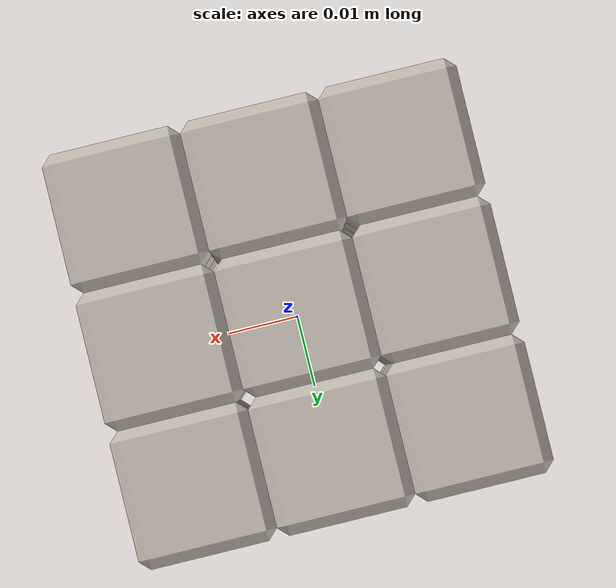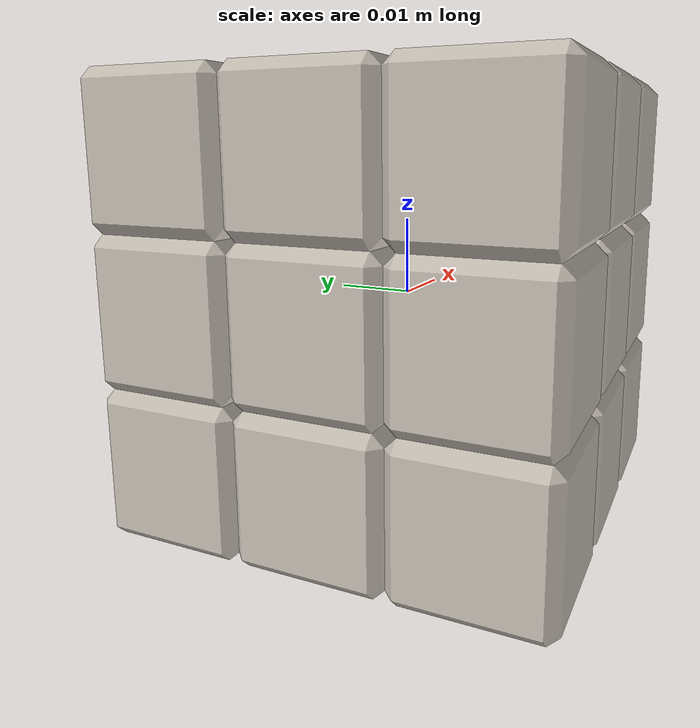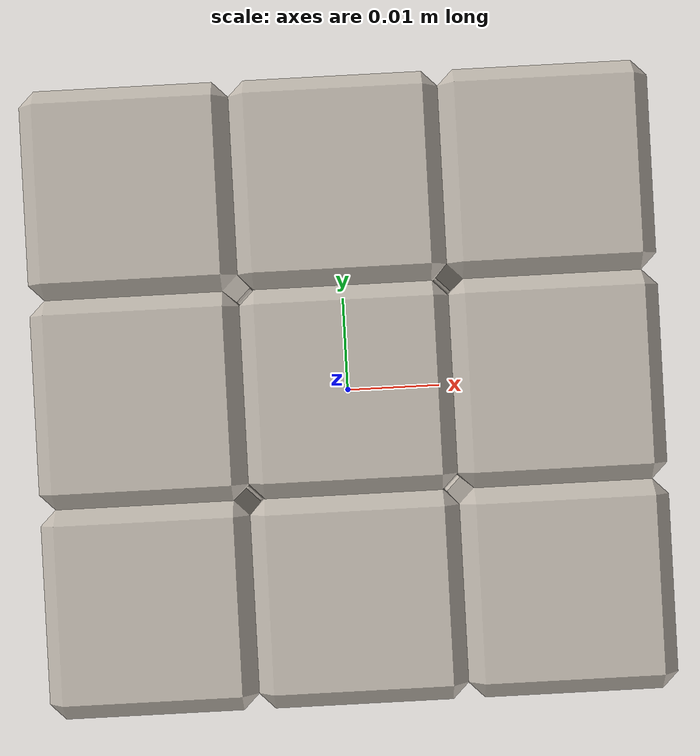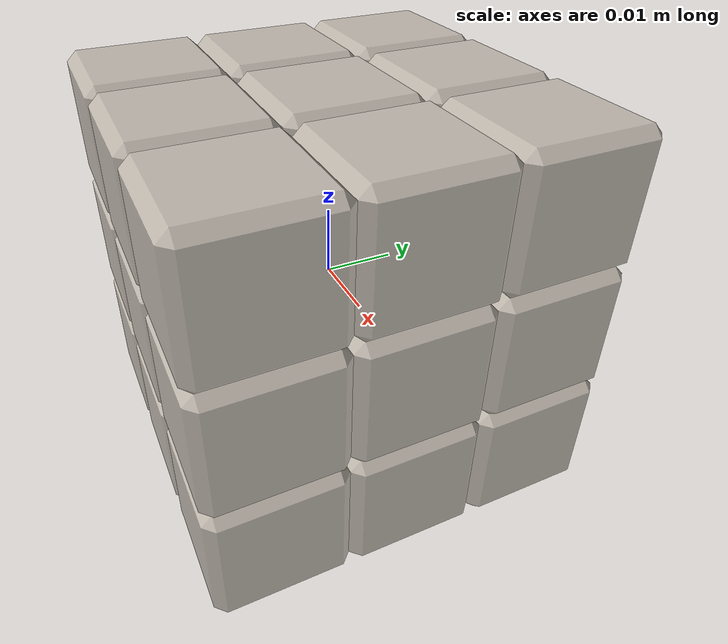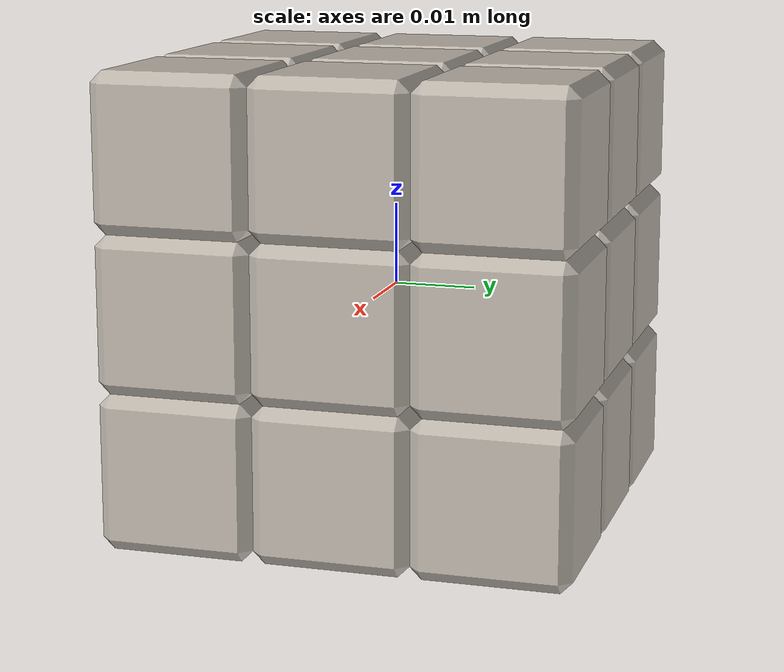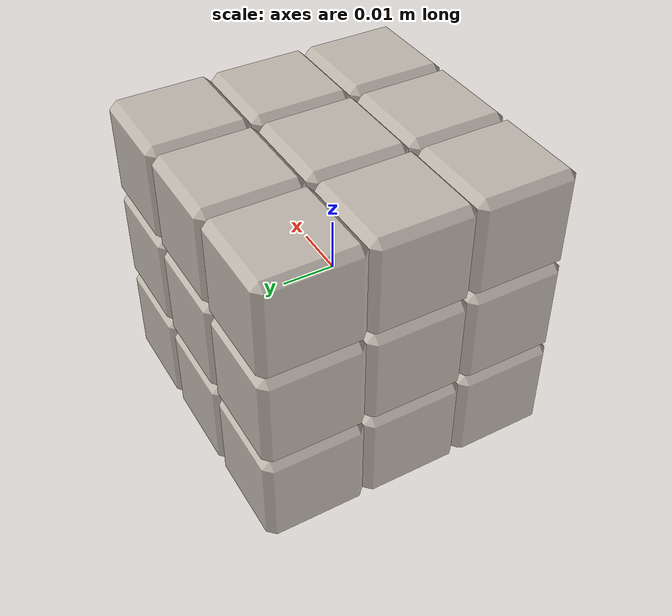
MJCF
<mujoco model="Cube 3x3x3">
  <compiler angle="radian" texturedir="assets/"/>

  <option timestep="0.01" integrator="implicitfast"/>

  <size memory="600K"/>

  <visual>
    <global azimuth="180" elevation="-20"/>
    <headlight ambient="0.3 0.3 0.3" diffuse="0.6 0.6 0.6" specular="0 0 0"/>
  </visual>

  <statistic meansize="0.0087" extent="0.1"/>

  <default>
    <general ctrlrange="-0.05 0.05"/>
    <default class="cubelet">
      <joint type="ball" armature="0.0001" damping="0.0005 0.0005 0.0005" frictionloss="0.001"/>
      <geom type="mesh" condim="1" material="sticker"/>
    </default>
    <default class="core">
      <geom size="0.01 0 0" contype="0" conaffinity="0" group="4"/>
    </default>
  </default>

  <asset>
    <texture type="skybox" colorspace="auto" builtin="gradient" width="512" height="3072"/>
    <texture type="2d" colorspace="linear" name="sticker" file="sticker.png"/>
    <material name="sticker" texture="sticker"/>
    <mesh name="pX" vertex="0.0095 0.008075 0.008075 0.008075 0.0095 0.008075 0.008075 0.008075 0.0095 0.008075 -0.0095 -0.008075 0.008075 -0.008075 -0.0095 0.0095 -0.008075 -0.008075 -0.0095 -0.008075 -0.008075 -0.008075 -0.008075 -0.0095 -0.008075 -0.0095 -0.008075 0.008075 0.0095 -0.008075 0.0095 0.008075 -0.008075 0.008075 0.008075 -0.0095 -0.0095 -0.008075 0.008075 -0.008075 -0.0095 0.008075 -0.008075 -0.008075 0.0095 0.008075 -0.008075 0.0095 0.008075 -0.0095 0.008075 0.0095 -0.008075 0.008075 -0.0095 0.008075 -0.008075 -0.008075 0.0095 -0.008075 -0.008075 0.008075 -0.0095 -0.008075 0.008075 0.0095 -0.008075 0.0095 0.008075 -0.0095 0.008075 0.008075 0.008075 0.0095 -0.008075 0.008075 0.0095 0.008075 0.0095 0.008075 -0.008075 0.0095 0.008075 -0.008075 0.008075 0.0095 0.008075 0.0095 0.008075 0.008075 0.0095 -0.008075 -0.008075 0.0095 0.008075 -0.008075 0.0095 0.008075 0.008075 0.0095 0.008075 0.008075 0.0095 -0.008075 0.008075 0.0095 -0.008075 -0.008075 0.008075 -0.0095 0.008075 0.0095 -0.008075 -0.008075 0.0095 -0.008075 0.008075 0.008075 -0.0095 -0.008075 0.0095 -0.008075 -0.008075 0.008075 -0.0095 0.008075 0.008075 -0.0095 -0.008075 0.008075 -0.0095 0.008075 -0.008075 -0.0095 -0.008075 -0.008075 -0.0095 -0.008075 0.008075 -0.0095 0.008075 -0.008075 -0.0095 0.008075 -0.008075 -0.0095 -0.008075 -0.008075 -0.008075 -0.0095 0.008075 -0.008075 -0.0095 -0.008075 -0.0095 -0.008075 0.008075 -0.008075 -0.0095 0.008075 -0.0095 -0.008075 0.0095 0.008075 -0.008075 0.0095 -0.008075 -0.008075 0.008075 0.008075 -0.0095 0.008075 0.008075 -0.0095 0.0095 -0.008075 -0.008075 0.008075 -0.008075 -0.0095 -0.008075 0.0095 0.008075 0.008075 0.0095 0.008075 0.008075 0.0095 -0.008075 0.008075 0.0095 -0.008075 -0.008075 0.0095 -0.008075 -0.008075 0.0095 0.008075 -0.008075 0.0095 0.008075 -0.008075 0.0095 -0.008075 -0.0095 0.008075 -0.008075 -0.0095 0.008075 -0.008075 -0.0095 0.008075 0.008075 -0.008075 0.0095 0.008075 -0.0095 -0.008075 0.008075 -0.008075 -0.0095 -0.008075 -0.008075 -0.0095 0.008075 -0.0095 -0.008075 -0.008075 -0.008075 -0.0095 -0.008075 -0.0095 -0.008075 0.008075 -0.0095 -0.008075 0.008075 -0.0095 0.008075 0.008075 -0.0095 0.008075 -0.008075 -0.0095 0.008075 -0.008075 -0.0095 -0.008075 -0.008075 -0.0095 -0.008075 0.008075 0.008075 -0.008075 0.0095 0.0095 -0.008075 0.008075 0.0095 0.008075 0.008075 0.0095 0.008075 0.008075 0.008075 0.008075 0.0095 0.008075 -0.008075 0.0095 -0.008075 -0.0095 0.008075 0.008075 -0.0095 0.008075 0.008075 -0.008075 0.0095 -0.008075 -0.008075 0.0095 -0.008075 -0.0095 0.008075 0.008075 -0.008075 0.0095 -0.008075 0.008075 -0.0095 -0.0095 -0.008075 -0.008075 -0.0095 0.008075 -0.008075 -0.008075 0.008075 -0.0095 -0.008075 -0.008075 -0.0095 -0.0095 -0.008075 -0.008075 0.008075 -0.008075 -0.0095 -0.008075 -0.008075 -0.0095 -0.008075 0.008075 -0.0095 -0.008075 0.008075 -0.0095 0.008075 0.008075 -0.0095 0.008075 -0.008075 -0.0095 -0.008075 0.008075 -0.0095 -0.008075 0.0095 -0.008075 0.008075 0.0095 -0.008075 0.008075 0.0095 -0.008075 0.008075 0.008075 -0.0095 -0.008075 0.008075 -0.0095 -0.0095 0.008075 0.008075 -0.0095 -0.008075 0.008075 -0.008075 0.008075 0.0095 -0.008075 0.008075 0.0095 -0.0095 -0.008075 0.008075 -0.008075 -0.008075 0.0095 -0.008075 -0.008075 0.0095 0.008075 -0.008075 0.0095 -0.008075 0.008075 0.0095 -0.008075 0.008075 0.0095 0.008075 -0.008075 0.0095 0.008075 0.008075 0.0095 0.008075 0.0095 0.008075 -0.008075 0.0095 0.008075 -0.008075 0.008075 0.0095 -0.008075 0.008075 0.0095 0.008075 0.008075 0.0095 0.008075 0.0095 0.008075" texcoord="0.0714286 0.5 0.0714286 0.5 0.0714286 0.5 0.0714286 0.5 0.0714286 0.5 0.0714286 0.5 0.0714286 0.5 0.0714286 0.5 0.0714286 0.5 0.0714286 0.5 0.0714286 0.5 0.0714286 0.5 0.0714286 0.5 0.0714286 0.5 0.0714286 0.5 0.0714286 0.5 0.0714286 0.5 0.0714286 0.5 0.0714286 0.5 0.0714286 0.5 0.0714286 0.5 0.0714286 0.5 0.0714286 0.5 0.0714286 0.5 0.0714286 0.5 0.0714286 0.5 0.0714286 0.5 0.0714286 0.5 0.0714286 0.5 0.0714286 0.5 0.43 0.01 0.57 0.01 0.57 0.99 0.57 0.99 0.43 0.99 0.43 0.01 0.0714286 0.5 0.0714286 0.5 0.0714286 0.5 0.0714286 0.5 0.0714286 0.5 0.0714286 0.5 0.0714286 0.5 0.0714286 0.5 0.0714286 0.5 0.0714286 0.5 0.0714286 0.5 0.0714286 0.5 0.0714286 0.5 0.0714286 0.5 0.0714286 0.5 0.0714286 0.5 0.0714286 0.5 0.0714286 0.5 0.0714286 0.5 0.0714286 0.5 0.0714286 0.5 0.0714286 0.5 0.0714286 0.5 0.0714286 0.5 0.0714286 0.5 0.0714286 0.5 0.0714286 0.5 0.0714286 0.5 0.0714286 0.5 0.0714286 0.5 0.0714286 0.5 0.0714286 0.5 0.0714286 0.5 0.0714286 0.5 0.0714286 0.5 0.0714286 0.5 0.0714286 0.5 0.0714286 0.5 0.0714286 0.5 0.0714286 0.5 0.0714286 0.5 0.0714286 0.5 0.0714286 0.5 0.0714286 0.5 0.0714286 0.5 0.0714286 0.5 0.0714286 0.5 0.0714286 0.5 0.0714286 0.5 0.0714286 0.5 0.0714286 0.5 0.0714286 0.5 0.0714286 0.5 0.0714286 0.5 0.0714286 0.5 0.0714286 0.5 0.0714286 0.5 0.0714286 0.5 0.0714286 0.5 0.0714286 0.5 0.0714286 0.5 0.0714286 0.5 0.0714286 0.5 0.0714286 0.5 0.0714286 0.5 0.0714286 0.5 0.0714286 0.5 0.0714286 0.5 0.0714286 0.5 0.0714286 0.5 0.0714286 0.5 0.0714286 0.5 0.0714286 0.5 0.0714286 0.5 0.0714286 0.5 0.0714286 0.5 0.0714286 0.5 0.0714286 0.5 0.0714286 0.5 0.0714286 0.5 0.0714286 0.5 0.0714286 0.5 0.0714286 0.5 0.0714286 0.5 0.0714286 0.5 0.0714286 0.5 0.0714286 0.5 0.0714286 0.5 0.0714286 0.5 0.0714286 0.5 0.0714286 0.5 0.0714286 0.5 0.0714286 0.5 0.0714286 0.5 0.0714286 0.5 0.0714286 0.5" face="0 1 2 3 4 5 6 7 8 9 10 11 12 13 14 15 16 17 18 19 20 21 22 23 24 25 26 27 28 29 30 31 32 33 34 35 36 37 38 39 40 41 42 43 44 45 46 47 48 49 50 51 52 53 54 55 56 57 58 59 60 61 62 63 64 65 66 67 68 69 70 71 72 73 74 75 76 77 78 79 80 81 82 83 84 85 86 87 88 89 90 91 92 93 94 95 96 97 98 99 100 101 102 103 104 105 106 107 108 109 110 111 112 113 114 115 116 117 118 119 120 121 122 123 124 125 126 127 128 129 130 131"/>
    <mesh name="nX" vertex="0.0095 0.008075 0.008075 0.008075 0.0095 0.008075 0.008075 0.008075 0.0095 0.008075 -0.0095 -0.008075 0.008075 -0.008075 -0.0095 0.0095 -0.008075 -0.008075 -0.0095 -0.008075 -0.008075 -0.008075 -0.008075 -0.0095 -0.008075 -0.0095 -0.008075 0.008075 0.0095 -0.008075 0.0095 0.008075 -0.008075 0.008075 0.008075 -0.0095 -0.0095 -0.008075 0.008075 -0.008075 -0.0095 0.008075 -0.008075 -0.008075 0.0095 0.008075 -0.008075 0.0095 0.008075 -0.0095 0.008075 0.0095 -0.008075 0.008075 -0.0095 0.008075 -0.008075 -0.008075 0.0095 -0.008075 -0.008075 0.008075 -0.0095 -0.008075 0.008075 0.0095 -0.008075 0.0095 0.008075 -0.0095 0.008075 0.008075 0.008075 0.0095 -0.008075 0.008075 0.0095 0.008075 0.0095 0.008075 -0.008075 0.0095 0.008075 -0.008075 0.008075 0.0095 0.008075 0.0095 0.008075 0.008075 0.0095 -0.008075 -0.008075 0.0095 0.008075 -0.008075 0.0095 0.008075 0.008075 0.0095 0.008075 0.008075 0.0095 -0.008075 0.008075 0.0095 -0.008075 -0.008075 0.008075 -0.0095 0.008075 0.0095 -0.008075 -0.008075 0.0095 -0.008075 0.008075 0.008075 -0.0095 -0.008075 0.0095 -0.008075 -0.008075 0.008075 -0.0095 0.008075 0.008075 -0.0095 -0.008075 0.008075 -0.0095 0.008075 -0.008075 -0.0095 -0.008075 -0.008075 -0.0095 -0.008075 0.008075 -0.0095 0.008075 -0.008075 -0.0095 0.008075 -0.008075 -0.0095 -0.008075 -0.008075 -0.008075 -0.0095 0.008075 -0.008075 -0.0095 -0.008075 -0.0095 -0.008075 0.008075 -0.008075 -0.0095 0.008075 -0.0095 -0.008075 0.0095 0.008075 -0.008075 0.0095 -0.008075 -0.008075 0.008075 0.008075 -0.0095 0.008075 0.008075 -0.0095 0.0095 -0.008075 -0.008075 0.008075 -0.008075 -0.0095 -0.008075 0.0095 0.008075 0.008075 0.0095 0.008075 0.008075 0.0095 -0.008075 0.008075 0.0095 -0.008075 -0.008075 0.0095 -0.008075 -0.008075 0.0095 0.008075 -0.008075 0.0095 0.008075 -0.008075 0.0095 -0.008075 -0.0095 0.008075 -0.008075 -0.0095 0.008075 -0.008075 -0.0095 0.008075 0.008075 -0.008075 0.0095 0.008075 -0.0095 -0.008075 0.008075 -0.008075 -0.0095 -0.008075 -0.008075 -0.0095 0.008075 -0.0095 -0.008075 -0.008075 -0.008075 -0.0095 -0.008075 -0.0095 -0.008075 0.008075 -0.0095 -0.008075 0.008075 -0.0095 0.008075 0.008075 -0.0095 0.008075 -0.008075 -0.0095 0.008075 -0.008075 -0.0095 -0.008075 -0.008075 -0.0095 -0.008075 0.008075 0.008075 -0.008075 0.0095 0.0095 -0.008075 0.008075 0.0095 0.008075 0.008075 0.0095 0.008075 0.008075 0.008075 0.008075 0.0095 0.008075 -0.008075 0.0095 -0.008075 -0.0095 0.008075 0.008075 -0.0095 0.008075 0.008075 -0.008075 0.0095 -0.008075 -0.008075 0.0095 -0.008075 -0.0095 0.008075 0.008075 -0.008075 0.0095 -0.008075 0.008075 -0.0095 -0.0095 -0.008075 -0.008075 -0.0095 0.008075 -0.008075 -0.008075 0.008075 -0.0095 -0.008075 -0.008075 -0.0095 -0.0095 -0.008075 -0.008075 0.008075 -0.008075 -0.0095 -0.008075 -0.008075 -0.0095 -0.008075 0.008075 -0.0095 -0.008075 0.008075 -0.0095 0.008075 0.008075 -0.0095 0.008075 -0.008075 -0.0095 -0.008075 0.008075 -0.0095 -0.008075 0.0095 -0.008075 0.008075 0.0095 -0.008075 0.008075 0.0095 -0.008075 0.008075 0.008075 -0.0095 -0.008075 0.008075 -0.0095 -0.0095 0.008075 0.008075 -0.0095 -0.008075 0.008075 -0.008075 0.008075 0.0095 -0.008075 0.008075 0.0095 -0.0095 -0.008075 0.008075 -0.008075 -0.008075 0.0095 -0.008075 -0.008075 0.0095 0.008075 -0.008075 0.0095 -0.008075 0.008075 0.0095 -0.008075 0.008075 0.0095 0.008075 -0.008075 0.0095 0.008075 0.008075 0.0095 0.008075 0.0095 0.008075 -0.008075 0.0095 0.008075 -0.008075 0.008075 0.0095 -0.008075 0.008075 0.0095 0.008075 0.008075 0.0095 0.008075 0.0095 0.008075" texcoord="0.0714286 0.5 0.0714286 0.5 0.0714286 0.5 0.0714286 0.5 0.0714286 0.5 0.0714286 0.5 0.0714286 0.5 0.0714286 0.5 0.0714286 0.5 0.0714286 0.5 0.0714286 0.5 0.0714286 0.5 0.0714286 0.5 0.0714286 0.5 0.0714286 0.5 0.0714286 0.5 0.0714286 0.5 0.0714286 0.5 0.0714286 0.5 0.0714286 0.5 0.0714286 0.5 0.0714286 0.5 0.0714286 0.5 0.0714286 0.5 0.0714286 0.5 0.0714286 0.5 0.0714286 0.5 0.0714286 0.5 0.0714286 0.5 0.0714286 0.5 0.0714286 0.5 0.0714286 0.5 0.0714286 0.5 0.0714286 0.5 0.0714286 0.5 0.0714286 0.5 0.0714286 0.5 0.0714286 0.5 0.0714286 0.5 0.0714286 0.5 0.0714286 0.5 0.0714286 0.5 0.0714286 0.5 0.0714286 0.5 0.0714286 0.5 0.0714286 0.5 0.0714286 0.5 0.0714286 0.5 0.0714286 0.5 0.0714286 0.5 0.0714286 0.5 0.0714286 0.5 0.0714286 0.5 0.0714286 0.5 0.0714286 0.5 0.0714286 0.5 0.0714286 0.5 0.0714286 0.5 0.0714286 0.5 0.0714286 0.5 0.0714286 0.5 0.0714286 0.5 0.0714286 0.5 0.0714286 0.5 0.0714286 0.5 0.0714286 0.5 0.0714286 0.5 0.0714286 0.5 0.0714286 0.5 0.0714286 0.5 0.0714286 0.5 0.0714286 0.5 0.0714286 0.5 0.0714286 0.5 0.0714286 0.5 0.0714286 0.5 0.0714286 0.5 0.0714286 0.5 0.572857 0.99 0.712857 0.99 0.712857 0.01 0.712857 0.01 0.572857 0.01 0.572857 0.99 0.0714286 0.5 0.0714286 0.5 0.0714286 0.5 0.0714286 0.5 0.0714286 0.5 0.0714286 0.5 0.0714286 0.5 0.0714286 0.5 0.0714286 0.5 0.0714286 0.5 0.0714286 0.5 0.0714286 0.5 0.0714286 0.5 0.0714286 0.5 0.0714286 0.5 0.0714286 0.5 0.0714286 0.5 0.0714286 0.5 0.0714286 0.5 0.0714286 0.5 0.0714286 0.5 0.0714286 0.5 0.0714286 0.5 0.0714286 0.5 0.0714286 0.5 0.0714286 0.5 0.0714286 0.5 0.0714286 0.5 0.0714286 0.5 0.0714286 0.5 0.0714286 0.5 0.0714286 0.5 0.0714286 0.5 0.0714286 0.5 0.0714286 0.5 0.0714286 0.5 0.0714286 0.5 0.0714286 0.5 0.0714286 0.5 0.0714286 0.5 0.0714286 0.5 0.0714286 0.5 0.0714286 0.5 0.0714286 0.5 0.0714286 0.5 0.0714286 0.5 0.0714286 0.5 0.0714286 0.5" face="0 1 2 3 4 5 6 7 8 9 10 11 12 13 14 15 16 17 18 19 20 21 22 23 24 25 26 27 28 29 30 31 32 33 34 35 36 37 38 39 40 41 42 43 44 45 46 47 48 49 50 51 52 53 54 55 56 57 58 59 60 61 62 63 64 65 66 67 68 69 70 71 72 73 74 75 76 77 78 79 80 81 82 83 84 85 86 87 88 89 90 91 92 93 94 95 96 97 98 99 100 101 102 103 104 105 106 107 108 109 110 111 112 113 114 115 116 117 118 119 120 121 122 123 124 125 126 127 128 129 130 131"/>
    <mesh name="pY" vertex="0.0095 0.008075 0.008075 0.008075 0.0095 0.008075 0.008075 0.008075 0.0095 0.008075 -0.0095 -0.008075 0.008075 -0.008075 -0.0095 0.0095 -0.008075 -0.008075 -0.0095 -0.008075 -0.008075 -0.008075 -0.008075 -0.0095 -0.008075 -0.0095 -0.008075 0.008075 0.0095 -0.008075 0.0095 0.008075 -0.008075 0.008075 0.008075 -0.0095 -0.0095 -0.008075 0.008075 -0.008075 -0.0095 0.008075 -0.008075 -0.008075 0.0095 0.008075 -0.008075 0.0095 0.008075 -0.0095 0.008075 0.0095 -0.008075 0.008075 -0.0095 0.008075 -0.008075 -0.008075 0.0095 -0.008075 -0.008075 0.008075 -0.0095 -0.008075 0.008075 0.0095 -0.008075 0.0095 0.008075 -0.0095 0.008075 0.008075 0.008075 0.0095 -0.008075 0.008075 0.0095 0.008075 0.0095 0.008075 -0.008075 0.0095 0.008075 -0.008075 0.008075 0.0095 0.008075 0.0095 0.008075 0.008075 0.0095 -0.008075 -0.008075 0.0095 0.008075 -0.008075 0.0095 0.008075 0.008075 0.0095 0.008075 0.008075 0.0095 -0.008075 0.008075 0.0095 -0.008075 -0.008075 0.008075 -0.0095 0.008075 0.0095 -0.008075 -0.008075 0.0095 -0.008075 0.008075 0.008075 -0.0095 -0.008075 0.0095 -0.008075 -0.008075 0.008075 -0.0095 0.008075 0.008075 -0.0095 -0.008075 0.008075 -0.0095 0.008075 -0.008075 -0.0095 -0.008075 -0.008075 -0.0095 -0.008075 0.008075 -0.0095 0.008075 -0.008075 -0.0095 0.008075 -0.008075 -0.0095 -0.008075 -0.008075 -0.008075 -0.0095 0.008075 -0.008075 -0.0095 -0.008075 -0.0095 -0.008075 0.008075 -0.008075 -0.0095 0.008075 -0.0095 -0.008075 0.0095 0.008075 -0.008075 0.0095 -0.008075 -0.008075 0.008075 0.008075 -0.0095 0.008075 0.008075 -0.0095 0.0095 -0.008075 -0.008075 0.008075 -0.008075 -0.0095 -0.008075 0.0095 0.008075 0.008075 0.0095 0.008075 0.008075 0.0095 -0.008075 0.008075 0.0095 -0.008075 -0.008075 0.0095 -0.008075 -0.008075 0.0095 0.008075 -0.008075 0.0095 0.008075 -0.008075 0.0095 -0.008075 -0.0095 0.008075 -0.008075 -0.0095 0.008075 -0.008075 -0.0095 0.008075 0.008075 -0.008075 0.0095 0.008075 -0.0095 -0.008075 0.008075 -0.008075 -0.0095 -0.008075 -0.008075 -0.0095 0.008075 -0.0095 -0.008075 -0.008075 -0.008075 -0.0095 -0.008075 -0.0095 -0.008075 0.008075 -0.0095 -0.008075 0.008075 -0.0095 0.008075 0.008075 -0.0095 0.008075 -0.008075 -0.0095 0.008075 -0.008075 -0.0095 -0.008075 -0.008075 -0.0095 -0.008075 0.008075 0.008075 -0.008075 0.0095 0.0095 -0.008075 0.008075 0.0095 0.008075 0.008075 0.0095 0.008075 0.008075 0.008075 0.008075 0.0095 0.008075 -0.008075 0.0095 -0.008075 -0.0095 0.008075 0.008075 -0.0095 0.008075 0.008075 -0.008075 0.0095 -0.008075 -0.008075 0.0095 -0.008075 -0.0095 0.008075 0.008075 -0.008075 0.0095 -0.008075 0.008075 -0.0095 -0.0095 -0.008075 -0.008075 -0.0095 0.008075 -0.008075 -0.008075 0.008075 -0.0095 -0.008075 -0.008075 -0.0095 -0.0095 -0.008075 -0.008075 0.008075 -0.008075 -0.0095 -0.008075 -0.008075 -0.0095 -0.008075 0.008075 -0.0095 -0.008075 0.008075 -0.0095 0.008075 0.008075 -0.0095 0.008075 -0.008075 -0.0095 -0.008075 0.008075 -0.0095 -0.008075 0.0095 -0.008075 0.008075 0.0095 -0.008075 0.008075 0.0095 -0.008075 0.008075 0.008075 -0.0095 -0.008075 0.008075 -0.0095 -0.0095 0.008075 0.008075 -0.0095 -0.008075 0.008075 -0.008075 0.008075 0.0095 -0.008075 0.008075 0.0095 -0.0095 -0.008075 0.008075 -0.008075 -0.008075 0.0095 -0.008075 -0.008075 0.0095 0.008075 -0.008075 0.0095 -0.008075 0.008075 0.0095 -0.008075 0.008075 0.0095 0.008075 -0.008075 0.0095 0.008075 0.008075 0.0095 0.008075 0.0095 0.008075 -0.008075 0.0095 0.008075 -0.008075 0.008075 0.0095 -0.008075 0.008075 0.0095 0.008075 0.008075 0.0095 0.008075 0.0095 0.008075" texcoord="0.0714286 0.5 0.0714286 0.5 0.0714286 0.5 0.0714286 0.5 0.0714286 0.5 0.0714286 0.5 0.0714286 0.5 0.0714286 0.5 0.0714286 0.5 0.0714286 0.5 0.0714286 0.5 0.0714286 0.5 0.0714286 0.5 0.0714286 0.5 0.0714286 0.5 0.0714286 0.5 0.0714286 0.5 0.0714286 0.5 0.0714286 0.5 0.0714286 0.5 0.0714286 0.5 0.0714286 0.5 0.0714286 0.5 0.0714286 0.5 0.0714286 0.5 0.0714286 0.5 0.0714286 0.5 0.0714286 0.5 0.0714286 0.5 0.0714286 0.5 0.0714286 0.5 0.0714286 0.5 0.0714286 0.5 0.0714286 0.5 0.0714286 0.5 0.0714286 0.5 0.0714286 0.5 0.0714286 0.5 0.0714286 0.5 0.0714286 0.5 0.0714286 0.5 0.0714286 0.5 0.0714286 0.5 0.0714286 0.5 0.0714286 0.5 0.0714286 0.5 0.0714286 0.5 0.0714286 0.5 0.0714286 0.5 0.0714286 0.5 0.0714286 0.5 0.0714286 0.5 0.0714286 0.5 0.0714286 0.5 0.0714286 0.5 0.0714286 0.5 0.0714286 0.5 0.0714286 0.5 0.0714286 0.5 0.0714286 0.5 0.715714 0.99 0.855714 0.99 0.855714 0.01 0.855714 0.01 0.715714 0.01 0.715714 0.99 0.0714286 0.5 0.0714286 0.5 0.0714286 0.5 0.0714286 0.5 0.0714286 0.5 0.0714286 0.5 0.0714286 0.5 0.0714286 0.5 0.0714286 0.5 0.0714286 0.5 0.0714286 0.5 0.0714286 0.5 0.0714286 0.5 0.0714286 0.5 0.0714286 0.5 0.0714286 0.5 0.0714286 0.5 0.0714286 0.5 0.0714286 0.5 0.0714286 0.5 0.0714286 0.5 0.0714286 0.5 0.0714286 0.5 0.0714286 0.5 0.0714286 0.5 0.0714286 0.5 0.0714286 0.5 0.0714286 0.5 0.0714286 0.5 0.0714286 0.5 0.0714286 0.5 0.0714286 0.5 0.0714286 0.5 0.0714286 0.5 0.0714286 0.5 0.0714286 0.5 0.0714286 0.5 0.0714286 0.5 0.0714286 0.5 0.0714286 0.5 0.0714286 0.5 0.0714286 0.5 0.0714286 0.5 0.0714286 0.5 0.0714286 0.5 0.0714286 0.5 0.0714286 0.5 0.0714286 0.5 0.0714286 0.5 0.0714286 0.5 0.0714286 0.5 0.0714286 0.5 0.0714286 0.5 0.0714286 0.5 0.0714286 0.5 0.0714286 0.5 0.0714286 0.5 0.0714286 0.5 0.0714286 0.5 0.0714286 0.5 0.0714286 0.5 0.0714286 0.5 0.0714286 0.5 0.0714286 0.5 0.0714286 0.5 0.0714286 0.5" face="0 1 2 3 4 5 6 7 8 9 10 11 12 13 14 15 16 17 18 19 20 21 22 23 24 25 26 27 28 29 30 31 32 33 34 35 36 37 38 39 40 41 42 43 44 45 46 47 48 49 50 51 52 53 54 55 56 57 58 59 60 61 62 63 64 65 66 67 68 69 70 71 72 73 74 75 76 77 78 79 80 81 82 83 84 85 86 87 88 89 90 91 92 93 94 95 96 97 98 99 100 101 102 103 104 105 106 107 108 109 110 111 112 113 114 115 116 117 118 119 120 121 122 123 124 125 126 127 128 129 130 131"/>
    <mesh name="nY" vertex="0.0095 0.008075 0.008075 0.008075 0.0095 0.008075 0.008075 0.008075 0.0095 0.008075 -0.0095 -0.008075 0.008075 -0.008075 -0.0095 0.0095 -0.008075 -0.008075 -0.0095 -0.008075 -0.008075 -0.008075 -0.008075 -0.0095 -0.008075 -0.0095 -0.008075 0.008075 0.0095 -0.008075 0.0095 0.008075 -0.008075 0.008075 0.008075 -0.0095 -0.0095 -0.008075 0.008075 -0.008075 -0.0095 0.008075 -0.008075 -0.008075 0.0095 0.008075 -0.008075 0.0095 0.008075 -0.0095 0.008075 0.0095 -0.008075 0.008075 -0.0095 0.008075 -0.008075 -0.008075 0.0095 -0.008075 -0.008075 0.008075 -0.0095 -0.008075 0.008075 0.0095 -0.008075 0.0095 0.008075 -0.0095 0.008075 0.008075 0.008075 0.0095 -0.008075 0.008075 0.0095 0.008075 0.0095 0.008075 -0.008075 0.0095 0.008075 -0.008075 0.008075 0.0095 0.008075 0.0095 0.008075 0.008075 0.0095 -0.008075 -0.008075 0.0095 0.008075 -0.008075 0.0095 0.008075 0.008075 0.0095 0.008075 0.008075 0.0095 -0.008075 0.008075 0.0095 -0.008075 -0.008075 0.008075 -0.0095 0.008075 0.0095 -0.008075 -0.008075 0.0095 -0.008075 0.008075 0.008075 -0.0095 -0.008075 0.0095 -0.008075 -0.008075 0.008075 -0.0095 0.008075 0.008075 -0.0095 -0.008075 0.008075 -0.0095 0.008075 -0.008075 -0.0095 -0.008075 -0.008075 -0.0095 -0.008075 0.008075 -0.0095 0.008075 -0.008075 -0.0095 0.008075 -0.008075 -0.0095 -0.008075 -0.008075 -0.008075 -0.0095 0.008075 -0.008075 -0.0095 -0.008075 -0.0095 -0.008075 0.008075 -0.008075 -0.0095 0.008075 -0.0095 -0.008075 0.0095 0.008075 -0.008075 0.0095 -0.008075 -0.008075 0.008075 0.008075 -0.0095 0.008075 0.008075 -0.0095 0.0095 -0.008075 -0.008075 0.008075 -0.008075 -0.0095 -0.008075 0.0095 0.008075 0.008075 0.0095 0.008075 0.008075 0.0095 -0.008075 0.008075 0.0095 -0.008075 -0.008075 0.0095 -0.008075 -0.008075 0.0095 0.008075 -0.008075 0.0095 0.008075 -0.008075 0.0095 -0.008075 -0.0095 0.008075 -0.008075 -0.0095 0.008075 -0.008075 -0.0095 0.008075 0.008075 -0.008075 0.0095 0.008075 -0.0095 -0.008075 0.008075 -0.008075 -0.0095 -0.008075 -0.008075 -0.0095 0.008075 -0.0095 -0.008075 -0.008075 -0.008075 -0.0095 -0.008075 -0.0095 -0.008075 0.008075 -0.0095 -0.008075 0.008075 -0.0095 0.008075 0.008075 -0.0095 0.008075 -0.008075 -0.0095 0.008075 -0.008075 -0.0095 -0.008075 -0.008075 -0.0095 -0.008075 0.008075 0.008075 -0.008075 0.0095 0.0095 -0.008075 0.008075 0.0095 0.008075 0.008075 0.0095 0.008075 0.008075 0.008075 0.008075 0.0095 0.008075 -0.008075 0.0095 -0.008075 -0.0095 0.008075 0.008075 -0.0095 0.008075 0.008075 -0.008075 0.0095 -0.008075 -0.008075 0.0095 -0.008075 -0.0095 0.008075 0.008075 -0.008075 0.0095 -0.008075 0.008075 -0.0095 -0.0095 -0.008075 -0.008075 -0.0095 0.008075 -0.008075 -0.008075 0.008075 -0.0095 -0.008075 -0.008075 -0.0095 -0.0095 -0.008075 -0.008075 0.008075 -0.008075 -0.0095 -0.008075 -0.008075 -0.0095 -0.008075 0.008075 -0.0095 -0.008075 0.008075 -0.0095 0.008075 0.008075 -0.0095 0.008075 -0.008075 -0.0095 -0.008075 0.008075 -0.0095 -0.008075 0.0095 -0.008075 0.008075 0.0095 -0.008075 0.008075 0.0095 -0.008075 0.008075 0.008075 -0.0095 -0.008075 0.008075 -0.0095 -0.0095 0.008075 0.008075 -0.0095 -0.008075 0.008075 -0.008075 0.008075 0.0095 -0.008075 0.008075 0.0095 -0.0095 -0.008075 0.008075 -0.008075 -0.008075 0.0095 -0.008075 -0.008075 0.0095 0.008075 -0.008075 0.0095 -0.008075 0.008075 0.0095 -0.008075 0.008075 0.0095 0.008075 -0.008075 0.0095 0.008075 0.008075 0.0095 0.008075 0.0095 0.008075 -0.008075 0.0095 0.008075 -0.008075 0.008075 0.0095 -0.008075 0.008075 0.0095 0.008075 0.008075 0.0095 0.008075 0.0095 0.008075" texcoord="0.0714286 0.5 0.0714286 0.5 0.0714286 0.5 0.0714286 0.5 0.0714286 0.5 0.0714286 0.5 0.0714286 0.5 0.0714286 0.5 0.0714286 0.5 0.0714286 0.5 0.0714286 0.5 0.0714286 0.5 0.0714286 0.5 0.0714286 0.5 0.0714286 0.5 0.0714286 0.5 0.0714286 0.5 0.0714286 0.5 0.0714286 0.5 0.0714286 0.5 0.0714286 0.5 0.0714286 0.5 0.0714286 0.5 0.0714286 0.5 0.0714286 0.5 0.0714286 0.5 0.0714286 0.5 0.0714286 0.5 0.0714286 0.5 0.0714286 0.5 0.0714286 0.5 0.0714286 0.5 0.0714286 0.5 0.0714286 0.5 0.0714286 0.5 0.0714286 0.5 0.0714286 0.5 0.0714286 0.5 0.0714286 0.5 0.0714286 0.5 0.0714286 0.5 0.0714286 0.5 0.998571 0.01 0.998571 0.99 0.858571 0.01 0.858571 0.01 0.998571 0.99 0.858571 0.99 0.0714286 0.5 0.0714286 0.5 0.0714286 0.5 0.0714286 0.5 0.0714286 0.5 0.0714286 0.5 0.0714286 0.5 0.0714286 0.5 0.0714286 0.5 0.0714286 0.5 0.0714286 0.5 0.0714286 0.5 0.0714286 0.5 0.0714286 0.5 0.0714286 0.5 0.0714286 0.5 0.0714286 0.5 0.0714286 0.5 0.0714286 0.5 0.0714286 0.5 0.0714286 0.5 0.0714286 0.5 0.0714286 0.5 0.0714286 0.5 0.0714286 0.5 0.0714286 0.5 0.0714286 0.5 0.0714286 0.5 0.0714286 0.5 0.0714286 0.5 0.0714286 0.5 0.0714286 0.5 0.0714286 0.5 0.0714286 0.5 0.0714286 0.5 0.0714286 0.5 0.0714286 0.5 0.0714286 0.5 0.0714286 0.5 0.0714286 0.5 0.0714286 0.5 0.0714286 0.5 0.0714286 0.5 0.0714286 0.5 0.0714286 0.5 0.0714286 0.5 0.0714286 0.5 0.0714286 0.5 0.0714286 0.5 0.0714286 0.5 0.0714286 0.5 0.0714286 0.5 0.0714286 0.5 0.0714286 0.5 0.0714286 0.5 0.0714286 0.5 0.0714286 0.5 0.0714286 0.5 0.0714286 0.5 0.0714286 0.5 0.0714286 0.5 0.0714286 0.5 0.0714286 0.5 0.0714286 0.5 0.0714286 0.5 0.0714286 0.5 0.0714286 0.5 0.0714286 0.5 0.0714286 0.5 0.0714286 0.5 0.0714286 0.5 0.0714286 0.5 0.0714286 0.5 0.0714286 0.5 0.0714286 0.5 0.0714286 0.5 0.0714286 0.5 0.0714286 0.5 0.0714286 0.5 0.0714286 0.5 0.0714286 0.5 0.0714286 0.5 0.0714286 0.5 0.0714286 0.5" face="0 1 2 3 4 5 6 7 8 9 10 11 12 13 14 15 16 17 18 19 20 21 22 23 24 25 26 27 28 29 30 31 32 33 34 35 36 37 38 39 40 41 42 43 44 45 46 47 48 49 50 51 52 53 54 55 56 57 58 59 60 61 62 63 64 65 66 67 68 69 70 71 72 73 74 75 76 77 78 79 80 81 82 83 84 85 86 87 88 89 90 91 92 93 94 95 96 97 98 99 100 101 102 103 104 105 106 107 108 109 110 111 112 113 114 115 116 117 118 119 120 121 122 123 124 125 126 127 128 129 130 131"/>
    <mesh name="pZ" vertex="0.0095 0.008075 0.008075 0.008075 0.0095 0.008075 0.008075 0.008075 0.0095 0.008075 -0.0095 -0.008075 0.008075 -0.008075 -0.0095 0.0095 -0.008075 -0.008075 -0.0095 -0.008075 -0.008075 -0.008075 -0.008075 -0.0095 -0.008075 -0.0095 -0.008075 0.008075 0.0095 -0.008075 0.0095 0.008075 -0.008075 0.008075 0.008075 -0.0095 -0.0095 -0.008075 0.008075 -0.008075 -0.0095 0.008075 -0.008075 -0.008075 0.0095 0.008075 -0.008075 0.0095 0.008075 -0.0095 0.008075 0.0095 -0.008075 0.008075 -0.0095 0.008075 -0.008075 -0.008075 0.0095 -0.008075 -0.008075 0.008075 -0.0095 -0.008075 0.008075 0.0095 -0.008075 0.0095 0.008075 -0.0095 0.008075 0.008075 0.008075 0.0095 -0.008075 0.008075 0.0095 0.008075 0.0095 0.008075 -0.008075 0.0095 0.008075 -0.008075 0.008075 0.0095 0.008075 0.0095 0.008075 0.008075 0.0095 -0.008075 -0.008075 0.0095 0.008075 -0.008075 0.0095 0.008075 0.008075 0.0095 0.008075 0.008075 0.0095 -0.008075 0.008075 0.0095 -0.008075 -0.008075 0.008075 -0.0095 0.008075 0.0095 -0.008075 -0.008075 0.0095 -0.008075 0.008075 0.008075 -0.0095 -0.008075 0.0095 -0.008075 -0.008075 0.008075 -0.0095 0.008075 0.008075 -0.0095 -0.008075 0.008075 -0.0095 0.008075 -0.008075 -0.0095 -0.008075 -0.008075 -0.0095 -0.008075 0.008075 -0.0095 0.008075 -0.008075 -0.0095 0.008075 -0.008075 -0.0095 -0.008075 -0.008075 -0.008075 -0.0095 0.008075 -0.008075 -0.0095 -0.008075 -0.0095 -0.008075 0.008075 -0.008075 -0.0095 0.008075 -0.0095 -0.008075 0.0095 0.008075 -0.008075 0.0095 -0.008075 -0.008075 0.008075 0.008075 -0.0095 0.008075 0.008075 -0.0095 0.0095 -0.008075 -0.008075 0.008075 -0.008075 -0.0095 -0.008075 0.0095 0.008075 0.008075 0.0095 0.008075 0.008075 0.0095 -0.008075 0.008075 0.0095 -0.008075 -0.008075 0.0095 -0.008075 -0.008075 0.0095 0.008075 -0.008075 0.0095 0.008075 -0.008075 0.0095 -0.008075 -0.0095 0.008075 -0.008075 -0.0095 0.008075 -0.008075 -0.0095 0.008075 0.008075 -0.008075 0.0095 0.008075 -0.0095 -0.008075 0.008075 -0.008075 -0.0095 -0.008075 -0.008075 -0.0095 0.008075 -0.0095 -0.008075 -0.008075 -0.008075 -0.0095 -0.008075 -0.0095 -0.008075 0.008075 -0.0095 -0.008075 0.008075 -0.0095 0.008075 0.008075 -0.0095 0.008075 -0.008075 -0.0095 0.008075 -0.008075 -0.0095 -0.008075 -0.008075 -0.0095 -0.008075 0.008075 0.008075 -0.008075 0.0095 0.0095 -0.008075 0.008075 0.0095 0.008075 0.008075 0.0095 0.008075 0.008075 0.008075 0.008075 0.0095 0.008075 -0.008075 0.0095 -0.008075 -0.0095 0.008075 0.008075 -0.0095 0.008075 0.008075 -0.008075 0.0095 -0.008075 -0.008075 0.0095 -0.008075 -0.0095 0.008075 0.008075 -0.008075 0.0095 -0.008075 0.008075 -0.0095 -0.0095 -0.008075 -0.008075 -0.0095 0.008075 -0.008075 -0.008075 0.008075 -0.0095 -0.008075 -0.008075 -0.0095 -0.0095 -0.008075 -0.008075 0.008075 -0.008075 -0.0095 -0.008075 -0.008075 -0.0095 -0.008075 0.008075 -0.0095 -0.008075 0.008075 -0.0095 0.008075 0.008075 -0.0095 0.008075 -0.008075 -0.0095 -0.008075 0.008075 -0.0095 -0.008075 0.0095 -0.008075 0.008075 0.0095 -0.008075 0.008075 0.0095 -0.008075 0.008075 0.008075 -0.0095 -0.008075 0.008075 -0.0095 -0.0095 0.008075 0.008075 -0.0095 -0.008075 0.008075 -0.008075 0.008075 0.0095 -0.008075 0.008075 0.0095 -0.0095 -0.008075 0.008075 -0.008075 -0.008075 0.0095 -0.008075 -0.008075 0.0095 0.008075 -0.008075 0.0095 -0.008075 0.008075 0.0095 -0.008075 0.008075 0.0095 0.008075 -0.008075 0.0095 0.008075 0.008075 0.0095 0.008075 0.0095 0.008075 -0.008075 0.0095 0.008075 -0.008075 0.008075 0.0095 -0.008075 0.008075 0.0095 0.008075 0.008075 0.0095 0.008075 0.0095 0.008075" texcoord="0.0714286 0.5 0.0714286 0.5 0.0714286 0.5 0.0714286 0.5 0.0714286 0.5 0.0714286 0.5 0.0714286 0.5 0.0714286 0.5 0.0714286 0.5 0.0714286 0.5 0.0714286 0.5 0.0714286 0.5 0.0714286 0.5 0.0714286 0.5 0.0714286 0.5 0.0714286 0.5 0.0714286 0.5 0.0714286 0.5 0.0714286 0.5 0.0714286 0.5 0.0714286 0.5 0.0714286 0.5 0.0714286 0.5 0.0714286 0.5 0.0714286 0.5 0.0714286 0.5 0.0714286 0.5 0.0714286 0.5 0.0714286 0.5 0.0714286 0.5 0.0714286 0.5 0.0714286 0.5 0.0714286 0.5 0.0714286 0.5 0.0714286 0.5 0.0714286 0.5 0.0714286 0.5 0.0714286 0.5 0.0714286 0.5 0.0714286 0.5 0.0714286 0.5 0.0714286 0.5 0.0714286 0.5 0.0714286 0.5 0.0714286 0.5 0.0714286 0.5 0.0714286 0.5 0.0714286 0.5 0.0714286 0.5 0.0714286 0.5 0.0714286 0.5 0.0714286 0.5 0.0714286 0.5 0.0714286 0.5 0.0714286 0.5 0.0714286 0.5 0.0714286 0.5 0.0714286 0.5 0.0714286 0.5 0.0714286 0.5 0.0714286 0.5 0.0714286 0.5 0.0714286 0.5 0.0714286 0.5 0.0714286 0.5 0.0714286 0.5 0.0714286 0.5 0.0714286 0.5 0.0714286 0.5 0.0714286 0.5 0.0714286 0.5 0.0714286 0.5 0.0714286 0.5 0.0714286 0.5 0.0714286 0.5 0.0714286 0.5 0.0714286 0.5 0.0714286 0.5 0.0714286 0.5 0.0714286 0.5 0.0714286 0.5 0.0714286 0.5 0.0714286 0.5 0.0714286 0.5 0.0714286 0.5 0.0714286 0.5 0.0714286 0.5 0.0714286 0.5 0.0714286 0.5 0.0714286 0.5 0.0714286 0.5 0.0714286 0.5 0.0714286 0.5 0.0714286 0.5 0.0714286 0.5 0.0714286 0.5 0.0714286 0.5 0.0714286 0.5 0.0714286 0.5 0.0714286 0.5 0.0714286 0.5 0.0714286 0.5 0.0714286 0.5 0.0714286 0.5 0.0714286 0.5 0.0714286 0.5 0.0714286 0.5 0.0714286 0.5 0.0714286 0.5 0.0714286 0.5 0.0714286 0.5 0.0714286 0.5 0.0714286 0.5 0.0714286 0.5 0.0714286 0.5 0.0714286 0.5 0.0714286 0.5 0.0714286 0.5 0.0714286 0.5 0.0714286 0.5 0.144286 0.01 0.284286 0.01 0.144286 0.99 0.144286 0.99 0.284286 0.01 0.284286 0.99 0.0714286 0.5 0.0714286 0.5 0.0714286 0.5 0.0714286 0.5 0.0714286 0.5 0.0714286 0.5" face="0 1 2 3 4 5 6 7 8 9 10 11 12 13 14 15 16 17 18 19 20 21 22 23 24 25 26 27 28 29 30 31 32 33 34 35 36 37 38 39 40 41 42 43 44 45 46 47 48 49 50 51 52 53 54 55 56 57 58 59 60 61 62 63 64 65 66 67 68 69 70 71 72 73 74 75 76 77 78 79 80 81 82 83 84 85 86 87 88 89 90 91 92 93 94 95 96 97 98 99 100 101 102 103 104 105 106 107 108 109 110 111 112 113 114 115 116 117 118 119 120 121 122 123 124 125 126 127 128 129 130 131"/>
    <mesh name="nZ" vertex="0.0095 0.008075 0.008075 0.008075 0.0095 0.008075 0.008075 0.008075 0.0095 0.008075 -0.0095 -0.008075 0.008075 -0.008075 -0.0095 0.0095 -0.008075 -0.008075 -0.0095 -0.008075 -0.008075 -0.008075 -0.008075 -0.0095 -0.008075 -0.0095 -0.008075 0.008075 0.0095 -0.008075 0.0095 0.008075 -0.008075 0.008075 0.008075 -0.0095 -0.0095 -0.008075 0.008075 -0.008075 -0.0095 0.008075 -0.008075 -0.008075 0.0095 0.008075 -0.008075 0.0095 0.008075 -0.0095 0.008075 0.0095 -0.008075 0.008075 -0.0095 0.008075 -0.008075 -0.008075 0.0095 -0.008075 -0.008075 0.008075 -0.0095 -0.008075 0.008075 0.0095 -0.008075 0.0095 0.008075 -0.0095 0.008075 0.008075 0.008075 0.0095 -0.008075 0.008075 0.0095 0.008075 0.0095 0.008075 -0.008075 0.0095 0.008075 -0.008075 0.008075 0.0095 0.008075 0.0095 0.008075 0.008075 0.0095 -0.008075 -0.008075 0.0095 0.008075 -0.008075 0.0095 0.008075 0.008075 0.0095 0.008075 0.008075 0.0095 -0.008075 0.008075 0.0095 -0.008075 -0.008075 0.008075 -0.0095 0.008075 0.0095 -0.008075 -0.008075 0.0095 -0.008075 0.008075 0.008075 -0.0095 -0.008075 0.0095 -0.008075 -0.008075 0.008075 -0.0095 0.008075 0.008075 -0.0095 -0.008075 0.008075 -0.0095 0.008075 -0.008075 -0.0095 -0.008075 -0.008075 -0.0095 -0.008075 0.008075 -0.0095 0.008075 -0.008075 -0.0095 0.008075 -0.008075 -0.0095 -0.008075 -0.008075 -0.008075 -0.0095 0.008075 -0.008075 -0.0095 -0.008075 -0.0095 -0.008075 0.008075 -0.008075 -0.0095 0.008075 -0.0095 -0.008075 0.0095 0.008075 -0.008075 0.0095 -0.008075 -0.008075 0.008075 0.008075 -0.0095 0.008075 0.008075 -0.0095 0.0095 -0.008075 -0.008075 0.008075 -0.008075 -0.0095 -0.008075 0.0095 0.008075 0.008075 0.0095 0.008075 0.008075 0.0095 -0.008075 0.008075 0.0095 -0.008075 -0.008075 0.0095 -0.008075 -0.008075 0.0095 0.008075 -0.008075 0.0095 0.008075 -0.008075 0.0095 -0.008075 -0.0095 0.008075 -0.008075 -0.0095 0.008075 -0.008075 -0.0095 0.008075 0.008075 -0.008075 0.0095 0.008075 -0.0095 -0.008075 0.008075 -0.008075 -0.0095 -0.008075 -0.008075 -0.0095 0.008075 -0.0095 -0.008075 -0.008075 -0.008075 -0.0095 -0.008075 -0.0095 -0.008075 0.008075 -0.0095 -0.008075 0.008075 -0.0095 0.008075 0.008075 -0.0095 0.008075 -0.008075 -0.0095 0.008075 -0.008075 -0.0095 -0.008075 -0.008075 -0.0095 -0.008075 0.008075 0.008075 -0.008075 0.0095 0.0095 -0.008075 0.008075 0.0095 0.008075 0.008075 0.0095 0.008075 0.008075 0.008075 0.008075 0.0095 0.008075 -0.008075 0.0095 -0.008075 -0.0095 0.008075 0.008075 -0.0095 0.008075 0.008075 -0.008075 0.0095 -0.008075 -0.008075 0.0095 -0.008075 -0.0095 0.008075 0.008075 -0.008075 0.0095 -0.008075 0.008075 -0.0095 -0.0095 -0.008075 -0.008075 -0.0095 0.008075 -0.008075 -0.008075 0.008075 -0.0095 -0.008075 -0.008075 -0.0095 -0.0095 -0.008075 -0.008075 0.008075 -0.008075 -0.0095 -0.008075 -0.008075 -0.0095 -0.008075 0.008075 -0.0095 -0.008075 0.008075 -0.0095 0.008075 0.008075 -0.0095 0.008075 -0.008075 -0.0095 -0.008075 0.008075 -0.0095 -0.008075 0.0095 -0.008075 0.008075 0.0095 -0.008075 0.008075 0.0095 -0.008075 0.008075 0.008075 -0.0095 -0.008075 0.008075 -0.0095 -0.0095 0.008075 0.008075 -0.0095 -0.008075 0.008075 -0.008075 0.008075 0.0095 -0.008075 0.008075 0.0095 -0.0095 -0.008075 0.008075 -0.008075 -0.008075 0.0095 -0.008075 -0.008075 0.0095 0.008075 -0.008075 0.0095 -0.008075 0.008075 0.0095 -0.008075 0.008075 0.0095 0.008075 -0.008075 0.0095 0.008075 0.008075 0.0095 0.008075 0.0095 0.008075 -0.008075 0.0095 0.008075 -0.008075 0.008075 0.0095 -0.008075 0.008075 0.0095 0.008075 0.008075 0.0095 0.008075 0.0095 0.008075" texcoord="0.0714286 0.5 0.0714286 0.5 0.0714286 0.5 0.0714286 0.5 0.0714286 0.5 0.0714286 0.5 0.0714286 0.5 0.0714286 0.5 0.0714286 0.5 0.0714286 0.5 0.0714286 0.5 0.0714286 0.5 0.0714286 0.5 0.0714286 0.5 0.0714286 0.5 0.0714286 0.5 0.0714286 0.5 0.0714286 0.5 0.0714286 0.5 0.0714286 0.5 0.0714286 0.5 0.0714286 0.5 0.0714286 0.5 0.0714286 0.5 0.0714286 0.5 0.0714286 0.5 0.0714286 0.5 0.0714286 0.5 0.0714286 0.5 0.0714286 0.5 0.0714286 0.5 0.0714286 0.5 0.0714286 0.5 0.0714286 0.5 0.0714286 0.5 0.0714286 0.5 0.0714286 0.5 0.0714286 0.5 0.0714286 0.5 0.0714286 0.5 0.0714286 0.5 0.0714286 0.5 0.0714286 0.5 0.0714286 0.5 0.0714286 0.5 0.0714286 0.5 0.0714286 0.5 0.0714286 0.5 0.0714286 0.5 0.0714286 0.5 0.0714286 0.5 0.0714286 0.5 0.0714286 0.5 0.0714286 0.5 0.0714286 0.5 0.0714286 0.5 0.0714286 0.5 0.0714286 0.5 0.0714286 0.5 0.0714286 0.5 0.0714286 0.5 0.0714286 0.5 0.0714286 0.5 0.0714286 0.5 0.0714286 0.5 0.0714286 0.5 0.0714286 0.5 0.0714286 0.5 0.0714286 0.5 0.0714286 0.5 0.0714286 0.5 0.0714286 0.5 0.0714286 0.5 0.0714286 0.5 0.0714286 0.5 0.0714286 0.5 0.0714286 0.5 0.0714286 0.5 0.0714286 0.5 0.0714286 0.5 0.0714286 0.5 0.0714286 0.5 0.0714286 0.5 0.0714286 0.5 0.0714286 0.5 0.0714286 0.5 0.0714286 0.5 0.0714286 0.5 0.0714286 0.5 0.0714286 0.5 0.0714286 0.5 0.0714286 0.5 0.0714286 0.5 0.0714286 0.5 0.0714286 0.5 0.0714286 0.5 0.0714286 0.5 0.0714286 0.5 0.0714286 0.5 0.0714286 0.5 0.0714286 0.5 0.0714286 0.5 0.427143 0.01 0.287143 0.01 0.287143 0.99 0.287143 0.99 0.427143 0.99 0.427143 0.01 0.0714286 0.5 0.0714286 0.5 0.0714286 0.5 0.0714286 0.5 0.0714286 0.5 0.0714286 0.5 0.0714286 0.5 0.0714286 0.5 0.0714286 0.5 0.0714286 0.5 0.0714286 0.5 0.0714286 0.5 0.0714286 0.5 0.0714286 0.5 0.0714286 0.5 0.0714286 0.5 0.0714286 0.5 0.0714286 0.5 0.0714286 0.5 0.0714286 0.5 0.0714286 0.5 0.0714286 0.5 0.0714286 0.5 0.0714286 0.5" face="0 1 2 3 4 5 6 7 8 9 10 11 12 13 14 15 16 17 18 19 20 21 22 23 24 25 26 27 28 29 30 31 32 33 34 35 36 37 38 39 40 41 42 43 44 45 46 47 48 49 50 51 52 53 54 55 56 57 58 59 60 61 62 63 64 65 66 67 68 69 70 71 72 73 74 75 76 77 78 79 80 81 82 83 84 85 86 87 88 89 90 91 92 93 94 95 96 97 98 99 100 101 102 103 104 105 106 107 108 109 110 111 112 113 114 115 116 117 118 119 120 121 122 123 124 125 126 127 128 129 130 131"/>
    <mesh name="pX_pY" vertex="0.0095 0.008075 0.008075 0.008075 0.0095 0.008075 0.008075 0.008075 0.0095 0.008075 -0.0095 -0.008075 0.008075 -0.008075 -0.0095 0.0095 -0.008075 -0.008075 -0.0095 -0.008075 -0.008075 -0.008075 -0.008075 -0.0095 -0.008075 -0.0095 -0.008075 0.008075 0.0095 -0.008075 0.0095 0.008075 -0.008075 0.008075 0.008075 -0.0095 -0.0095 -0.008075 0.008075 -0.008075 -0.0095 0.008075 -0.008075 -0.008075 0.0095 0.008075 -0.008075 0.0095 0.008075 -0.0095 0.008075 0.0095 -0.008075 0.008075 -0.0095 0.008075 -0.008075 -0.008075 0.0095 -0.008075 -0.008075 0.008075 -0.0095 -0.008075 0.008075 0.0095 -0.008075 0.0095 0.008075 -0.0095 0.008075 0.008075 0.008075 0.0095 -0.008075 0.008075 0.0095 0.008075 0.0095 0.008075 -0.008075 0.0095 0.008075 -0.008075 0.008075 0.0095 0.008075 0.0095 0.008075 0.008075 0.0095 -0.008075 -0.008075 0.0095 0.008075 -0.008075 0.0095 0.008075 0.008075 0.0095 0.008075 0.008075 0.0095 -0.008075 0.008075 0.0095 -0.008075 -0.008075 0.008075 -0.0095 0.008075 0.0095 -0.008075 -0.008075 0.0095 -0.008075 0.008075 0.008075 -0.0095 -0.008075 0.0095 -0.008075 -0.008075 0.008075 -0.0095 0.008075 0.008075 -0.0095 -0.008075 0.008075 -0.0095 0.008075 -0.008075 -0.0095 -0.008075 -0.008075 -0.0095 -0.008075 0.008075 -0.0095 0.008075 -0.008075 -0.0095 0.008075 -0.008075 -0.0095 -0.008075 -0.008075 -0.008075 -0.0095 0.008075 -0.008075 -0.0095 -0.008075 -0.0095 -0.008075 0.008075 -0.008075 -0.0095 0.008075 -0.0095 -0.008075 0.0095 0.008075 -0.008075 0.0095 -0.008075 -0.008075 0.008075 0.008075 -0.0095 0.008075 0.008075 -0.0095 0.0095 -0.008075 -0.008075 0.008075 -0.008075 -0.0095 -0.008075 0.0095 0.008075 0.008075 0.0095 0.008075 0.008075 0.0095 -0.008075 0.008075 0.0095 -0.008075 -0.008075 0.0095 -0.008075 -0.008075 0.0095 0.008075 -0.008075 0.0095 0.008075 -0.008075 0.0095 -0.008075 -0.0095 0.008075 -0.008075 -0.0095 0.008075 -0.008075 -0.0095 0.008075 0.008075 -0.008075 0.0095 0.008075 -0.0095 -0.008075 0.008075 -0.008075 -0.0095 -0.008075 -0.008075 -0.0095 0.008075 -0.0095 -0.008075 -0.008075 -0.008075 -0.0095 -0.008075 -0.0095 -0.008075 0.008075 -0.0095 -0.008075 0.008075 -0.0095 0.008075 0.008075 -0.0095 0.008075 -0.008075 -0.0095 0.008075 -0.008075 -0.0095 -0.008075 -0.008075 -0.0095 -0.008075 0.008075 0.008075 -0.008075 0.0095 0.0095 -0.008075 0.008075 0.0095 0.008075 0.008075 0.0095 0.008075 0.008075 0.008075 0.008075 0.0095 0.008075 -0.008075 0.0095 -0.008075 -0.0095 0.008075 0.008075 -0.0095 0.008075 0.008075 -0.008075 0.0095 -0.008075 -0.008075 0.0095 -0.008075 -0.0095 0.008075 0.008075 -0.008075 0.0095 -0.008075 0.008075 -0.0095 -0.0095 -0.008075 -0.008075 -0.0095 0.008075 -0.008075 -0.008075 0.008075 -0.0095 -0.008075 -0.008075 -0.0095 -0.0095 -0.008075 -0.008075 0.008075 -0.008075 -0.0095 -0.008075 -0.008075 -0.0095 -0.008075 0.008075 -0.0095 -0.008075 0.008075 -0.0095 0.008075 0.008075 -0.0095 0.008075 -0.008075 -0.0095 -0.008075 0.008075 -0.0095 -0.008075 0.0095 -0.008075 0.008075 0.0095 -0.008075 0.008075 0.0095 -0.008075 0.008075 0.008075 -0.0095 -0.008075 0.008075 -0.0095 -0.0095 0.008075 0.008075 -0.0095 -0.008075 0.008075 -0.008075 0.008075 0.0095 -0.008075 0.008075 0.0095 -0.0095 -0.008075 0.008075 -0.008075 -0.008075 0.0095 -0.008075 -0.008075 0.0095 0.008075 -0.008075 0.0095 -0.008075 0.008075 0.0095 -0.008075 0.008075 0.0095 0.008075 -0.008075 0.0095 0.008075 0.008075 0.0095 0.008075 0.0095 0.008075 -0.008075 0.0095 0.008075 -0.008075 0.008075 0.0095 -0.008075 0.008075 0.0095 0.008075 0.008075 0.0095 0.008075 0.0095 0.008075" texcoord="0.0714286 0.5 0.0714286 0.5 0.0714286 0.5 0.0714286 0.5 0.0714286 0.5 0.0714286 0.5 0.0714286 0.5 0.0714286 0.5 0.0714286 0.5 0.0714286 0.5 0.0714286 0.5 0.0714286 0.5 0.0714286 0.5 0.0714286 0.5 0.0714286 0.5 0.0714286 0.5 0.0714286 0.5 0.0714286 0.5 0.0714286 0.5 0.0714286 0.5 0.0714286 0.5 0.0714286 0.5 0.0714286 0.5 0.0714286 0.5 0.0714286 0.5 0.0714286 0.5 0.0714286 0.5 0.0714286 0.5 0.0714286 0.5 0.0714286 0.5 0.43 0.01 0.57 0.01 0.57 0.99 0.57 0.99 0.43 0.99 0.43 0.01 0.0714286 0.5 0.0714286 0.5 0.0714286 0.5 0.0714286 0.5 0.0714286 0.5 0.0714286 0.5 0.0714286 0.5 0.0714286 0.5 0.0714286 0.5 0.0714286 0.5 0.0714286 0.5 0.0714286 0.5 0.0714286 0.5 0.0714286 0.5 0.0714286 0.5 0.0714286 0.5 0.0714286 0.5 0.0714286 0.5 0.0714286 0.5 0.0714286 0.5 0.0714286 0.5 0.0714286 0.5 0.0714286 0.5 0.0714286 0.5 0.715714 0.99 0.855714 0.99 0.855714 0.01 0.855714 0.01 0.715714 0.01 0.715714 0.99 0.0714286 0.5 0.0714286 0.5 0.0714286 0.5 0.0714286 0.5 0.0714286 0.5 0.0714286 0.5 0.0714286 0.5 0.0714286 0.5 0.0714286 0.5 0.0714286 0.5 0.0714286 0.5 0.0714286 0.5 0.0714286 0.5 0.0714286 0.5 0.0714286 0.5 0.0714286 0.5 0.0714286 0.5 0.0714286 0.5 0.0714286 0.5 0.0714286 0.5 0.0714286 0.5 0.0714286 0.5 0.0714286 0.5 0.0714286 0.5 0.0714286 0.5 0.0714286 0.5 0.0714286 0.5 0.0714286 0.5 0.0714286 0.5 0.0714286 0.5 0.0714286 0.5 0.0714286 0.5 0.0714286 0.5 0.0714286 0.5 0.0714286 0.5 0.0714286 0.5 0.0714286 0.5 0.0714286 0.5 0.0714286 0.5 0.0714286 0.5 0.0714286 0.5 0.0714286 0.5 0.0714286 0.5 0.0714286 0.5 0.0714286 0.5 0.0714286 0.5 0.0714286 0.5 0.0714286 0.5 0.0714286 0.5 0.0714286 0.5 0.0714286 0.5 0.0714286 0.5 0.0714286 0.5 0.0714286 0.5 0.0714286 0.5 0.0714286 0.5 0.0714286 0.5 0.0714286 0.5 0.0714286 0.5 0.0714286 0.5 0.0714286 0.5 0.0714286 0.5 0.0714286 0.5 0.0714286 0.5 0.0714286 0.5 0.0714286 0.5" face="0 1 2 3 4 5 6 7 8 9 10 11 12 13 14 15 16 17 18 19 20 21 22 23 24 25 26 27 28 29 30 31 32 33 34 35 36 37 38 39 40 41 42 43 44 45 46 47 48 49 50 51 52 53 54 55 56 57 58 59 60 61 62 63 64 65 66 67 68 69 70 71 72 73 74 75 76 77 78 79 80 81 82 83 84 85 86 87 88 89 90 91 92 93 94 95 96 97 98 99 100 101 102 103 104 105 106 107 108 109 110 111 112 113 114 115 116 117 118 119 120 121 122 123 124 125 126 127 128 129 130 131"/>
    <mesh name="nY_pX" vertex="0.0095 0.008075 0.008075 0.008075 0.0095 0.008075 0.008075 0.008075 0.0095 0.008075 -0.0095 -0.008075 0.008075 -0.008075 -0.0095 0.0095 -0.008075 -0.008075 -0.0095 -0.008075 -0.008075 -0.008075 -0.008075 -0.0095 -0.008075 -0.0095 -0.008075 0.008075 0.0095 -0.008075 0.0095 0.008075 -0.008075 0.008075 0.008075 -0.0095 -0.0095 -0.008075 0.008075 -0.008075 -0.0095 0.008075 -0.008075 -0.008075 0.0095 0.008075 -0.008075 0.0095 0.008075 -0.0095 0.008075 0.0095 -0.008075 0.008075 -0.0095 0.008075 -0.008075 -0.008075 0.0095 -0.008075 -0.008075 0.008075 -0.0095 -0.008075 0.008075 0.0095 -0.008075 0.0095 0.008075 -0.0095 0.008075 0.008075 0.008075 0.0095 -0.008075 0.008075 0.0095 0.008075 0.0095 0.008075 -0.008075 0.0095 0.008075 -0.008075 0.008075 0.0095 0.008075 0.0095 0.008075 0.008075 0.0095 -0.008075 -0.008075 0.0095 0.008075 -0.008075 0.0095 0.008075 0.008075 0.0095 0.008075 0.008075 0.0095 -0.008075 0.008075 0.0095 -0.008075 -0.008075 0.008075 -0.0095 0.008075 0.0095 -0.008075 -0.008075 0.0095 -0.008075 0.008075 0.008075 -0.0095 -0.008075 0.0095 -0.008075 -0.008075 0.008075 -0.0095 0.008075 0.008075 -0.0095 -0.008075 0.008075 -0.0095 0.008075 -0.008075 -0.0095 -0.008075 -0.008075 -0.0095 -0.008075 0.008075 -0.0095 0.008075 -0.008075 -0.0095 0.008075 -0.008075 -0.0095 -0.008075 -0.008075 -0.008075 -0.0095 0.008075 -0.008075 -0.0095 -0.008075 -0.0095 -0.008075 0.008075 -0.008075 -0.0095 0.008075 -0.0095 -0.008075 0.0095 0.008075 -0.008075 0.0095 -0.008075 -0.008075 0.008075 0.008075 -0.0095 0.008075 0.008075 -0.0095 0.0095 -0.008075 -0.008075 0.008075 -0.008075 -0.0095 -0.008075 0.0095 0.008075 0.008075 0.0095 0.008075 0.008075 0.0095 -0.008075 0.008075 0.0095 -0.008075 -0.008075 0.0095 -0.008075 -0.008075 0.0095 0.008075 -0.008075 0.0095 0.008075 -0.008075 0.0095 -0.008075 -0.0095 0.008075 -0.008075 -0.0095 0.008075 -0.008075 -0.0095 0.008075 0.008075 -0.008075 0.0095 0.008075 -0.0095 -0.008075 0.008075 -0.008075 -0.0095 -0.008075 -0.008075 -0.0095 0.008075 -0.0095 -0.008075 -0.008075 -0.008075 -0.0095 -0.008075 -0.0095 -0.008075 0.008075 -0.0095 -0.008075 0.008075 -0.0095 0.008075 0.008075 -0.0095 0.008075 -0.008075 -0.0095 0.008075 -0.008075 -0.0095 -0.008075 -0.008075 -0.0095 -0.008075 0.008075 0.008075 -0.008075 0.0095 0.0095 -0.008075 0.008075 0.0095 0.008075 0.008075 0.0095 0.008075 0.008075 0.008075 0.008075 0.0095 0.008075 -0.008075 0.0095 -0.008075 -0.0095 0.008075 0.008075 -0.0095 0.008075 0.008075 -0.008075 0.0095 -0.008075 -0.008075 0.0095 -0.008075 -0.0095 0.008075 0.008075 -0.008075 0.0095 -0.008075 0.008075 -0.0095 -0.0095 -0.008075 -0.008075 -0.0095 0.008075 -0.008075 -0.008075 0.008075 -0.0095 -0.008075 -0.008075 -0.0095 -0.0095 -0.008075 -0.008075 0.008075 -0.008075 -0.0095 -0.008075 -0.008075 -0.0095 -0.008075 0.008075 -0.0095 -0.008075 0.008075 -0.0095 0.008075 0.008075 -0.0095 0.008075 -0.008075 -0.0095 -0.008075 0.008075 -0.0095 -0.008075 0.0095 -0.008075 0.008075 0.0095 -0.008075 0.008075 0.0095 -0.008075 0.008075 0.008075 -0.0095 -0.008075 0.008075 -0.0095 -0.0095 0.008075 0.008075 -0.0095 -0.008075 0.008075 -0.008075 0.008075 0.0095 -0.008075 0.008075 0.0095 -0.0095 -0.008075 0.008075 -0.008075 -0.008075 0.0095 -0.008075 -0.008075 0.0095 0.008075 -0.008075 0.0095 -0.008075 0.008075 0.0095 -0.008075 0.008075 0.0095 0.008075 -0.008075 0.0095 0.008075 0.008075 0.0095 0.008075 0.0095 0.008075 -0.008075 0.0095 0.008075 -0.008075 0.008075 0.0095 -0.008075 0.008075 0.0095 0.008075 0.008075 0.0095 0.008075 0.0095 0.008075" texcoord="0.0714286 0.5 0.0714286 0.5 0.0714286 0.5 0.0714286 0.5 0.0714286 0.5 0.0714286 0.5 0.0714286 0.5 0.0714286 0.5 0.0714286 0.5 0.0714286 0.5 0.0714286 0.5 0.0714286 0.5 0.0714286 0.5 0.0714286 0.5 0.0714286 0.5 0.0714286 0.5 0.0714286 0.5 0.0714286 0.5 0.0714286 0.5 0.0714286 0.5 0.0714286 0.5 0.0714286 0.5 0.0714286 0.5 0.0714286 0.5 0.0714286 0.5 0.0714286 0.5 0.0714286 0.5 0.0714286 0.5 0.0714286 0.5 0.0714286 0.5 0.43 0.01 0.57 0.01 0.57 0.99 0.57 0.99 0.43 0.99 0.43 0.01 0.0714286 0.5 0.0714286 0.5 0.0714286 0.5 0.0714286 0.5 0.0714286 0.5 0.0714286 0.5 0.998571 0.01 0.998571 0.99 0.858571 0.01 0.858571 0.01 0.998571 0.99 0.858571 0.99 0.0714286 0.5 0.0714286 0.5 0.0714286 0.5 0.0714286 0.5 0.0714286 0.5 0.0714286 0.5 0.0714286 0.5 0.0714286 0.5 0.0714286 0.5 0.0714286 0.5 0.0714286 0.5 0.0714286 0.5 0.0714286 0.5 0.0714286 0.5 0.0714286 0.5 0.0714286 0.5 0.0714286 0.5 0.0714286 0.5 0.0714286 0.5 0.0714286 0.5 0.0714286 0.5 0.0714286 0.5 0.0714286 0.5 0.0714286 0.5 0.0714286 0.5 0.0714286 0.5 0.0714286 0.5 0.0714286 0.5 0.0714286 0.5 0.0714286 0.5 0.0714286 0.5 0.0714286 0.5 0.0714286 0.5 0.0714286 0.5 0.0714286 0.5 0.0714286 0.5 0.0714286 0.5 0.0714286 0.5 0.0714286 0.5 0.0714286 0.5 0.0714286 0.5 0.0714286 0.5 0.0714286 0.5 0.0714286 0.5 0.0714286 0.5 0.0714286 0.5 0.0714286 0.5 0.0714286 0.5 0.0714286 0.5 0.0714286 0.5 0.0714286 0.5 0.0714286 0.5 0.0714286 0.5 0.0714286 0.5 0.0714286 0.5 0.0714286 0.5 0.0714286 0.5 0.0714286 0.5 0.0714286 0.5 0.0714286 0.5 0.0714286 0.5 0.0714286 0.5 0.0714286 0.5 0.0714286 0.5 0.0714286 0.5 0.0714286 0.5 0.0714286 0.5 0.0714286 0.5 0.0714286 0.5 0.0714286 0.5 0.0714286 0.5 0.0714286 0.5 0.0714286 0.5 0.0714286 0.5 0.0714286 0.5 0.0714286 0.5 0.0714286 0.5 0.0714286 0.5 0.0714286 0.5 0.0714286 0.5 0.0714286 0.5 0.0714286 0.5 0.0714286 0.5 0.0714286 0.5" face="0 1 2 3 4 5 6 7 8 9 10 11 12 13 14 15 16 17 18 19 20 21 22 23 24 25 26 27 28 29 30 31 32 33 34 35 36 37 38 39 40 41 42 43 44 45 46 47 48 49 50 51 52 53 54 55 56 57 58 59 60 61 62 63 64 65 66 67 68 69 70 71 72 73 74 75 76 77 78 79 80 81 82 83 84 85 86 87 88 89 90 91 92 93 94 95 96 97 98 99 100 101 102 103 104 105 106 107 108 109 110 111 112 113 114 115 116 117 118 119 120 121 122 123 124 125 126 127 128 129 130 131"/>
    <mesh name="nX_pY" vertex="0.0095 0.008075 0.008075 0.008075 0.0095 0.008075 0.008075 0.008075 0.0095 0.008075 -0.0095 -0.008075 0.008075 -0.008075 -0.0095 0.0095 -0.008075 -0.008075 -0.0095 -0.008075 -0.008075 -0.008075 -0.008075 -0.0095 -0.008075 -0.0095 -0.008075 0.008075 0.0095 -0.008075 0.0095 0.008075 -0.008075 0.008075 0.008075 -0.0095 -0.0095 -0.008075 0.008075 -0.008075 -0.0095 0.008075 -0.008075 -0.008075 0.0095 0.008075 -0.008075 0.0095 0.008075 -0.0095 0.008075 0.0095 -0.008075 0.008075 -0.0095 0.008075 -0.008075 -0.008075 0.0095 -0.008075 -0.008075 0.008075 -0.0095 -0.008075 0.008075 0.0095 -0.008075 0.0095 0.008075 -0.0095 0.008075 0.008075 0.008075 0.0095 -0.008075 0.008075 0.0095 0.008075 0.0095 0.008075 -0.008075 0.0095 0.008075 -0.008075 0.008075 0.0095 0.008075 0.0095 0.008075 0.008075 0.0095 -0.008075 -0.008075 0.0095 0.008075 -0.008075 0.0095 0.008075 0.008075 0.0095 0.008075 0.008075 0.0095 -0.008075 0.008075 0.0095 -0.008075 -0.008075 0.008075 -0.0095 0.008075 0.0095 -0.008075 -0.008075 0.0095 -0.008075 0.008075 0.008075 -0.0095 -0.008075 0.0095 -0.008075 -0.008075 0.008075 -0.0095 0.008075 0.008075 -0.0095 -0.008075 0.008075 -0.0095 0.008075 -0.008075 -0.0095 -0.008075 -0.008075 -0.0095 -0.008075 0.008075 -0.0095 0.008075 -0.008075 -0.0095 0.008075 -0.008075 -0.0095 -0.008075 -0.008075 -0.008075 -0.0095 0.008075 -0.008075 -0.0095 -0.008075 -0.0095 -0.008075 0.008075 -0.008075 -0.0095 0.008075 -0.0095 -0.008075 0.0095 0.008075 -0.008075 0.0095 -0.008075 -0.008075 0.008075 0.008075 -0.0095 0.008075 0.008075 -0.0095 0.0095 -0.008075 -0.008075 0.008075 -0.008075 -0.0095 -0.008075 0.0095 0.008075 0.008075 0.0095 0.008075 0.008075 0.0095 -0.008075 0.008075 0.0095 -0.008075 -0.008075 0.0095 -0.008075 -0.008075 0.0095 0.008075 -0.008075 0.0095 0.008075 -0.008075 0.0095 -0.008075 -0.0095 0.008075 -0.008075 -0.0095 0.008075 -0.008075 -0.0095 0.008075 0.008075 -0.008075 0.0095 0.008075 -0.0095 -0.008075 0.008075 -0.008075 -0.0095 -0.008075 -0.008075 -0.0095 0.008075 -0.0095 -0.008075 -0.008075 -0.008075 -0.0095 -0.008075 -0.0095 -0.008075 0.008075 -0.0095 -0.008075 0.008075 -0.0095 0.008075 0.008075 -0.0095 0.008075 -0.008075 -0.0095 0.008075 -0.008075 -0.0095 -0.008075 -0.008075 -0.0095 -0.008075 0.008075 0.008075 -0.008075 0.0095 0.0095 -0.008075 0.008075 0.0095 0.008075 0.008075 0.0095 0.008075 0.008075 0.008075 0.008075 0.0095 0.008075 -0.008075 0.0095 -0.008075 -0.0095 0.008075 0.008075 -0.0095 0.008075 0.008075 -0.008075 0.0095 -0.008075 -0.008075 0.0095 -0.008075 -0.0095 0.008075 0.008075 -0.008075 0.0095 -0.008075 0.008075 -0.0095 -0.0095 -0.008075 -0.008075 -0.0095 0.008075 -0.008075 -0.008075 0.008075 -0.0095 -0.008075 -0.008075 -0.0095 -0.0095 -0.008075 -0.008075 0.008075 -0.008075 -0.0095 -0.008075 -0.008075 -0.0095 -0.008075 0.008075 -0.0095 -0.008075 0.008075 -0.0095 0.008075 0.008075 -0.0095 0.008075 -0.008075 -0.0095 -0.008075 0.008075 -0.0095 -0.008075 0.0095 -0.008075 0.008075 0.0095 -0.008075 0.008075 0.0095 -0.008075 0.008075 0.008075 -0.0095 -0.008075 0.008075 -0.0095 -0.0095 0.008075 0.008075 -0.0095 -0.008075 0.008075 -0.008075 0.008075 0.0095 -0.008075 0.008075 0.0095 -0.0095 -0.008075 0.008075 -0.008075 -0.008075 0.0095 -0.008075 -0.008075 0.0095 0.008075 -0.008075 0.0095 -0.008075 0.008075 0.0095 -0.008075 0.008075 0.0095 0.008075 -0.008075 0.0095 0.008075 0.008075 0.0095 0.008075 0.0095 0.008075 -0.008075 0.0095 0.008075 -0.008075 0.008075 0.0095 -0.008075 0.008075 0.0095 0.008075 0.008075 0.0095 0.008075 0.0095 0.008075" texcoord="0.0714286 0.5 0.0714286 0.5 0.0714286 0.5 0.0714286 0.5 0.0714286 0.5 0.0714286 0.5 0.0714286 0.5 0.0714286 0.5 0.0714286 0.5 0.0714286 0.5 0.0714286 0.5 0.0714286 0.5 0.0714286 0.5 0.0714286 0.5 0.0714286 0.5 0.0714286 0.5 0.0714286 0.5 0.0714286 0.5 0.0714286 0.5 0.0714286 0.5 0.0714286 0.5 0.0714286 0.5 0.0714286 0.5 0.0714286 0.5 0.0714286 0.5 0.0714286 0.5 0.0714286 0.5 0.0714286 0.5 0.0714286 0.5 0.0714286 0.5 0.0714286 0.5 0.0714286 0.5 0.0714286 0.5 0.0714286 0.5 0.0714286 0.5 0.0714286 0.5 0.0714286 0.5 0.0714286 0.5 0.0714286 0.5 0.0714286 0.5 0.0714286 0.5 0.0714286 0.5 0.0714286 0.5 0.0714286 0.5 0.0714286 0.5 0.0714286 0.5 0.0714286 0.5 0.0714286 0.5 0.0714286 0.5 0.0714286 0.5 0.0714286 0.5 0.0714286 0.5 0.0714286 0.5 0.0714286 0.5 0.0714286 0.5 0.0714286 0.5 0.0714286 0.5 0.0714286 0.5 0.0714286 0.5 0.0714286 0.5 0.715714 0.99 0.855714 0.99 0.855714 0.01 0.855714 0.01 0.715714 0.01 0.715714 0.99 0.0714286 0.5 0.0714286 0.5 0.0714286 0.5 0.0714286 0.5 0.0714286 0.5 0.0714286 0.5 0.0714286 0.5 0.0714286 0.5 0.0714286 0.5 0.0714286 0.5 0.0714286 0.5 0.0714286 0.5 0.572857 0.99 0.712857 0.99 0.712857 0.01 0.712857 0.01 0.572857 0.01 0.572857 0.99 0.0714286 0.5 0.0714286 0.5 0.0714286 0.5 0.0714286 0.5 0.0714286 0.5 0.0714286 0.5 0.0714286 0.5 0.0714286 0.5 0.0714286 0.5 0.0714286 0.5 0.0714286 0.5 0.0714286 0.5 0.0714286 0.5 0.0714286 0.5 0.0714286 0.5 0.0714286 0.5 0.0714286 0.5 0.0714286 0.5 0.0714286 0.5 0.0714286 0.5 0.0714286 0.5 0.0714286 0.5 0.0714286 0.5 0.0714286 0.5 0.0714286 0.5 0.0714286 0.5 0.0714286 0.5 0.0714286 0.5 0.0714286 0.5 0.0714286 0.5 0.0714286 0.5 0.0714286 0.5 0.0714286 0.5 0.0714286 0.5 0.0714286 0.5 0.0714286 0.5 0.0714286 0.5 0.0714286 0.5 0.0714286 0.5 0.0714286 0.5 0.0714286 0.5 0.0714286 0.5 0.0714286 0.5 0.0714286 0.5 0.0714286 0.5 0.0714286 0.5 0.0714286 0.5 0.0714286 0.5" face="0 1 2 3 4 5 6 7 8 9 10 11 12 13 14 15 16 17 18 19 20 21 22 23 24 25 26 27 28 29 30 31 32 33 34 35 36 37 38 39 40 41 42 43 44 45 46 47 48 49 50 51 52 53 54 55 56 57 58 59 60 61 62 63 64 65 66 67 68 69 70 71 72 73 74 75 76 77 78 79 80 81 82 83 84 85 86 87 88 89 90 91 92 93 94 95 96 97 98 99 100 101 102 103 104 105 106 107 108 109 110 111 112 113 114 115 116 117 118 119 120 121 122 123 124 125 126 127 128 129 130 131"/>
    <mesh name="nX_nY" vertex="0.0095 0.008075 0.008075 0.008075 0.0095 0.008075 0.008075 0.008075 0.0095 0.008075 -0.0095 -0.008075 0.008075 -0.008075 -0.0095 0.0095 -0.008075 -0.008075 -0.0095 -0.008075 -0.008075 -0.008075 -0.008075 -0.0095 -0.008075 -0.0095 -0.008075 0.008075 0.0095 -0.008075 0.0095 0.008075 -0.008075 0.008075 0.008075 -0.0095 -0.0095 -0.008075 0.008075 -0.008075 -0.0095 0.008075 -0.008075 -0.008075 0.0095 0.008075 -0.008075 0.0095 0.008075 -0.0095 0.008075 0.0095 -0.008075 0.008075 -0.0095 0.008075 -0.008075 -0.008075 0.0095 -0.008075 -0.008075 0.008075 -0.0095 -0.008075 0.008075 0.0095 -0.008075 0.0095 0.008075 -0.0095 0.008075 0.008075 0.008075 0.0095 -0.008075 0.008075 0.0095 0.008075 0.0095 0.008075 -0.008075 0.0095 0.008075 -0.008075 0.008075 0.0095 0.008075 0.0095 0.008075 0.008075 0.0095 -0.008075 -0.008075 0.0095 0.008075 -0.008075 0.0095 0.008075 0.008075 0.0095 0.008075 0.008075 0.0095 -0.008075 0.008075 0.0095 -0.008075 -0.008075 0.008075 -0.0095 0.008075 0.0095 -0.008075 -0.008075 0.0095 -0.008075 0.008075 0.008075 -0.0095 -0.008075 0.0095 -0.008075 -0.008075 0.008075 -0.0095 0.008075 0.008075 -0.0095 -0.008075 0.008075 -0.0095 0.008075 -0.008075 -0.0095 -0.008075 -0.008075 -0.0095 -0.008075 0.008075 -0.0095 0.008075 -0.008075 -0.0095 0.008075 -0.008075 -0.0095 -0.008075 -0.008075 -0.008075 -0.0095 0.008075 -0.008075 -0.0095 -0.008075 -0.0095 -0.008075 0.008075 -0.008075 -0.0095 0.008075 -0.0095 -0.008075 0.0095 0.008075 -0.008075 0.0095 -0.008075 -0.008075 0.008075 0.008075 -0.0095 0.008075 0.008075 -0.0095 0.0095 -0.008075 -0.008075 0.008075 -0.008075 -0.0095 -0.008075 0.0095 0.008075 0.008075 0.0095 0.008075 0.008075 0.0095 -0.008075 0.008075 0.0095 -0.008075 -0.008075 0.0095 -0.008075 -0.008075 0.0095 0.008075 -0.008075 0.0095 0.008075 -0.008075 0.0095 -0.008075 -0.0095 0.008075 -0.008075 -0.0095 0.008075 -0.008075 -0.0095 0.008075 0.008075 -0.008075 0.0095 0.008075 -0.0095 -0.008075 0.008075 -0.008075 -0.0095 -0.008075 -0.008075 -0.0095 0.008075 -0.0095 -0.008075 -0.008075 -0.008075 -0.0095 -0.008075 -0.0095 -0.008075 0.008075 -0.0095 -0.008075 0.008075 -0.0095 0.008075 0.008075 -0.0095 0.008075 -0.008075 -0.0095 0.008075 -0.008075 -0.0095 -0.008075 -0.008075 -0.0095 -0.008075 0.008075 0.008075 -0.008075 0.0095 0.0095 -0.008075 0.008075 0.0095 0.008075 0.008075 0.0095 0.008075 0.008075 0.008075 0.008075 0.0095 0.008075 -0.008075 0.0095 -0.008075 -0.0095 0.008075 0.008075 -0.0095 0.008075 0.008075 -0.008075 0.0095 -0.008075 -0.008075 0.0095 -0.008075 -0.0095 0.008075 0.008075 -0.008075 0.0095 -0.008075 0.008075 -0.0095 -0.0095 -0.008075 -0.008075 -0.0095 0.008075 -0.008075 -0.008075 0.008075 -0.0095 -0.008075 -0.008075 -0.0095 -0.0095 -0.008075 -0.008075 0.008075 -0.008075 -0.0095 -0.008075 -0.008075 -0.0095 -0.008075 0.008075 -0.0095 -0.008075 0.008075 -0.0095 0.008075 0.008075 -0.0095 0.008075 -0.008075 -0.0095 -0.008075 0.008075 -0.0095 -0.008075 0.0095 -0.008075 0.008075 0.0095 -0.008075 0.008075 0.0095 -0.008075 0.008075 0.008075 -0.0095 -0.008075 0.008075 -0.0095 -0.0095 0.008075 0.008075 -0.0095 -0.008075 0.008075 -0.008075 0.008075 0.0095 -0.008075 0.008075 0.0095 -0.0095 -0.008075 0.008075 -0.008075 -0.008075 0.0095 -0.008075 -0.008075 0.0095 0.008075 -0.008075 0.0095 -0.008075 0.008075 0.0095 -0.008075 0.008075 0.0095 0.008075 -0.008075 0.0095 0.008075 0.008075 0.0095 0.008075 0.0095 0.008075 -0.008075 0.0095 0.008075 -0.008075 0.008075 0.0095 -0.008075 0.008075 0.0095 0.008075 0.008075 0.0095 0.008075 0.0095 0.008075" texcoord="0.0714286 0.5 0.0714286 0.5 0.0714286 0.5 0.0714286 0.5 0.0714286 0.5 0.0714286 0.5 0.0714286 0.5 0.0714286 0.5 0.0714286 0.5 0.0714286 0.5 0.0714286 0.5 0.0714286 0.5 0.0714286 0.5 0.0714286 0.5 0.0714286 0.5 0.0714286 0.5 0.0714286 0.5 0.0714286 0.5 0.0714286 0.5 0.0714286 0.5 0.0714286 0.5 0.0714286 0.5 0.0714286 0.5 0.0714286 0.5 0.0714286 0.5 0.0714286 0.5 0.0714286 0.5 0.0714286 0.5 0.0714286 0.5 0.0714286 0.5 0.0714286 0.5 0.0714286 0.5 0.0714286 0.5 0.0714286 0.5 0.0714286 0.5 0.0714286 0.5 0.0714286 0.5 0.0714286 0.5 0.0714286 0.5 0.0714286 0.5 0.0714286 0.5 0.0714286 0.5 0.998571 0.01 0.998571 0.99 0.858571 0.01 0.858571 0.01 0.998571 0.99 0.858571 0.99 0.0714286 0.5 0.0714286 0.5 0.0714286 0.5 0.0714286 0.5 0.0714286 0.5 0.0714286 0.5 0.0714286 0.5 0.0714286 0.5 0.0714286 0.5 0.0714286 0.5 0.0714286 0.5 0.0714286 0.5 0.0714286 0.5 0.0714286 0.5 0.0714286 0.5 0.0714286 0.5 0.0714286 0.5 0.0714286 0.5 0.0714286 0.5 0.0714286 0.5 0.0714286 0.5 0.0714286 0.5 0.0714286 0.5 0.0714286 0.5 0.0714286 0.5 0.0714286 0.5 0.0714286 0.5 0.0714286 0.5 0.0714286 0.5 0.0714286 0.5 0.572857 0.99 0.712857 0.99 0.712857 0.01 0.712857 0.01 0.572857 0.01 0.572857 0.99 0.0714286 0.5 0.0714286 0.5 0.0714286 0.5 0.0714286 0.5 0.0714286 0.5 0.0714286 0.5 0.0714286 0.5 0.0714286 0.5 0.0714286 0.5 0.0714286 0.5 0.0714286 0.5 0.0714286 0.5 0.0714286 0.5 0.0714286 0.5 0.0714286 0.5 0.0714286 0.5 0.0714286 0.5 0.0714286 0.5 0.0714286 0.5 0.0714286 0.5 0.0714286 0.5 0.0714286 0.5 0.0714286 0.5 0.0714286 0.5 0.0714286 0.5 0.0714286 0.5 0.0714286 0.5 0.0714286 0.5 0.0714286 0.5 0.0714286 0.5 0.0714286 0.5 0.0714286 0.5 0.0714286 0.5 0.0714286 0.5 0.0714286 0.5 0.0714286 0.5 0.0714286 0.5 0.0714286 0.5 0.0714286 0.5 0.0714286 0.5 0.0714286 0.5 0.0714286 0.5 0.0714286 0.5 0.0714286 0.5 0.0714286 0.5 0.0714286 0.5 0.0714286 0.5 0.0714286 0.5" face="0 1 2 3 4 5 6 7 8 9 10 11 12 13 14 15 16 17 18 19 20 21 22 23 24 25 26 27 28 29 30 31 32 33 34 35 36 37 38 39 40 41 42 43 44 45 46 47 48 49 50 51 52 53 54 55 56 57 58 59 60 61 62 63 64 65 66 67 68 69 70 71 72 73 74 75 76 77 78 79 80 81 82 83 84 85 86 87 88 89 90 91 92 93 94 95 96 97 98 99 100 101 102 103 104 105 106 107 108 109 110 111 112 113 114 115 116 117 118 119 120 121 122 123 124 125 126 127 128 129 130 131"/>
    <mesh name="pX_pZ" vertex="0.0095 0.008075 0.008075 0.008075 0.0095 0.008075 0.008075 0.008075 0.0095 0.008075 -0.0095 -0.008075 0.008075 -0.008075 -0.0095 0.0095 -0.008075 -0.008075 -0.0095 -0.008075 -0.008075 -0.008075 -0.008075 -0.0095 -0.008075 -0.0095 -0.008075 0.008075 0.0095 -0.008075 0.0095 0.008075 -0.008075 0.008075 0.008075 -0.0095 -0.0095 -0.008075 0.008075 -0.008075 -0.0095 0.008075 -0.008075 -0.008075 0.0095 0.008075 -0.008075 0.0095 0.008075 -0.0095 0.008075 0.0095 -0.008075 0.008075 -0.0095 0.008075 -0.008075 -0.008075 0.0095 -0.008075 -0.008075 0.008075 -0.0095 -0.008075 0.008075 0.0095 -0.008075 0.0095 0.008075 -0.0095 0.008075 0.008075 0.008075 0.0095 -0.008075 0.008075 0.0095 0.008075 0.0095 0.008075 -0.008075 0.0095 0.008075 -0.008075 0.008075 0.0095 0.008075 0.0095 0.008075 0.008075 0.0095 -0.008075 -0.008075 0.0095 0.008075 -0.008075 0.0095 0.008075 0.008075 0.0095 0.008075 0.008075 0.0095 -0.008075 0.008075 0.0095 -0.008075 -0.008075 0.008075 -0.0095 0.008075 0.0095 -0.008075 -0.008075 0.0095 -0.008075 0.008075 0.008075 -0.0095 -0.008075 0.0095 -0.008075 -0.008075 0.008075 -0.0095 0.008075 0.008075 -0.0095 -0.008075 0.008075 -0.0095 0.008075 -0.008075 -0.0095 -0.008075 -0.008075 -0.0095 -0.008075 0.008075 -0.0095 0.008075 -0.008075 -0.0095 0.008075 -0.008075 -0.0095 -0.008075 -0.008075 -0.008075 -0.0095 0.008075 -0.008075 -0.0095 -0.008075 -0.0095 -0.008075 0.008075 -0.008075 -0.0095 0.008075 -0.0095 -0.008075 0.0095 0.008075 -0.008075 0.0095 -0.008075 -0.008075 0.008075 0.008075 -0.0095 0.008075 0.008075 -0.0095 0.0095 -0.008075 -0.008075 0.008075 -0.008075 -0.0095 -0.008075 0.0095 0.008075 0.008075 0.0095 0.008075 0.008075 0.0095 -0.008075 0.008075 0.0095 -0.008075 -0.008075 0.0095 -0.008075 -0.008075 0.0095 0.008075 -0.008075 0.0095 0.008075 -0.008075 0.0095 -0.008075 -0.0095 0.008075 -0.008075 -0.0095 0.008075 -0.008075 -0.0095 0.008075 0.008075 -0.008075 0.0095 0.008075 -0.0095 -0.008075 0.008075 -0.008075 -0.0095 -0.008075 -0.008075 -0.0095 0.008075 -0.0095 -0.008075 -0.008075 -0.008075 -0.0095 -0.008075 -0.0095 -0.008075 0.008075 -0.0095 -0.008075 0.008075 -0.0095 0.008075 0.008075 -0.0095 0.008075 -0.008075 -0.0095 0.008075 -0.008075 -0.0095 -0.008075 -0.008075 -0.0095 -0.008075 0.008075 0.008075 -0.008075 0.0095 0.0095 -0.008075 0.008075 0.0095 0.008075 0.008075 0.0095 0.008075 0.008075 0.008075 0.008075 0.0095 0.008075 -0.008075 0.0095 -0.008075 -0.0095 0.008075 0.008075 -0.0095 0.008075 0.008075 -0.008075 0.0095 -0.008075 -0.008075 0.0095 -0.008075 -0.0095 0.008075 0.008075 -0.008075 0.0095 -0.008075 0.008075 -0.0095 -0.0095 -0.008075 -0.008075 -0.0095 0.008075 -0.008075 -0.008075 0.008075 -0.0095 -0.008075 -0.008075 -0.0095 -0.0095 -0.008075 -0.008075 0.008075 -0.008075 -0.0095 -0.008075 -0.008075 -0.0095 -0.008075 0.008075 -0.0095 -0.008075 0.008075 -0.0095 0.008075 0.008075 -0.0095 0.008075 -0.008075 -0.0095 -0.008075 0.008075 -0.0095 -0.008075 0.0095 -0.008075 0.008075 0.0095 -0.008075 0.008075 0.0095 -0.008075 0.008075 0.008075 -0.0095 -0.008075 0.008075 -0.0095 -0.0095 0.008075 0.008075 -0.0095 -0.008075 0.008075 -0.008075 0.008075 0.0095 -0.008075 0.008075 0.0095 -0.0095 -0.008075 0.008075 -0.008075 -0.008075 0.0095 -0.008075 -0.008075 0.0095 0.008075 -0.008075 0.0095 -0.008075 0.008075 0.0095 -0.008075 0.008075 0.0095 0.008075 -0.008075 0.0095 0.008075 0.008075 0.0095 0.008075 0.0095 0.008075 -0.008075 0.0095 0.008075 -0.008075 0.008075 0.0095 -0.008075 0.008075 0.0095 0.008075 0.008075 0.0095 0.008075 0.0095 0.008075" texcoord="0.0714286 0.5 0.0714286 0.5 0.0714286 0.5 0.0714286 0.5 0.0714286 0.5 0.0714286 0.5 0.0714286 0.5 0.0714286 0.5 0.0714286 0.5 0.0714286 0.5 0.0714286 0.5 0.0714286 0.5 0.0714286 0.5 0.0714286 0.5 0.0714286 0.5 0.0714286 0.5 0.0714286 0.5 0.0714286 0.5 0.0714286 0.5 0.0714286 0.5 0.0714286 0.5 0.0714286 0.5 0.0714286 0.5 0.0714286 0.5 0.0714286 0.5 0.0714286 0.5 0.0714286 0.5 0.0714286 0.5 0.0714286 0.5 0.0714286 0.5 0.43 0.01 0.57 0.01 0.57 0.99 0.57 0.99 0.43 0.99 0.43 0.01 0.0714286 0.5 0.0714286 0.5 0.0714286 0.5 0.0714286 0.5 0.0714286 0.5 0.0714286 0.5 0.0714286 0.5 0.0714286 0.5 0.0714286 0.5 0.0714286 0.5 0.0714286 0.5 0.0714286 0.5 0.0714286 0.5 0.0714286 0.5 0.0714286 0.5 0.0714286 0.5 0.0714286 0.5 0.0714286 0.5 0.0714286 0.5 0.0714286 0.5 0.0714286 0.5 0.0714286 0.5 0.0714286 0.5 0.0714286 0.5 0.0714286 0.5 0.0714286 0.5 0.0714286 0.5 0.0714286 0.5 0.0714286 0.5 0.0714286 0.5 0.0714286 0.5 0.0714286 0.5 0.0714286 0.5 0.0714286 0.5 0.0714286 0.5 0.0714286 0.5 0.0714286 0.5 0.0714286 0.5 0.0714286 0.5 0.0714286 0.5 0.0714286 0.5 0.0714286 0.5 0.0714286 0.5 0.0714286 0.5 0.0714286 0.5 0.0714286 0.5 0.0714286 0.5 0.0714286 0.5 0.0714286 0.5 0.0714286 0.5 0.0714286 0.5 0.0714286 0.5 0.0714286 0.5 0.0714286 0.5 0.0714286 0.5 0.0714286 0.5 0.0714286 0.5 0.0714286 0.5 0.0714286 0.5 0.0714286 0.5 0.0714286 0.5 0.0714286 0.5 0.0714286 0.5 0.0714286 0.5 0.0714286 0.5 0.0714286 0.5 0.0714286 0.5 0.0714286 0.5 0.0714286 0.5 0.0714286 0.5 0.0714286 0.5 0.0714286 0.5 0.0714286 0.5 0.0714286 0.5 0.0714286 0.5 0.0714286 0.5 0.0714286 0.5 0.0714286 0.5 0.0714286 0.5 0.0714286 0.5 0.0714286 0.5 0.0714286 0.5 0.0714286 0.5 0.0714286 0.5 0.144286 0.01 0.284286 0.01 0.144286 0.99 0.144286 0.99 0.284286 0.01 0.284286 0.99 0.0714286 0.5 0.0714286 0.5 0.0714286 0.5 0.0714286 0.5 0.0714286 0.5 0.0714286 0.5" face="0 1 2 3 4 5 6 7 8 9 10 11 12 13 14 15 16 17 18 19 20 21 22 23 24 25 26 27 28 29 30 31 32 33 34 35 36 37 38 39 40 41 42 43 44 45 46 47 48 49 50 51 52 53 54 55 56 57 58 59 60 61 62 63 64 65 66 67 68 69 70 71 72 73 74 75 76 77 78 79 80 81 82 83 84 85 86 87 88 89 90 91 92 93 94 95 96 97 98 99 100 101 102 103 104 105 106 107 108 109 110 111 112 113 114 115 116 117 118 119 120 121 122 123 124 125 126 127 128 129 130 131"/>
    <mesh name="nZ_pX" vertex="0.0095 0.008075 0.008075 0.008075 0.0095 0.008075 0.008075 0.008075 0.0095 0.008075 -0.0095 -0.008075 0.008075 -0.008075 -0.0095 0.0095 -0.008075 -0.008075 -0.0095 -0.008075 -0.008075 -0.008075 -0.008075 -0.0095 -0.008075 -0.0095 -0.008075 0.008075 0.0095 -0.008075 0.0095 0.008075 -0.008075 0.008075 0.008075 -0.0095 -0.0095 -0.008075 0.008075 -0.008075 -0.0095 0.008075 -0.008075 -0.008075 0.0095 0.008075 -0.008075 0.0095 0.008075 -0.0095 0.008075 0.0095 -0.008075 0.008075 -0.0095 0.008075 -0.008075 -0.008075 0.0095 -0.008075 -0.008075 0.008075 -0.0095 -0.008075 0.008075 0.0095 -0.008075 0.0095 0.008075 -0.0095 0.008075 0.008075 0.008075 0.0095 -0.008075 0.008075 0.0095 0.008075 0.0095 0.008075 -0.008075 0.0095 0.008075 -0.008075 0.008075 0.0095 0.008075 0.0095 0.008075 0.008075 0.0095 -0.008075 -0.008075 0.0095 0.008075 -0.008075 0.0095 0.008075 0.008075 0.0095 0.008075 0.008075 0.0095 -0.008075 0.008075 0.0095 -0.008075 -0.008075 0.008075 -0.0095 0.008075 0.0095 -0.008075 -0.008075 0.0095 -0.008075 0.008075 0.008075 -0.0095 -0.008075 0.0095 -0.008075 -0.008075 0.008075 -0.0095 0.008075 0.008075 -0.0095 -0.008075 0.008075 -0.0095 0.008075 -0.008075 -0.0095 -0.008075 -0.008075 -0.0095 -0.008075 0.008075 -0.0095 0.008075 -0.008075 -0.0095 0.008075 -0.008075 -0.0095 -0.008075 -0.008075 -0.008075 -0.0095 0.008075 -0.008075 -0.0095 -0.008075 -0.0095 -0.008075 0.008075 -0.008075 -0.0095 0.008075 -0.0095 -0.008075 0.0095 0.008075 -0.008075 0.0095 -0.008075 -0.008075 0.008075 0.008075 -0.0095 0.008075 0.008075 -0.0095 0.0095 -0.008075 -0.008075 0.008075 -0.008075 -0.0095 -0.008075 0.0095 0.008075 0.008075 0.0095 0.008075 0.008075 0.0095 -0.008075 0.008075 0.0095 -0.008075 -0.008075 0.0095 -0.008075 -0.008075 0.0095 0.008075 -0.008075 0.0095 0.008075 -0.008075 0.0095 -0.008075 -0.0095 0.008075 -0.008075 -0.0095 0.008075 -0.008075 -0.0095 0.008075 0.008075 -0.008075 0.0095 0.008075 -0.0095 -0.008075 0.008075 -0.008075 -0.0095 -0.008075 -0.008075 -0.0095 0.008075 -0.0095 -0.008075 -0.008075 -0.008075 -0.0095 -0.008075 -0.0095 -0.008075 0.008075 -0.0095 -0.008075 0.008075 -0.0095 0.008075 0.008075 -0.0095 0.008075 -0.008075 -0.0095 0.008075 -0.008075 -0.0095 -0.008075 -0.008075 -0.0095 -0.008075 0.008075 0.008075 -0.008075 0.0095 0.0095 -0.008075 0.008075 0.0095 0.008075 0.008075 0.0095 0.008075 0.008075 0.008075 0.008075 0.0095 0.008075 -0.008075 0.0095 -0.008075 -0.0095 0.008075 0.008075 -0.0095 0.008075 0.008075 -0.008075 0.0095 -0.008075 -0.008075 0.0095 -0.008075 -0.0095 0.008075 0.008075 -0.008075 0.0095 -0.008075 0.008075 -0.0095 -0.0095 -0.008075 -0.008075 -0.0095 0.008075 -0.008075 -0.008075 0.008075 -0.0095 -0.008075 -0.008075 -0.0095 -0.0095 -0.008075 -0.008075 0.008075 -0.008075 -0.0095 -0.008075 -0.008075 -0.0095 -0.008075 0.008075 -0.0095 -0.008075 0.008075 -0.0095 0.008075 0.008075 -0.0095 0.008075 -0.008075 -0.0095 -0.008075 0.008075 -0.0095 -0.008075 0.0095 -0.008075 0.008075 0.0095 -0.008075 0.008075 0.0095 -0.008075 0.008075 0.008075 -0.0095 -0.008075 0.008075 -0.0095 -0.0095 0.008075 0.008075 -0.0095 -0.008075 0.008075 -0.008075 0.008075 0.0095 -0.008075 0.008075 0.0095 -0.0095 -0.008075 0.008075 -0.008075 -0.008075 0.0095 -0.008075 -0.008075 0.0095 0.008075 -0.008075 0.0095 -0.008075 0.008075 0.0095 -0.008075 0.008075 0.0095 0.008075 -0.008075 0.0095 0.008075 0.008075 0.0095 0.008075 0.0095 0.008075 -0.008075 0.0095 0.008075 -0.008075 0.008075 0.0095 -0.008075 0.008075 0.0095 0.008075 0.008075 0.0095 0.008075 0.0095 0.008075" texcoord="0.0714286 0.5 0.0714286 0.5 0.0714286 0.5 0.0714286 0.5 0.0714286 0.5 0.0714286 0.5 0.0714286 0.5 0.0714286 0.5 0.0714286 0.5 0.0714286 0.5 0.0714286 0.5 0.0714286 0.5 0.0714286 0.5 0.0714286 0.5 0.0714286 0.5 0.0714286 0.5 0.0714286 0.5 0.0714286 0.5 0.0714286 0.5 0.0714286 0.5 0.0714286 0.5 0.0714286 0.5 0.0714286 0.5 0.0714286 0.5 0.0714286 0.5 0.0714286 0.5 0.0714286 0.5 0.0714286 0.5 0.0714286 0.5 0.0714286 0.5 0.43 0.01 0.57 0.01 0.57 0.99 0.57 0.99 0.43 0.99 0.43 0.01 0.0714286 0.5 0.0714286 0.5 0.0714286 0.5 0.0714286 0.5 0.0714286 0.5 0.0714286 0.5 0.0714286 0.5 0.0714286 0.5 0.0714286 0.5 0.0714286 0.5 0.0714286 0.5 0.0714286 0.5 0.0714286 0.5 0.0714286 0.5 0.0714286 0.5 0.0714286 0.5 0.0714286 0.5 0.0714286 0.5 0.0714286 0.5 0.0714286 0.5 0.0714286 0.5 0.0714286 0.5 0.0714286 0.5 0.0714286 0.5 0.0714286 0.5 0.0714286 0.5 0.0714286 0.5 0.0714286 0.5 0.0714286 0.5 0.0714286 0.5 0.0714286 0.5 0.0714286 0.5 0.0714286 0.5 0.0714286 0.5 0.0714286 0.5 0.0714286 0.5 0.0714286 0.5 0.0714286 0.5 0.0714286 0.5 0.0714286 0.5 0.0714286 0.5 0.0714286 0.5 0.0714286 0.5 0.0714286 0.5 0.0714286 0.5 0.0714286 0.5 0.0714286 0.5 0.0714286 0.5 0.0714286 0.5 0.0714286 0.5 0.0714286 0.5 0.0714286 0.5 0.0714286 0.5 0.0714286 0.5 0.0714286 0.5 0.0714286 0.5 0.0714286 0.5 0.0714286 0.5 0.0714286 0.5 0.0714286 0.5 0.0714286 0.5 0.0714286 0.5 0.0714286 0.5 0.0714286 0.5 0.0714286 0.5 0.0714286 0.5 0.427143 0.01 0.287143 0.01 0.287143 0.99 0.287143 0.99 0.427143 0.99 0.427143 0.01 0.0714286 0.5 0.0714286 0.5 0.0714286 0.5 0.0714286 0.5 0.0714286 0.5 0.0714286 0.5 0.0714286 0.5 0.0714286 0.5 0.0714286 0.5 0.0714286 0.5 0.0714286 0.5 0.0714286 0.5 0.0714286 0.5 0.0714286 0.5 0.0714286 0.5 0.0714286 0.5 0.0714286 0.5 0.0714286 0.5 0.0714286 0.5 0.0714286 0.5 0.0714286 0.5 0.0714286 0.5 0.0714286 0.5 0.0714286 0.5" face="0 1 2 3 4 5 6 7 8 9 10 11 12 13 14 15 16 17 18 19 20 21 22 23 24 25 26 27 28 29 30 31 32 33 34 35 36 37 38 39 40 41 42 43 44 45 46 47 48 49 50 51 52 53 54 55 56 57 58 59 60 61 62 63 64 65 66 67 68 69 70 71 72 73 74 75 76 77 78 79 80 81 82 83 84 85 86 87 88 89 90 91 92 93 94 95 96 97 98 99 100 101 102 103 104 105 106 107 108 109 110 111 112 113 114 115 116 117 118 119 120 121 122 123 124 125 126 127 128 129 130 131"/>
    <mesh name="nX_pZ" vertex="0.0095 0.008075 0.008075 0.008075 0.0095 0.008075 0.008075 0.008075 0.0095 0.008075 -0.0095 -0.008075 0.008075 -0.008075 -0.0095 0.0095 -0.008075 -0.008075 -0.0095 -0.008075 -0.008075 -0.008075 -0.008075 -0.0095 -0.008075 -0.0095 -0.008075 0.008075 0.0095 -0.008075 0.0095 0.008075 -0.008075 0.008075 0.008075 -0.0095 -0.0095 -0.008075 0.008075 -0.008075 -0.0095 0.008075 -0.008075 -0.008075 0.0095 0.008075 -0.008075 0.0095 0.008075 -0.0095 0.008075 0.0095 -0.008075 0.008075 -0.0095 0.008075 -0.008075 -0.008075 0.0095 -0.008075 -0.008075 0.008075 -0.0095 -0.008075 0.008075 0.0095 -0.008075 0.0095 0.008075 -0.0095 0.008075 0.008075 0.008075 0.0095 -0.008075 0.008075 0.0095 0.008075 0.0095 0.008075 -0.008075 0.0095 0.008075 -0.008075 0.008075 0.0095 0.008075 0.0095 0.008075 0.008075 0.0095 -0.008075 -0.008075 0.0095 0.008075 -0.008075 0.0095 0.008075 0.008075 0.0095 0.008075 0.008075 0.0095 -0.008075 0.008075 0.0095 -0.008075 -0.008075 0.008075 -0.0095 0.008075 0.0095 -0.008075 -0.008075 0.0095 -0.008075 0.008075 0.008075 -0.0095 -0.008075 0.0095 -0.008075 -0.008075 0.008075 -0.0095 0.008075 0.008075 -0.0095 -0.008075 0.008075 -0.0095 0.008075 -0.008075 -0.0095 -0.008075 -0.008075 -0.0095 -0.008075 0.008075 -0.0095 0.008075 -0.008075 -0.0095 0.008075 -0.008075 -0.0095 -0.008075 -0.008075 -0.008075 -0.0095 0.008075 -0.008075 -0.0095 -0.008075 -0.0095 -0.008075 0.008075 -0.008075 -0.0095 0.008075 -0.0095 -0.008075 0.0095 0.008075 -0.008075 0.0095 -0.008075 -0.008075 0.008075 0.008075 -0.0095 0.008075 0.008075 -0.0095 0.0095 -0.008075 -0.008075 0.008075 -0.008075 -0.0095 -0.008075 0.0095 0.008075 0.008075 0.0095 0.008075 0.008075 0.0095 -0.008075 0.008075 0.0095 -0.008075 -0.008075 0.0095 -0.008075 -0.008075 0.0095 0.008075 -0.008075 0.0095 0.008075 -0.008075 0.0095 -0.008075 -0.0095 0.008075 -0.008075 -0.0095 0.008075 -0.008075 -0.0095 0.008075 0.008075 -0.008075 0.0095 0.008075 -0.0095 -0.008075 0.008075 -0.008075 -0.0095 -0.008075 -0.008075 -0.0095 0.008075 -0.0095 -0.008075 -0.008075 -0.008075 -0.0095 -0.008075 -0.0095 -0.008075 0.008075 -0.0095 -0.008075 0.008075 -0.0095 0.008075 0.008075 -0.0095 0.008075 -0.008075 -0.0095 0.008075 -0.008075 -0.0095 -0.008075 -0.008075 -0.0095 -0.008075 0.008075 0.008075 -0.008075 0.0095 0.0095 -0.008075 0.008075 0.0095 0.008075 0.008075 0.0095 0.008075 0.008075 0.008075 0.008075 0.0095 0.008075 -0.008075 0.0095 -0.008075 -0.0095 0.008075 0.008075 -0.0095 0.008075 0.008075 -0.008075 0.0095 -0.008075 -0.008075 0.0095 -0.008075 -0.0095 0.008075 0.008075 -0.008075 0.0095 -0.008075 0.008075 -0.0095 -0.0095 -0.008075 -0.008075 -0.0095 0.008075 -0.008075 -0.008075 0.008075 -0.0095 -0.008075 -0.008075 -0.0095 -0.0095 -0.008075 -0.008075 0.008075 -0.008075 -0.0095 -0.008075 -0.008075 -0.0095 -0.008075 0.008075 -0.0095 -0.008075 0.008075 -0.0095 0.008075 0.008075 -0.0095 0.008075 -0.008075 -0.0095 -0.008075 0.008075 -0.0095 -0.008075 0.0095 -0.008075 0.008075 0.0095 -0.008075 0.008075 0.0095 -0.008075 0.008075 0.008075 -0.0095 -0.008075 0.008075 -0.0095 -0.0095 0.008075 0.008075 -0.0095 -0.008075 0.008075 -0.008075 0.008075 0.0095 -0.008075 0.008075 0.0095 -0.0095 -0.008075 0.008075 -0.008075 -0.008075 0.0095 -0.008075 -0.008075 0.0095 0.008075 -0.008075 0.0095 -0.008075 0.008075 0.0095 -0.008075 0.008075 0.0095 0.008075 -0.008075 0.0095 0.008075 0.008075 0.0095 0.008075 0.0095 0.008075 -0.008075 0.0095 0.008075 -0.008075 0.008075 0.0095 -0.008075 0.008075 0.0095 0.008075 0.008075 0.0095 0.008075 0.0095 0.008075" texcoord="0.0714286 0.5 0.0714286 0.5 0.0714286 0.5 0.0714286 0.5 0.0714286 0.5 0.0714286 0.5 0.0714286 0.5 0.0714286 0.5 0.0714286 0.5 0.0714286 0.5 0.0714286 0.5 0.0714286 0.5 0.0714286 0.5 0.0714286 0.5 0.0714286 0.5 0.0714286 0.5 0.0714286 0.5 0.0714286 0.5 0.0714286 0.5 0.0714286 0.5 0.0714286 0.5 0.0714286 0.5 0.0714286 0.5 0.0714286 0.5 0.0714286 0.5 0.0714286 0.5 0.0714286 0.5 0.0714286 0.5 0.0714286 0.5 0.0714286 0.5 0.0714286 0.5 0.0714286 0.5 0.0714286 0.5 0.0714286 0.5 0.0714286 0.5 0.0714286 0.5 0.0714286 0.5 0.0714286 0.5 0.0714286 0.5 0.0714286 0.5 0.0714286 0.5 0.0714286 0.5 0.0714286 0.5 0.0714286 0.5 0.0714286 0.5 0.0714286 0.5 0.0714286 0.5 0.0714286 0.5 0.0714286 0.5 0.0714286 0.5 0.0714286 0.5 0.0714286 0.5 0.0714286 0.5 0.0714286 0.5 0.0714286 0.5 0.0714286 0.5 0.0714286 0.5 0.0714286 0.5 0.0714286 0.5 0.0714286 0.5 0.0714286 0.5 0.0714286 0.5 0.0714286 0.5 0.0714286 0.5 0.0714286 0.5 0.0714286 0.5 0.0714286 0.5 0.0714286 0.5 0.0714286 0.5 0.0714286 0.5 0.0714286 0.5 0.0714286 0.5 0.0714286 0.5 0.0714286 0.5 0.0714286 0.5 0.0714286 0.5 0.0714286 0.5 0.0714286 0.5 0.572857 0.99 0.712857 0.99 0.712857 0.01 0.712857 0.01 0.572857 0.01 0.572857 0.99 0.0714286 0.5 0.0714286 0.5 0.0714286 0.5 0.0714286 0.5 0.0714286 0.5 0.0714286 0.5 0.0714286 0.5 0.0714286 0.5 0.0714286 0.5 0.0714286 0.5 0.0714286 0.5 0.0714286 0.5 0.0714286 0.5 0.0714286 0.5 0.0714286 0.5 0.0714286 0.5 0.0714286 0.5 0.0714286 0.5 0.0714286 0.5 0.0714286 0.5 0.0714286 0.5 0.0714286 0.5 0.0714286 0.5 0.0714286 0.5 0.0714286 0.5 0.0714286 0.5 0.0714286 0.5 0.0714286 0.5 0.0714286 0.5 0.0714286 0.5 0.0714286 0.5 0.0714286 0.5 0.0714286 0.5 0.0714286 0.5 0.0714286 0.5 0.0714286 0.5 0.144286 0.01 0.284286 0.01 0.144286 0.99 0.144286 0.99 0.284286 0.01 0.284286 0.99 0.0714286 0.5 0.0714286 0.5 0.0714286 0.5 0.0714286 0.5 0.0714286 0.5 0.0714286 0.5" face="0 1 2 3 4 5 6 7 8 9 10 11 12 13 14 15 16 17 18 19 20 21 22 23 24 25 26 27 28 29 30 31 32 33 34 35 36 37 38 39 40 41 42 43 44 45 46 47 48 49 50 51 52 53 54 55 56 57 58 59 60 61 62 63 64 65 66 67 68 69 70 71 72 73 74 75 76 77 78 79 80 81 82 83 84 85 86 87 88 89 90 91 92 93 94 95 96 97 98 99 100 101 102 103 104 105 106 107 108 109 110 111 112 113 114 115 116 117 118 119 120 121 122 123 124 125 126 127 128 129 130 131"/>
    <mesh name="nX_nZ" vertex="0.0095 0.008075 0.008075 0.008075 0.0095 0.008075 0.008075 0.008075 0.0095 0.008075 -0.0095 -0.008075 0.008075 -0.008075 -0.0095 0.0095 -0.008075 -0.008075 -0.0095 -0.008075 -0.008075 -0.008075 -0.008075 -0.0095 -0.008075 -0.0095 -0.008075 0.008075 0.0095 -0.008075 0.0095 0.008075 -0.008075 0.008075 0.008075 -0.0095 -0.0095 -0.008075 0.008075 -0.008075 -0.0095 0.008075 -0.008075 -0.008075 0.0095 0.008075 -0.008075 0.0095 0.008075 -0.0095 0.008075 0.0095 -0.008075 0.008075 -0.0095 0.008075 -0.008075 -0.008075 0.0095 -0.008075 -0.008075 0.008075 -0.0095 -0.008075 0.008075 0.0095 -0.008075 0.0095 0.008075 -0.0095 0.008075 0.008075 0.008075 0.0095 -0.008075 0.008075 0.0095 0.008075 0.0095 0.008075 -0.008075 0.0095 0.008075 -0.008075 0.008075 0.0095 0.008075 0.0095 0.008075 0.008075 0.0095 -0.008075 -0.008075 0.0095 0.008075 -0.008075 0.0095 0.008075 0.008075 0.0095 0.008075 0.008075 0.0095 -0.008075 0.008075 0.0095 -0.008075 -0.008075 0.008075 -0.0095 0.008075 0.0095 -0.008075 -0.008075 0.0095 -0.008075 0.008075 0.008075 -0.0095 -0.008075 0.0095 -0.008075 -0.008075 0.008075 -0.0095 0.008075 0.008075 -0.0095 -0.008075 0.008075 -0.0095 0.008075 -0.008075 -0.0095 -0.008075 -0.008075 -0.0095 -0.008075 0.008075 -0.0095 0.008075 -0.008075 -0.0095 0.008075 -0.008075 -0.0095 -0.008075 -0.008075 -0.008075 -0.0095 0.008075 -0.008075 -0.0095 -0.008075 -0.0095 -0.008075 0.008075 -0.008075 -0.0095 0.008075 -0.0095 -0.008075 0.0095 0.008075 -0.008075 0.0095 -0.008075 -0.008075 0.008075 0.008075 -0.0095 0.008075 0.008075 -0.0095 0.0095 -0.008075 -0.008075 0.008075 -0.008075 -0.0095 -0.008075 0.0095 0.008075 0.008075 0.0095 0.008075 0.008075 0.0095 -0.008075 0.008075 0.0095 -0.008075 -0.008075 0.0095 -0.008075 -0.008075 0.0095 0.008075 -0.008075 0.0095 0.008075 -0.008075 0.0095 -0.008075 -0.0095 0.008075 -0.008075 -0.0095 0.008075 -0.008075 -0.0095 0.008075 0.008075 -0.008075 0.0095 0.008075 -0.0095 -0.008075 0.008075 -0.008075 -0.0095 -0.008075 -0.008075 -0.0095 0.008075 -0.0095 -0.008075 -0.008075 -0.008075 -0.0095 -0.008075 -0.0095 -0.008075 0.008075 -0.0095 -0.008075 0.008075 -0.0095 0.008075 0.008075 -0.0095 0.008075 -0.008075 -0.0095 0.008075 -0.008075 -0.0095 -0.008075 -0.008075 -0.0095 -0.008075 0.008075 0.008075 -0.008075 0.0095 0.0095 -0.008075 0.008075 0.0095 0.008075 0.008075 0.0095 0.008075 0.008075 0.008075 0.008075 0.0095 0.008075 -0.008075 0.0095 -0.008075 -0.0095 0.008075 0.008075 -0.0095 0.008075 0.008075 -0.008075 0.0095 -0.008075 -0.008075 0.0095 -0.008075 -0.0095 0.008075 0.008075 -0.008075 0.0095 -0.008075 0.008075 -0.0095 -0.0095 -0.008075 -0.008075 -0.0095 0.008075 -0.008075 -0.008075 0.008075 -0.0095 -0.008075 -0.008075 -0.0095 -0.0095 -0.008075 -0.008075 0.008075 -0.008075 -0.0095 -0.008075 -0.008075 -0.0095 -0.008075 0.008075 -0.0095 -0.008075 0.008075 -0.0095 0.008075 0.008075 -0.0095 0.008075 -0.008075 -0.0095 -0.008075 0.008075 -0.0095 -0.008075 0.0095 -0.008075 0.008075 0.0095 -0.008075 0.008075 0.0095 -0.008075 0.008075 0.008075 -0.0095 -0.008075 0.008075 -0.0095 -0.0095 0.008075 0.008075 -0.0095 -0.008075 0.008075 -0.008075 0.008075 0.0095 -0.008075 0.008075 0.0095 -0.0095 -0.008075 0.008075 -0.008075 -0.008075 0.0095 -0.008075 -0.008075 0.0095 0.008075 -0.008075 0.0095 -0.008075 0.008075 0.0095 -0.008075 0.008075 0.0095 0.008075 -0.008075 0.0095 0.008075 0.008075 0.0095 0.008075 0.0095 0.008075 -0.008075 0.0095 0.008075 -0.008075 0.008075 0.0095 -0.008075 0.008075 0.0095 0.008075 0.008075 0.0095 0.008075 0.0095 0.008075" texcoord="0.0714286 0.5 0.0714286 0.5 0.0714286 0.5 0.0714286 0.5 0.0714286 0.5 0.0714286 0.5 0.0714286 0.5 0.0714286 0.5 0.0714286 0.5 0.0714286 0.5 0.0714286 0.5 0.0714286 0.5 0.0714286 0.5 0.0714286 0.5 0.0714286 0.5 0.0714286 0.5 0.0714286 0.5 0.0714286 0.5 0.0714286 0.5 0.0714286 0.5 0.0714286 0.5 0.0714286 0.5 0.0714286 0.5 0.0714286 0.5 0.0714286 0.5 0.0714286 0.5 0.0714286 0.5 0.0714286 0.5 0.0714286 0.5 0.0714286 0.5 0.0714286 0.5 0.0714286 0.5 0.0714286 0.5 0.0714286 0.5 0.0714286 0.5 0.0714286 0.5 0.0714286 0.5 0.0714286 0.5 0.0714286 0.5 0.0714286 0.5 0.0714286 0.5 0.0714286 0.5 0.0714286 0.5 0.0714286 0.5 0.0714286 0.5 0.0714286 0.5 0.0714286 0.5 0.0714286 0.5 0.0714286 0.5 0.0714286 0.5 0.0714286 0.5 0.0714286 0.5 0.0714286 0.5 0.0714286 0.5 0.0714286 0.5 0.0714286 0.5 0.0714286 0.5 0.0714286 0.5 0.0714286 0.5 0.0714286 0.5 0.0714286 0.5 0.0714286 0.5 0.0714286 0.5 0.0714286 0.5 0.0714286 0.5 0.0714286 0.5 0.0714286 0.5 0.0714286 0.5 0.0714286 0.5 0.0714286 0.5 0.0714286 0.5 0.0714286 0.5 0.0714286 0.5 0.0714286 0.5 0.0714286 0.5 0.0714286 0.5 0.0714286 0.5 0.0714286 0.5 0.572857 0.99 0.712857 0.99 0.712857 0.01 0.712857 0.01 0.572857 0.01 0.572857 0.99 0.0714286 0.5 0.0714286 0.5 0.0714286 0.5 0.0714286 0.5 0.0714286 0.5 0.0714286 0.5 0.0714286 0.5 0.0714286 0.5 0.0714286 0.5 0.0714286 0.5 0.0714286 0.5 0.0714286 0.5 0.0714286 0.5 0.0714286 0.5 0.0714286 0.5 0.0714286 0.5 0.0714286 0.5 0.0714286 0.5 0.427143 0.01 0.287143 0.01 0.287143 0.99 0.287143 0.99 0.427143 0.99 0.427143 0.01 0.0714286 0.5 0.0714286 0.5 0.0714286 0.5 0.0714286 0.5 0.0714286 0.5 0.0714286 0.5 0.0714286 0.5 0.0714286 0.5 0.0714286 0.5 0.0714286 0.5 0.0714286 0.5 0.0714286 0.5 0.0714286 0.5 0.0714286 0.5 0.0714286 0.5 0.0714286 0.5 0.0714286 0.5 0.0714286 0.5 0.0714286 0.5 0.0714286 0.5 0.0714286 0.5 0.0714286 0.5 0.0714286 0.5 0.0714286 0.5" face="0 1 2 3 4 5 6 7 8 9 10 11 12 13 14 15 16 17 18 19 20 21 22 23 24 25 26 27 28 29 30 31 32 33 34 35 36 37 38 39 40 41 42 43 44 45 46 47 48 49 50 51 52 53 54 55 56 57 58 59 60 61 62 63 64 65 66 67 68 69 70 71 72 73 74 75 76 77 78 79 80 81 82 83 84 85 86 87 88 89 90 91 92 93 94 95 96 97 98 99 100 101 102 103 104 105 106 107 108 109 110 111 112 113 114 115 116 117 118 119 120 121 122 123 124 125 126 127 128 129 130 131"/>
    <mesh name="pY_pZ" vertex="0.0095 0.008075 0.008075 0.008075 0.0095 0.008075 0.008075 0.008075 0.0095 0.008075 -0.0095 -0.008075 0.008075 -0.008075 -0.0095 0.0095 -0.008075 -0.008075 -0.0095 -0.008075 -0.008075 -0.008075 -0.008075 -0.0095 -0.008075 -0.0095 -0.008075 0.008075 0.0095 -0.008075 0.0095 0.008075 -0.008075 0.008075 0.008075 -0.0095 -0.0095 -0.008075 0.008075 -0.008075 -0.0095 0.008075 -0.008075 -0.008075 0.0095 0.008075 -0.008075 0.0095 0.008075 -0.0095 0.008075 0.0095 -0.008075 0.008075 -0.0095 0.008075 -0.008075 -0.008075 0.0095 -0.008075 -0.008075 0.008075 -0.0095 -0.008075 0.008075 0.0095 -0.008075 0.0095 0.008075 -0.0095 0.008075 0.008075 0.008075 0.0095 -0.008075 0.008075 0.0095 0.008075 0.0095 0.008075 -0.008075 0.0095 0.008075 -0.008075 0.008075 0.0095 0.008075 0.0095 0.008075 0.008075 0.0095 -0.008075 -0.008075 0.0095 0.008075 -0.008075 0.0095 0.008075 0.008075 0.0095 0.008075 0.008075 0.0095 -0.008075 0.008075 0.0095 -0.008075 -0.008075 0.008075 -0.0095 0.008075 0.0095 -0.008075 -0.008075 0.0095 -0.008075 0.008075 0.008075 -0.0095 -0.008075 0.0095 -0.008075 -0.008075 0.008075 -0.0095 0.008075 0.008075 -0.0095 -0.008075 0.008075 -0.0095 0.008075 -0.008075 -0.0095 -0.008075 -0.008075 -0.0095 -0.008075 0.008075 -0.0095 0.008075 -0.008075 -0.0095 0.008075 -0.008075 -0.0095 -0.008075 -0.008075 -0.008075 -0.0095 0.008075 -0.008075 -0.0095 -0.008075 -0.0095 -0.008075 0.008075 -0.008075 -0.0095 0.008075 -0.0095 -0.008075 0.0095 0.008075 -0.008075 0.0095 -0.008075 -0.008075 0.008075 0.008075 -0.0095 0.008075 0.008075 -0.0095 0.0095 -0.008075 -0.008075 0.008075 -0.008075 -0.0095 -0.008075 0.0095 0.008075 0.008075 0.0095 0.008075 0.008075 0.0095 -0.008075 0.008075 0.0095 -0.008075 -0.008075 0.0095 -0.008075 -0.008075 0.0095 0.008075 -0.008075 0.0095 0.008075 -0.008075 0.0095 -0.008075 -0.0095 0.008075 -0.008075 -0.0095 0.008075 -0.008075 -0.0095 0.008075 0.008075 -0.008075 0.0095 0.008075 -0.0095 -0.008075 0.008075 -0.008075 -0.0095 -0.008075 -0.008075 -0.0095 0.008075 -0.0095 -0.008075 -0.008075 -0.008075 -0.0095 -0.008075 -0.0095 -0.008075 0.008075 -0.0095 -0.008075 0.008075 -0.0095 0.008075 0.008075 -0.0095 0.008075 -0.008075 -0.0095 0.008075 -0.008075 -0.0095 -0.008075 -0.008075 -0.0095 -0.008075 0.008075 0.008075 -0.008075 0.0095 0.0095 -0.008075 0.008075 0.0095 0.008075 0.008075 0.0095 0.008075 0.008075 0.008075 0.008075 0.0095 0.008075 -0.008075 0.0095 -0.008075 -0.0095 0.008075 0.008075 -0.0095 0.008075 0.008075 -0.008075 0.0095 -0.008075 -0.008075 0.0095 -0.008075 -0.0095 0.008075 0.008075 -0.008075 0.0095 -0.008075 0.008075 -0.0095 -0.0095 -0.008075 -0.008075 -0.0095 0.008075 -0.008075 -0.008075 0.008075 -0.0095 -0.008075 -0.008075 -0.0095 -0.0095 -0.008075 -0.008075 0.008075 -0.008075 -0.0095 -0.008075 -0.008075 -0.0095 -0.008075 0.008075 -0.0095 -0.008075 0.008075 -0.0095 0.008075 0.008075 -0.0095 0.008075 -0.008075 -0.0095 -0.008075 0.008075 -0.0095 -0.008075 0.0095 -0.008075 0.008075 0.0095 -0.008075 0.008075 0.0095 -0.008075 0.008075 0.008075 -0.0095 -0.008075 0.008075 -0.0095 -0.0095 0.008075 0.008075 -0.0095 -0.008075 0.008075 -0.008075 0.008075 0.0095 -0.008075 0.008075 0.0095 -0.0095 -0.008075 0.008075 -0.008075 -0.008075 0.0095 -0.008075 -0.008075 0.0095 0.008075 -0.008075 0.0095 -0.008075 0.008075 0.0095 -0.008075 0.008075 0.0095 0.008075 -0.008075 0.0095 0.008075 0.008075 0.0095 0.008075 0.0095 0.008075 -0.008075 0.0095 0.008075 -0.008075 0.008075 0.0095 -0.008075 0.008075 0.0095 0.008075 0.008075 0.0095 0.008075 0.0095 0.008075" texcoord="0.0714286 0.5 0.0714286 0.5 0.0714286 0.5 0.0714286 0.5 0.0714286 0.5 0.0714286 0.5 0.0714286 0.5 0.0714286 0.5 0.0714286 0.5 0.0714286 0.5 0.0714286 0.5 0.0714286 0.5 0.0714286 0.5 0.0714286 0.5 0.0714286 0.5 0.0714286 0.5 0.0714286 0.5 0.0714286 0.5 0.0714286 0.5 0.0714286 0.5 0.0714286 0.5 0.0714286 0.5 0.0714286 0.5 0.0714286 0.5 0.0714286 0.5 0.0714286 0.5 0.0714286 0.5 0.0714286 0.5 0.0714286 0.5 0.0714286 0.5 0.0714286 0.5 0.0714286 0.5 0.0714286 0.5 0.0714286 0.5 0.0714286 0.5 0.0714286 0.5 0.0714286 0.5 0.0714286 0.5 0.0714286 0.5 0.0714286 0.5 0.0714286 0.5 0.0714286 0.5 0.0714286 0.5 0.0714286 0.5 0.0714286 0.5 0.0714286 0.5 0.0714286 0.5 0.0714286 0.5 0.0714286 0.5 0.0714286 0.5 0.0714286 0.5 0.0714286 0.5 0.0714286 0.5 0.0714286 0.5 0.0714286 0.5 0.0714286 0.5 0.0714286 0.5 0.0714286 0.5 0.0714286 0.5 0.0714286 0.5 0.715714 0.99 0.855714 0.99 0.855714 0.01 0.855714 0.01 0.715714 0.01 0.715714 0.99 0.0714286 0.5 0.0714286 0.5 0.0714286 0.5 0.0714286 0.5 0.0714286 0.5 0.0714286 0.5 0.0714286 0.5 0.0714286 0.5 0.0714286 0.5 0.0714286 0.5 0.0714286 0.5 0.0714286 0.5 0.0714286 0.5 0.0714286 0.5 0.0714286 0.5 0.0714286 0.5 0.0714286 0.5 0.0714286 0.5 0.0714286 0.5 0.0714286 0.5 0.0714286 0.5 0.0714286 0.5 0.0714286 0.5 0.0714286 0.5 0.0714286 0.5 0.0714286 0.5 0.0714286 0.5 0.0714286 0.5 0.0714286 0.5 0.0714286 0.5 0.0714286 0.5 0.0714286 0.5 0.0714286 0.5 0.0714286 0.5 0.0714286 0.5 0.0714286 0.5 0.0714286 0.5 0.0714286 0.5 0.0714286 0.5 0.0714286 0.5 0.0714286 0.5 0.0714286 0.5 0.0714286 0.5 0.0714286 0.5 0.0714286 0.5 0.0714286 0.5 0.0714286 0.5 0.0714286 0.5 0.0714286 0.5 0.0714286 0.5 0.0714286 0.5 0.0714286 0.5 0.0714286 0.5 0.0714286 0.5 0.144286 0.01 0.284286 0.01 0.144286 0.99 0.144286 0.99 0.284286 0.01 0.284286 0.99 0.0714286 0.5 0.0714286 0.5 0.0714286 0.5 0.0714286 0.5 0.0714286 0.5 0.0714286 0.5" face="0 1 2 3 4 5 6 7 8 9 10 11 12 13 14 15 16 17 18 19 20 21 22 23 24 25 26 27 28 29 30 31 32 33 34 35 36 37 38 39 40 41 42 43 44 45 46 47 48 49 50 51 52 53 54 55 56 57 58 59 60 61 62 63 64 65 66 67 68 69 70 71 72 73 74 75 76 77 78 79 80 81 82 83 84 85 86 87 88 89 90 91 92 93 94 95 96 97 98 99 100 101 102 103 104 105 106 107 108 109 110 111 112 113 114 115 116 117 118 119 120 121 122 123 124 125 126 127 128 129 130 131"/>
    <mesh name="nZ_pY" vertex="0.0095 0.008075 0.008075 0.008075 0.0095 0.008075 0.008075 0.008075 0.0095 0.008075 -0.0095 -0.008075 0.008075 -0.008075 -0.0095 0.0095 -0.008075 -0.008075 -0.0095 -0.008075 -0.008075 -0.008075 -0.008075 -0.0095 -0.008075 -0.0095 -0.008075 0.008075 0.0095 -0.008075 0.0095 0.008075 -0.008075 0.008075 0.008075 -0.0095 -0.0095 -0.008075 0.008075 -0.008075 -0.0095 0.008075 -0.008075 -0.008075 0.0095 0.008075 -0.008075 0.0095 0.008075 -0.0095 0.008075 0.0095 -0.008075 0.008075 -0.0095 0.008075 -0.008075 -0.008075 0.0095 -0.008075 -0.008075 0.008075 -0.0095 -0.008075 0.008075 0.0095 -0.008075 0.0095 0.008075 -0.0095 0.008075 0.008075 0.008075 0.0095 -0.008075 0.008075 0.0095 0.008075 0.0095 0.008075 -0.008075 0.0095 0.008075 -0.008075 0.008075 0.0095 0.008075 0.0095 0.008075 0.008075 0.0095 -0.008075 -0.008075 0.0095 0.008075 -0.008075 0.0095 0.008075 0.008075 0.0095 0.008075 0.008075 0.0095 -0.008075 0.008075 0.0095 -0.008075 -0.008075 0.008075 -0.0095 0.008075 0.0095 -0.008075 -0.008075 0.0095 -0.008075 0.008075 0.008075 -0.0095 -0.008075 0.0095 -0.008075 -0.008075 0.008075 -0.0095 0.008075 0.008075 -0.0095 -0.008075 0.008075 -0.0095 0.008075 -0.008075 -0.0095 -0.008075 -0.008075 -0.0095 -0.008075 0.008075 -0.0095 0.008075 -0.008075 -0.0095 0.008075 -0.008075 -0.0095 -0.008075 -0.008075 -0.008075 -0.0095 0.008075 -0.008075 -0.0095 -0.008075 -0.0095 -0.008075 0.008075 -0.008075 -0.0095 0.008075 -0.0095 -0.008075 0.0095 0.008075 -0.008075 0.0095 -0.008075 -0.008075 0.008075 0.008075 -0.0095 0.008075 0.008075 -0.0095 0.0095 -0.008075 -0.008075 0.008075 -0.008075 -0.0095 -0.008075 0.0095 0.008075 0.008075 0.0095 0.008075 0.008075 0.0095 -0.008075 0.008075 0.0095 -0.008075 -0.008075 0.0095 -0.008075 -0.008075 0.0095 0.008075 -0.008075 0.0095 0.008075 -0.008075 0.0095 -0.008075 -0.0095 0.008075 -0.008075 -0.0095 0.008075 -0.008075 -0.0095 0.008075 0.008075 -0.008075 0.0095 0.008075 -0.0095 -0.008075 0.008075 -0.008075 -0.0095 -0.008075 -0.008075 -0.0095 0.008075 -0.0095 -0.008075 -0.008075 -0.008075 -0.0095 -0.008075 -0.0095 -0.008075 0.008075 -0.0095 -0.008075 0.008075 -0.0095 0.008075 0.008075 -0.0095 0.008075 -0.008075 -0.0095 0.008075 -0.008075 -0.0095 -0.008075 -0.008075 -0.0095 -0.008075 0.008075 0.008075 -0.008075 0.0095 0.0095 -0.008075 0.008075 0.0095 0.008075 0.008075 0.0095 0.008075 0.008075 0.008075 0.008075 0.0095 0.008075 -0.008075 0.0095 -0.008075 -0.0095 0.008075 0.008075 -0.0095 0.008075 0.008075 -0.008075 0.0095 -0.008075 -0.008075 0.0095 -0.008075 -0.0095 0.008075 0.008075 -0.008075 0.0095 -0.008075 0.008075 -0.0095 -0.0095 -0.008075 -0.008075 -0.0095 0.008075 -0.008075 -0.008075 0.008075 -0.0095 -0.008075 -0.008075 -0.0095 -0.0095 -0.008075 -0.008075 0.008075 -0.008075 -0.0095 -0.008075 -0.008075 -0.0095 -0.008075 0.008075 -0.0095 -0.008075 0.008075 -0.0095 0.008075 0.008075 -0.0095 0.008075 -0.008075 -0.0095 -0.008075 0.008075 -0.0095 -0.008075 0.0095 -0.008075 0.008075 0.0095 -0.008075 0.008075 0.0095 -0.008075 0.008075 0.008075 -0.0095 -0.008075 0.008075 -0.0095 -0.0095 0.008075 0.008075 -0.0095 -0.008075 0.008075 -0.008075 0.008075 0.0095 -0.008075 0.008075 0.0095 -0.0095 -0.008075 0.008075 -0.008075 -0.008075 0.0095 -0.008075 -0.008075 0.0095 0.008075 -0.008075 0.0095 -0.008075 0.008075 0.0095 -0.008075 0.008075 0.0095 0.008075 -0.008075 0.0095 0.008075 0.008075 0.0095 0.008075 0.0095 0.008075 -0.008075 0.0095 0.008075 -0.008075 0.008075 0.0095 -0.008075 0.008075 0.0095 0.008075 0.008075 0.0095 0.008075 0.0095 0.008075" texcoord="0.0714286 0.5 0.0714286 0.5 0.0714286 0.5 0.0714286 0.5 0.0714286 0.5 0.0714286 0.5 0.0714286 0.5 0.0714286 0.5 0.0714286 0.5 0.0714286 0.5 0.0714286 0.5 0.0714286 0.5 0.0714286 0.5 0.0714286 0.5 0.0714286 0.5 0.0714286 0.5 0.0714286 0.5 0.0714286 0.5 0.0714286 0.5 0.0714286 0.5 0.0714286 0.5 0.0714286 0.5 0.0714286 0.5 0.0714286 0.5 0.0714286 0.5 0.0714286 0.5 0.0714286 0.5 0.0714286 0.5 0.0714286 0.5 0.0714286 0.5 0.0714286 0.5 0.0714286 0.5 0.0714286 0.5 0.0714286 0.5 0.0714286 0.5 0.0714286 0.5 0.0714286 0.5 0.0714286 0.5 0.0714286 0.5 0.0714286 0.5 0.0714286 0.5 0.0714286 0.5 0.0714286 0.5 0.0714286 0.5 0.0714286 0.5 0.0714286 0.5 0.0714286 0.5 0.0714286 0.5 0.0714286 0.5 0.0714286 0.5 0.0714286 0.5 0.0714286 0.5 0.0714286 0.5 0.0714286 0.5 0.0714286 0.5 0.0714286 0.5 0.0714286 0.5 0.0714286 0.5 0.0714286 0.5 0.0714286 0.5 0.715714 0.99 0.855714 0.99 0.855714 0.01 0.855714 0.01 0.715714 0.01 0.715714 0.99 0.0714286 0.5 0.0714286 0.5 0.0714286 0.5 0.0714286 0.5 0.0714286 0.5 0.0714286 0.5 0.0714286 0.5 0.0714286 0.5 0.0714286 0.5 0.0714286 0.5 0.0714286 0.5 0.0714286 0.5 0.0714286 0.5 0.0714286 0.5 0.0714286 0.5 0.0714286 0.5 0.0714286 0.5 0.0714286 0.5 0.0714286 0.5 0.0714286 0.5 0.0714286 0.5 0.0714286 0.5 0.0714286 0.5 0.0714286 0.5 0.0714286 0.5 0.0714286 0.5 0.0714286 0.5 0.0714286 0.5 0.0714286 0.5 0.0714286 0.5 0.0714286 0.5 0.0714286 0.5 0.0714286 0.5 0.0714286 0.5 0.0714286 0.5 0.0714286 0.5 0.427143 0.01 0.287143 0.01 0.287143 0.99 0.287143 0.99 0.427143 0.99 0.427143 0.01 0.0714286 0.5 0.0714286 0.5 0.0714286 0.5 0.0714286 0.5 0.0714286 0.5 0.0714286 0.5 0.0714286 0.5 0.0714286 0.5 0.0714286 0.5 0.0714286 0.5 0.0714286 0.5 0.0714286 0.5 0.0714286 0.5 0.0714286 0.5 0.0714286 0.5 0.0714286 0.5 0.0714286 0.5 0.0714286 0.5 0.0714286 0.5 0.0714286 0.5 0.0714286 0.5 0.0714286 0.5 0.0714286 0.5 0.0714286 0.5" face="0 1 2 3 4 5 6 7 8 9 10 11 12 13 14 15 16 17 18 19 20 21 22 23 24 25 26 27 28 29 30 31 32 33 34 35 36 37 38 39 40 41 42 43 44 45 46 47 48 49 50 51 52 53 54 55 56 57 58 59 60 61 62 63 64 65 66 67 68 69 70 71 72 73 74 75 76 77 78 79 80 81 82 83 84 85 86 87 88 89 90 91 92 93 94 95 96 97 98 99 100 101 102 103 104 105 106 107 108 109 110 111 112 113 114 115 116 117 118 119 120 121 122 123 124 125 126 127 128 129 130 131"/>
    <mesh name="nY_pZ" vertex="0.0095 0.008075 0.008075 0.008075 0.0095 0.008075 0.008075 0.008075 0.0095 0.008075 -0.0095 -0.008075 0.008075 -0.008075 -0.0095 0.0095 -0.008075 -0.008075 -0.0095 -0.008075 -0.008075 -0.008075 -0.008075 -0.0095 -0.008075 -0.0095 -0.008075 0.008075 0.0095 -0.008075 0.0095 0.008075 -0.008075 0.008075 0.008075 -0.0095 -0.0095 -0.008075 0.008075 -0.008075 -0.0095 0.008075 -0.008075 -0.008075 0.0095 0.008075 -0.008075 0.0095 0.008075 -0.0095 0.008075 0.0095 -0.008075 0.008075 -0.0095 0.008075 -0.008075 -0.008075 0.0095 -0.008075 -0.008075 0.008075 -0.0095 -0.008075 0.008075 0.0095 -0.008075 0.0095 0.008075 -0.0095 0.008075 0.008075 0.008075 0.0095 -0.008075 0.008075 0.0095 0.008075 0.0095 0.008075 -0.008075 0.0095 0.008075 -0.008075 0.008075 0.0095 0.008075 0.0095 0.008075 0.008075 0.0095 -0.008075 -0.008075 0.0095 0.008075 -0.008075 0.0095 0.008075 0.008075 0.0095 0.008075 0.008075 0.0095 -0.008075 0.008075 0.0095 -0.008075 -0.008075 0.008075 -0.0095 0.008075 0.0095 -0.008075 -0.008075 0.0095 -0.008075 0.008075 0.008075 -0.0095 -0.008075 0.0095 -0.008075 -0.008075 0.008075 -0.0095 0.008075 0.008075 -0.0095 -0.008075 0.008075 -0.0095 0.008075 -0.008075 -0.0095 -0.008075 -0.008075 -0.0095 -0.008075 0.008075 -0.0095 0.008075 -0.008075 -0.0095 0.008075 -0.008075 -0.0095 -0.008075 -0.008075 -0.008075 -0.0095 0.008075 -0.008075 -0.0095 -0.008075 -0.0095 -0.008075 0.008075 -0.008075 -0.0095 0.008075 -0.0095 -0.008075 0.0095 0.008075 -0.008075 0.0095 -0.008075 -0.008075 0.008075 0.008075 -0.0095 0.008075 0.008075 -0.0095 0.0095 -0.008075 -0.008075 0.008075 -0.008075 -0.0095 -0.008075 0.0095 0.008075 0.008075 0.0095 0.008075 0.008075 0.0095 -0.008075 0.008075 0.0095 -0.008075 -0.008075 0.0095 -0.008075 -0.008075 0.0095 0.008075 -0.008075 0.0095 0.008075 -0.008075 0.0095 -0.008075 -0.0095 0.008075 -0.008075 -0.0095 0.008075 -0.008075 -0.0095 0.008075 0.008075 -0.008075 0.0095 0.008075 -0.0095 -0.008075 0.008075 -0.008075 -0.0095 -0.008075 -0.008075 -0.0095 0.008075 -0.0095 -0.008075 -0.008075 -0.008075 -0.0095 -0.008075 -0.0095 -0.008075 0.008075 -0.0095 -0.008075 0.008075 -0.0095 0.008075 0.008075 -0.0095 0.008075 -0.008075 -0.0095 0.008075 -0.008075 -0.0095 -0.008075 -0.008075 -0.0095 -0.008075 0.008075 0.008075 -0.008075 0.0095 0.0095 -0.008075 0.008075 0.0095 0.008075 0.008075 0.0095 0.008075 0.008075 0.008075 0.008075 0.0095 0.008075 -0.008075 0.0095 -0.008075 -0.0095 0.008075 0.008075 -0.0095 0.008075 0.008075 -0.008075 0.0095 -0.008075 -0.008075 0.0095 -0.008075 -0.0095 0.008075 0.008075 -0.008075 0.0095 -0.008075 0.008075 -0.0095 -0.0095 -0.008075 -0.008075 -0.0095 0.008075 -0.008075 -0.008075 0.008075 -0.0095 -0.008075 -0.008075 -0.0095 -0.0095 -0.008075 -0.008075 0.008075 -0.008075 -0.0095 -0.008075 -0.008075 -0.0095 -0.008075 0.008075 -0.0095 -0.008075 0.008075 -0.0095 0.008075 0.008075 -0.0095 0.008075 -0.008075 -0.0095 -0.008075 0.008075 -0.0095 -0.008075 0.0095 -0.008075 0.008075 0.0095 -0.008075 0.008075 0.0095 -0.008075 0.008075 0.008075 -0.0095 -0.008075 0.008075 -0.0095 -0.0095 0.008075 0.008075 -0.0095 -0.008075 0.008075 -0.008075 0.008075 0.0095 -0.008075 0.008075 0.0095 -0.0095 -0.008075 0.008075 -0.008075 -0.008075 0.0095 -0.008075 -0.008075 0.0095 0.008075 -0.008075 0.0095 -0.008075 0.008075 0.0095 -0.008075 0.008075 0.0095 0.008075 -0.008075 0.0095 0.008075 0.008075 0.0095 0.008075 0.0095 0.008075 -0.008075 0.0095 0.008075 -0.008075 0.008075 0.0095 -0.008075 0.008075 0.0095 0.008075 0.008075 0.0095 0.008075 0.0095 0.008075" texcoord="0.0714286 0.5 0.0714286 0.5 0.0714286 0.5 0.0714286 0.5 0.0714286 0.5 0.0714286 0.5 0.0714286 0.5 0.0714286 0.5 0.0714286 0.5 0.0714286 0.5 0.0714286 0.5 0.0714286 0.5 0.0714286 0.5 0.0714286 0.5 0.0714286 0.5 0.0714286 0.5 0.0714286 0.5 0.0714286 0.5 0.0714286 0.5 0.0714286 0.5 0.0714286 0.5 0.0714286 0.5 0.0714286 0.5 0.0714286 0.5 0.0714286 0.5 0.0714286 0.5 0.0714286 0.5 0.0714286 0.5 0.0714286 0.5 0.0714286 0.5 0.0714286 0.5 0.0714286 0.5 0.0714286 0.5 0.0714286 0.5 0.0714286 0.5 0.0714286 0.5 0.0714286 0.5 0.0714286 0.5 0.0714286 0.5 0.0714286 0.5 0.0714286 0.5 0.0714286 0.5 0.998571 0.01 0.998571 0.99 0.858571 0.01 0.858571 0.01 0.998571 0.99 0.858571 0.99 0.0714286 0.5 0.0714286 0.5 0.0714286 0.5 0.0714286 0.5 0.0714286 0.5 0.0714286 0.5 0.0714286 0.5 0.0714286 0.5 0.0714286 0.5 0.0714286 0.5 0.0714286 0.5 0.0714286 0.5 0.0714286 0.5 0.0714286 0.5 0.0714286 0.5 0.0714286 0.5 0.0714286 0.5 0.0714286 0.5 0.0714286 0.5 0.0714286 0.5 0.0714286 0.5 0.0714286 0.5 0.0714286 0.5 0.0714286 0.5 0.0714286 0.5 0.0714286 0.5 0.0714286 0.5 0.0714286 0.5 0.0714286 0.5 0.0714286 0.5 0.0714286 0.5 0.0714286 0.5 0.0714286 0.5 0.0714286 0.5 0.0714286 0.5 0.0714286 0.5 0.0714286 0.5 0.0714286 0.5 0.0714286 0.5 0.0714286 0.5 0.0714286 0.5 0.0714286 0.5 0.0714286 0.5 0.0714286 0.5 0.0714286 0.5 0.0714286 0.5 0.0714286 0.5 0.0714286 0.5 0.0714286 0.5 0.0714286 0.5 0.0714286 0.5 0.0714286 0.5 0.0714286 0.5 0.0714286 0.5 0.0714286 0.5 0.0714286 0.5 0.0714286 0.5 0.0714286 0.5 0.0714286 0.5 0.0714286 0.5 0.0714286 0.5 0.0714286 0.5 0.0714286 0.5 0.0714286 0.5 0.0714286 0.5 0.0714286 0.5 0.0714286 0.5 0.0714286 0.5 0.0714286 0.5 0.0714286 0.5 0.0714286 0.5 0.0714286 0.5 0.144286 0.01 0.284286 0.01 0.144286 0.99 0.144286 0.99 0.284286 0.01 0.284286 0.99 0.0714286 0.5 0.0714286 0.5 0.0714286 0.5 0.0714286 0.5 0.0714286 0.5 0.0714286 0.5" face="0 1 2 3 4 5 6 7 8 9 10 11 12 13 14 15 16 17 18 19 20 21 22 23 24 25 26 27 28 29 30 31 32 33 34 35 36 37 38 39 40 41 42 43 44 45 46 47 48 49 50 51 52 53 54 55 56 57 58 59 60 61 62 63 64 65 66 67 68 69 70 71 72 73 74 75 76 77 78 79 80 81 82 83 84 85 86 87 88 89 90 91 92 93 94 95 96 97 98 99 100 101 102 103 104 105 106 107 108 109 110 111 112 113 114 115 116 117 118 119 120 121 122 123 124 125 126 127 128 129 130 131"/>
    <mesh name="nY_nZ" vertex="0.0095 0.008075 0.008075 0.008075 0.0095 0.008075 0.008075 0.008075 0.0095 0.008075 -0.0095 -0.008075 0.008075 -0.008075 -0.0095 0.0095 -0.008075 -0.008075 -0.0095 -0.008075 -0.008075 -0.008075 -0.008075 -0.0095 -0.008075 -0.0095 -0.008075 0.008075 0.0095 -0.008075 0.0095 0.008075 -0.008075 0.008075 0.008075 -0.0095 -0.0095 -0.008075 0.008075 -0.008075 -0.0095 0.008075 -0.008075 -0.008075 0.0095 0.008075 -0.008075 0.0095 0.008075 -0.0095 0.008075 0.0095 -0.008075 0.008075 -0.0095 0.008075 -0.008075 -0.008075 0.0095 -0.008075 -0.008075 0.008075 -0.0095 -0.008075 0.008075 0.0095 -0.008075 0.0095 0.008075 -0.0095 0.008075 0.008075 0.008075 0.0095 -0.008075 0.008075 0.0095 0.008075 0.0095 0.008075 -0.008075 0.0095 0.008075 -0.008075 0.008075 0.0095 0.008075 0.0095 0.008075 0.008075 0.0095 -0.008075 -0.008075 0.0095 0.008075 -0.008075 0.0095 0.008075 0.008075 0.0095 0.008075 0.008075 0.0095 -0.008075 0.008075 0.0095 -0.008075 -0.008075 0.008075 -0.0095 0.008075 0.0095 -0.008075 -0.008075 0.0095 -0.008075 0.008075 0.008075 -0.0095 -0.008075 0.0095 -0.008075 -0.008075 0.008075 -0.0095 0.008075 0.008075 -0.0095 -0.008075 0.008075 -0.0095 0.008075 -0.008075 -0.0095 -0.008075 -0.008075 -0.0095 -0.008075 0.008075 -0.0095 0.008075 -0.008075 -0.0095 0.008075 -0.008075 -0.0095 -0.008075 -0.008075 -0.008075 -0.0095 0.008075 -0.008075 -0.0095 -0.008075 -0.0095 -0.008075 0.008075 -0.008075 -0.0095 0.008075 -0.0095 -0.008075 0.0095 0.008075 -0.008075 0.0095 -0.008075 -0.008075 0.008075 0.008075 -0.0095 0.008075 0.008075 -0.0095 0.0095 -0.008075 -0.008075 0.008075 -0.008075 -0.0095 -0.008075 0.0095 0.008075 0.008075 0.0095 0.008075 0.008075 0.0095 -0.008075 0.008075 0.0095 -0.008075 -0.008075 0.0095 -0.008075 -0.008075 0.0095 0.008075 -0.008075 0.0095 0.008075 -0.008075 0.0095 -0.008075 -0.0095 0.008075 -0.008075 -0.0095 0.008075 -0.008075 -0.0095 0.008075 0.008075 -0.008075 0.0095 0.008075 -0.0095 -0.008075 0.008075 -0.008075 -0.0095 -0.008075 -0.008075 -0.0095 0.008075 -0.0095 -0.008075 -0.008075 -0.008075 -0.0095 -0.008075 -0.0095 -0.008075 0.008075 -0.0095 -0.008075 0.008075 -0.0095 0.008075 0.008075 -0.0095 0.008075 -0.008075 -0.0095 0.008075 -0.008075 -0.0095 -0.008075 -0.008075 -0.0095 -0.008075 0.008075 0.008075 -0.008075 0.0095 0.0095 -0.008075 0.008075 0.0095 0.008075 0.008075 0.0095 0.008075 0.008075 0.008075 0.008075 0.0095 0.008075 -0.008075 0.0095 -0.008075 -0.0095 0.008075 0.008075 -0.0095 0.008075 0.008075 -0.008075 0.0095 -0.008075 -0.008075 0.0095 -0.008075 -0.0095 0.008075 0.008075 -0.008075 0.0095 -0.008075 0.008075 -0.0095 -0.0095 -0.008075 -0.008075 -0.0095 0.008075 -0.008075 -0.008075 0.008075 -0.0095 -0.008075 -0.008075 -0.0095 -0.0095 -0.008075 -0.008075 0.008075 -0.008075 -0.0095 -0.008075 -0.008075 -0.0095 -0.008075 0.008075 -0.0095 -0.008075 0.008075 -0.0095 0.008075 0.008075 -0.0095 0.008075 -0.008075 -0.0095 -0.008075 0.008075 -0.0095 -0.008075 0.0095 -0.008075 0.008075 0.0095 -0.008075 0.008075 0.0095 -0.008075 0.008075 0.008075 -0.0095 -0.008075 0.008075 -0.0095 -0.0095 0.008075 0.008075 -0.0095 -0.008075 0.008075 -0.008075 0.008075 0.0095 -0.008075 0.008075 0.0095 -0.0095 -0.008075 0.008075 -0.008075 -0.008075 0.0095 -0.008075 -0.008075 0.0095 0.008075 -0.008075 0.0095 -0.008075 0.008075 0.0095 -0.008075 0.008075 0.0095 0.008075 -0.008075 0.0095 0.008075 0.008075 0.0095 0.008075 0.0095 0.008075 -0.008075 0.0095 0.008075 -0.008075 0.008075 0.0095 -0.008075 0.008075 0.0095 0.008075 0.008075 0.0095 0.008075 0.0095 0.008075" texcoord="0.0714286 0.5 0.0714286 0.5 0.0714286 0.5 0.0714286 0.5 0.0714286 0.5 0.0714286 0.5 0.0714286 0.5 0.0714286 0.5 0.0714286 0.5 0.0714286 0.5 0.0714286 0.5 0.0714286 0.5 0.0714286 0.5 0.0714286 0.5 0.0714286 0.5 0.0714286 0.5 0.0714286 0.5 0.0714286 0.5 0.0714286 0.5 0.0714286 0.5 0.0714286 0.5 0.0714286 0.5 0.0714286 0.5 0.0714286 0.5 0.0714286 0.5 0.0714286 0.5 0.0714286 0.5 0.0714286 0.5 0.0714286 0.5 0.0714286 0.5 0.0714286 0.5 0.0714286 0.5 0.0714286 0.5 0.0714286 0.5 0.0714286 0.5 0.0714286 0.5 0.0714286 0.5 0.0714286 0.5 0.0714286 0.5 0.0714286 0.5 0.0714286 0.5 0.0714286 0.5 0.998571 0.01 0.998571 0.99 0.858571 0.01 0.858571 0.01 0.998571 0.99 0.858571 0.99 0.0714286 0.5 0.0714286 0.5 0.0714286 0.5 0.0714286 0.5 0.0714286 0.5 0.0714286 0.5 0.0714286 0.5 0.0714286 0.5 0.0714286 0.5 0.0714286 0.5 0.0714286 0.5 0.0714286 0.5 0.0714286 0.5 0.0714286 0.5 0.0714286 0.5 0.0714286 0.5 0.0714286 0.5 0.0714286 0.5 0.0714286 0.5 0.0714286 0.5 0.0714286 0.5 0.0714286 0.5 0.0714286 0.5 0.0714286 0.5 0.0714286 0.5 0.0714286 0.5 0.0714286 0.5 0.0714286 0.5 0.0714286 0.5 0.0714286 0.5 0.0714286 0.5 0.0714286 0.5 0.0714286 0.5 0.0714286 0.5 0.0714286 0.5 0.0714286 0.5 0.0714286 0.5 0.0714286 0.5 0.0714286 0.5 0.0714286 0.5 0.0714286 0.5 0.0714286 0.5 0.0714286 0.5 0.0714286 0.5 0.0714286 0.5 0.0714286 0.5 0.0714286 0.5 0.0714286 0.5 0.0714286 0.5 0.0714286 0.5 0.0714286 0.5 0.0714286 0.5 0.0714286 0.5 0.0714286 0.5 0.427143 0.01 0.287143 0.01 0.287143 0.99 0.287143 0.99 0.427143 0.99 0.427143 0.01 0.0714286 0.5 0.0714286 0.5 0.0714286 0.5 0.0714286 0.5 0.0714286 0.5 0.0714286 0.5 0.0714286 0.5 0.0714286 0.5 0.0714286 0.5 0.0714286 0.5 0.0714286 0.5 0.0714286 0.5 0.0714286 0.5 0.0714286 0.5 0.0714286 0.5 0.0714286 0.5 0.0714286 0.5 0.0714286 0.5 0.0714286 0.5 0.0714286 0.5 0.0714286 0.5 0.0714286 0.5 0.0714286 0.5 0.0714286 0.5" face="0 1 2 3 4 5 6 7 8 9 10 11 12 13 14 15 16 17 18 19 20 21 22 23 24 25 26 27 28 29 30 31 32 33 34 35 36 37 38 39 40 41 42 43 44 45 46 47 48 49 50 51 52 53 54 55 56 57 58 59 60 61 62 63 64 65 66 67 68 69 70 71 72 73 74 75 76 77 78 79 80 81 82 83 84 85 86 87 88 89 90 91 92 93 94 95 96 97 98 99 100 101 102 103 104 105 106 107 108 109 110 111 112 113 114 115 116 117 118 119 120 121 122 123 124 125 126 127 128 129 130 131"/>
    <mesh name="pX_pY_pZ" vertex="0.0095 0.008075 0.008075 0.008075 0.0095 0.008075 0.008075 0.008075 0.0095 0.008075 -0.0095 -0.008075 0.008075 -0.008075 -0.0095 0.0095 -0.008075 -0.008075 -0.0095 -0.008075 -0.008075 -0.008075 -0.008075 -0.0095 -0.008075 -0.0095 -0.008075 0.008075 0.0095 -0.008075 0.0095 0.008075 -0.008075 0.008075 0.008075 -0.0095 -0.0095 -0.008075 0.008075 -0.008075 -0.0095 0.008075 -0.008075 -0.008075 0.0095 0.008075 -0.008075 0.0095 0.008075 -0.0095 0.008075 0.0095 -0.008075 0.008075 -0.0095 0.008075 -0.008075 -0.008075 0.0095 -0.008075 -0.008075 0.008075 -0.0095 -0.008075 0.008075 0.0095 -0.008075 0.0095 0.008075 -0.0095 0.008075 0.008075 0.008075 0.0095 -0.008075 0.008075 0.0095 0.008075 0.0095 0.008075 -0.008075 0.0095 0.008075 -0.008075 0.008075 0.0095 0.008075 0.0095 0.008075 0.008075 0.0095 -0.008075 -0.008075 0.0095 0.008075 -0.008075 0.0095 0.008075 0.008075 0.0095 0.008075 0.008075 0.0095 -0.008075 0.008075 0.0095 -0.008075 -0.008075 0.008075 -0.0095 0.008075 0.0095 -0.008075 -0.008075 0.0095 -0.008075 0.008075 0.008075 -0.0095 -0.008075 0.0095 -0.008075 -0.008075 0.008075 -0.0095 0.008075 0.008075 -0.0095 -0.008075 0.008075 -0.0095 0.008075 -0.008075 -0.0095 -0.008075 -0.008075 -0.0095 -0.008075 0.008075 -0.0095 0.008075 -0.008075 -0.0095 0.008075 -0.008075 -0.0095 -0.008075 -0.008075 -0.008075 -0.0095 0.008075 -0.008075 -0.0095 -0.008075 -0.0095 -0.008075 0.008075 -0.008075 -0.0095 0.008075 -0.0095 -0.008075 0.0095 0.008075 -0.008075 0.0095 -0.008075 -0.008075 0.008075 0.008075 -0.0095 0.008075 0.008075 -0.0095 0.0095 -0.008075 -0.008075 0.008075 -0.008075 -0.0095 -0.008075 0.0095 0.008075 0.008075 0.0095 0.008075 0.008075 0.0095 -0.008075 0.008075 0.0095 -0.008075 -0.008075 0.0095 -0.008075 -0.008075 0.0095 0.008075 -0.008075 0.0095 0.008075 -0.008075 0.0095 -0.008075 -0.0095 0.008075 -0.008075 -0.0095 0.008075 -0.008075 -0.0095 0.008075 0.008075 -0.008075 0.0095 0.008075 -0.0095 -0.008075 0.008075 -0.008075 -0.0095 -0.008075 -0.008075 -0.0095 0.008075 -0.0095 -0.008075 -0.008075 -0.008075 -0.0095 -0.008075 -0.0095 -0.008075 0.008075 -0.0095 -0.008075 0.008075 -0.0095 0.008075 0.008075 -0.0095 0.008075 -0.008075 -0.0095 0.008075 -0.008075 -0.0095 -0.008075 -0.008075 -0.0095 -0.008075 0.008075 0.008075 -0.008075 0.0095 0.0095 -0.008075 0.008075 0.0095 0.008075 0.008075 0.0095 0.008075 0.008075 0.008075 0.008075 0.0095 0.008075 -0.008075 0.0095 -0.008075 -0.0095 0.008075 0.008075 -0.0095 0.008075 0.008075 -0.008075 0.0095 -0.008075 -0.008075 0.0095 -0.008075 -0.0095 0.008075 0.008075 -0.008075 0.0095 -0.008075 0.008075 -0.0095 -0.0095 -0.008075 -0.008075 -0.0095 0.008075 -0.008075 -0.008075 0.008075 -0.0095 -0.008075 -0.008075 -0.0095 -0.0095 -0.008075 -0.008075 0.008075 -0.008075 -0.0095 -0.008075 -0.008075 -0.0095 -0.008075 0.008075 -0.0095 -0.008075 0.008075 -0.0095 0.008075 0.008075 -0.0095 0.008075 -0.008075 -0.0095 -0.008075 0.008075 -0.0095 -0.008075 0.0095 -0.008075 0.008075 0.0095 -0.008075 0.008075 0.0095 -0.008075 0.008075 0.008075 -0.0095 -0.008075 0.008075 -0.0095 -0.0095 0.008075 0.008075 -0.0095 -0.008075 0.008075 -0.008075 0.008075 0.0095 -0.008075 0.008075 0.0095 -0.0095 -0.008075 0.008075 -0.008075 -0.008075 0.0095 -0.008075 -0.008075 0.0095 0.008075 -0.008075 0.0095 -0.008075 0.008075 0.0095 -0.008075 0.008075 0.0095 0.008075 -0.008075 0.0095 0.008075 0.008075 0.0095 0.008075 0.0095 0.008075 -0.008075 0.0095 0.008075 -0.008075 0.008075 0.0095 -0.008075 0.008075 0.0095 0.008075 0.008075 0.0095 0.008075 0.0095 0.008075" texcoord="0.0714286 0.5 0.0714286 0.5 0.0714286 0.5 0.0714286 0.5 0.0714286 0.5 0.0714286 0.5 0.0714286 0.5 0.0714286 0.5 0.0714286 0.5 0.0714286 0.5 0.0714286 0.5 0.0714286 0.5 0.0714286 0.5 0.0714286 0.5 0.0714286 0.5 0.0714286 0.5 0.0714286 0.5 0.0714286 0.5 0.0714286 0.5 0.0714286 0.5 0.0714286 0.5 0.0714286 0.5 0.0714286 0.5 0.0714286 0.5 0.0714286 0.5 0.0714286 0.5 0.0714286 0.5 0.0714286 0.5 0.0714286 0.5 0.0714286 0.5 0.43 0.01 0.57 0.01 0.57 0.99 0.57 0.99 0.43 0.99 0.43 0.01 0.0714286 0.5 0.0714286 0.5 0.0714286 0.5 0.0714286 0.5 0.0714286 0.5 0.0714286 0.5 0.0714286 0.5 0.0714286 0.5 0.0714286 0.5 0.0714286 0.5 0.0714286 0.5 0.0714286 0.5 0.0714286 0.5 0.0714286 0.5 0.0714286 0.5 0.0714286 0.5 0.0714286 0.5 0.0714286 0.5 0.0714286 0.5 0.0714286 0.5 0.0714286 0.5 0.0714286 0.5 0.0714286 0.5 0.0714286 0.5 0.715714 0.99 0.855714 0.99 0.855714 0.01 0.855714 0.01 0.715714 0.01 0.715714 0.99 0.0714286 0.5 0.0714286 0.5 0.0714286 0.5 0.0714286 0.5 0.0714286 0.5 0.0714286 0.5 0.0714286 0.5 0.0714286 0.5 0.0714286 0.5 0.0714286 0.5 0.0714286 0.5 0.0714286 0.5 0.0714286 0.5 0.0714286 0.5 0.0714286 0.5 0.0714286 0.5 0.0714286 0.5 0.0714286 0.5 0.0714286 0.5 0.0714286 0.5 0.0714286 0.5 0.0714286 0.5 0.0714286 0.5 0.0714286 0.5 0.0714286 0.5 0.0714286 0.5 0.0714286 0.5 0.0714286 0.5 0.0714286 0.5 0.0714286 0.5 0.0714286 0.5 0.0714286 0.5 0.0714286 0.5 0.0714286 0.5 0.0714286 0.5 0.0714286 0.5 0.0714286 0.5 0.0714286 0.5 0.0714286 0.5 0.0714286 0.5 0.0714286 0.5 0.0714286 0.5 0.0714286 0.5 0.0714286 0.5 0.0714286 0.5 0.0714286 0.5 0.0714286 0.5 0.0714286 0.5 0.0714286 0.5 0.0714286 0.5 0.0714286 0.5 0.0714286 0.5 0.0714286 0.5 0.0714286 0.5 0.144286 0.01 0.284286 0.01 0.144286 0.99 0.144286 0.99 0.284286 0.01 0.284286 0.99 0.0714286 0.5 0.0714286 0.5 0.0714286 0.5 0.0714286 0.5 0.0714286 0.5 0.0714286 0.5" face="0 1 2 3 4 5 6 7 8 9 10 11 12 13 14 15 16 17 18 19 20 21 22 23 24 25 26 27 28 29 30 31 32 33 34 35 36 37 38 39 40 41 42 43 44 45 46 47 48 49 50 51 52 53 54 55 56 57 58 59 60 61 62 63 64 65 66 67 68 69 70 71 72 73 74 75 76 77 78 79 80 81 82 83 84 85 86 87 88 89 90 91 92 93 94 95 96 97 98 99 100 101 102 103 104 105 106 107 108 109 110 111 112 113 114 115 116 117 118 119 120 121 122 123 124 125 126 127 128 129 130 131"/>
    <mesh name="nZ_pX_pY" vertex="0.0095 0.008075 0.008075 0.008075 0.0095 0.008075 0.008075 0.008075 0.0095 0.008075 -0.0095 -0.008075 0.008075 -0.008075 -0.0095 0.0095 -0.008075 -0.008075 -0.0095 -0.008075 -0.008075 -0.008075 -0.008075 -0.0095 -0.008075 -0.0095 -0.008075 0.008075 0.0095 -0.008075 0.0095 0.008075 -0.008075 0.008075 0.008075 -0.0095 -0.0095 -0.008075 0.008075 -0.008075 -0.0095 0.008075 -0.008075 -0.008075 0.0095 0.008075 -0.008075 0.0095 0.008075 -0.0095 0.008075 0.0095 -0.008075 0.008075 -0.0095 0.008075 -0.008075 -0.008075 0.0095 -0.008075 -0.008075 0.008075 -0.0095 -0.008075 0.008075 0.0095 -0.008075 0.0095 0.008075 -0.0095 0.008075 0.008075 0.008075 0.0095 -0.008075 0.008075 0.0095 0.008075 0.0095 0.008075 -0.008075 0.0095 0.008075 -0.008075 0.008075 0.0095 0.008075 0.0095 0.008075 0.008075 0.0095 -0.008075 -0.008075 0.0095 0.008075 -0.008075 0.0095 0.008075 0.008075 0.0095 0.008075 0.008075 0.0095 -0.008075 0.008075 0.0095 -0.008075 -0.008075 0.008075 -0.0095 0.008075 0.0095 -0.008075 -0.008075 0.0095 -0.008075 0.008075 0.008075 -0.0095 -0.008075 0.0095 -0.008075 -0.008075 0.008075 -0.0095 0.008075 0.008075 -0.0095 -0.008075 0.008075 -0.0095 0.008075 -0.008075 -0.0095 -0.008075 -0.008075 -0.0095 -0.008075 0.008075 -0.0095 0.008075 -0.008075 -0.0095 0.008075 -0.008075 -0.0095 -0.008075 -0.008075 -0.008075 -0.0095 0.008075 -0.008075 -0.0095 -0.008075 -0.0095 -0.008075 0.008075 -0.008075 -0.0095 0.008075 -0.0095 -0.008075 0.0095 0.008075 -0.008075 0.0095 -0.008075 -0.008075 0.008075 0.008075 -0.0095 0.008075 0.008075 -0.0095 0.0095 -0.008075 -0.008075 0.008075 -0.008075 -0.0095 -0.008075 0.0095 0.008075 0.008075 0.0095 0.008075 0.008075 0.0095 -0.008075 0.008075 0.0095 -0.008075 -0.008075 0.0095 -0.008075 -0.008075 0.0095 0.008075 -0.008075 0.0095 0.008075 -0.008075 0.0095 -0.008075 -0.0095 0.008075 -0.008075 -0.0095 0.008075 -0.008075 -0.0095 0.008075 0.008075 -0.008075 0.0095 0.008075 -0.0095 -0.008075 0.008075 -0.008075 -0.0095 -0.008075 -0.008075 -0.0095 0.008075 -0.0095 -0.008075 -0.008075 -0.008075 -0.0095 -0.008075 -0.0095 -0.008075 0.008075 -0.0095 -0.008075 0.008075 -0.0095 0.008075 0.008075 -0.0095 0.008075 -0.008075 -0.0095 0.008075 -0.008075 -0.0095 -0.008075 -0.008075 -0.0095 -0.008075 0.008075 0.008075 -0.008075 0.0095 0.0095 -0.008075 0.008075 0.0095 0.008075 0.008075 0.0095 0.008075 0.008075 0.008075 0.008075 0.0095 0.008075 -0.008075 0.0095 -0.008075 -0.0095 0.008075 0.008075 -0.0095 0.008075 0.008075 -0.008075 0.0095 -0.008075 -0.008075 0.0095 -0.008075 -0.0095 0.008075 0.008075 -0.008075 0.0095 -0.008075 0.008075 -0.0095 -0.0095 -0.008075 -0.008075 -0.0095 0.008075 -0.008075 -0.008075 0.008075 -0.0095 -0.008075 -0.008075 -0.0095 -0.0095 -0.008075 -0.008075 0.008075 -0.008075 -0.0095 -0.008075 -0.008075 -0.0095 -0.008075 0.008075 -0.0095 -0.008075 0.008075 -0.0095 0.008075 0.008075 -0.0095 0.008075 -0.008075 -0.0095 -0.008075 0.008075 -0.0095 -0.008075 0.0095 -0.008075 0.008075 0.0095 -0.008075 0.008075 0.0095 -0.008075 0.008075 0.008075 -0.0095 -0.008075 0.008075 -0.0095 -0.0095 0.008075 0.008075 -0.0095 -0.008075 0.008075 -0.008075 0.008075 0.0095 -0.008075 0.008075 0.0095 -0.0095 -0.008075 0.008075 -0.008075 -0.008075 0.0095 -0.008075 -0.008075 0.0095 0.008075 -0.008075 0.0095 -0.008075 0.008075 0.0095 -0.008075 0.008075 0.0095 0.008075 -0.008075 0.0095 0.008075 0.008075 0.0095 0.008075 0.0095 0.008075 -0.008075 0.0095 0.008075 -0.008075 0.008075 0.0095 -0.008075 0.008075 0.0095 0.008075 0.008075 0.0095 0.008075 0.0095 0.008075" texcoord="0.0714286 0.5 0.0714286 0.5 0.0714286 0.5 0.0714286 0.5 0.0714286 0.5 0.0714286 0.5 0.0714286 0.5 0.0714286 0.5 0.0714286 0.5 0.0714286 0.5 0.0714286 0.5 0.0714286 0.5 0.0714286 0.5 0.0714286 0.5 0.0714286 0.5 0.0714286 0.5 0.0714286 0.5 0.0714286 0.5 0.0714286 0.5 0.0714286 0.5 0.0714286 0.5 0.0714286 0.5 0.0714286 0.5 0.0714286 0.5 0.0714286 0.5 0.0714286 0.5 0.0714286 0.5 0.0714286 0.5 0.0714286 0.5 0.0714286 0.5 0.43 0.01 0.57 0.01 0.57 0.99 0.57 0.99 0.43 0.99 0.43 0.01 0.0714286 0.5 0.0714286 0.5 0.0714286 0.5 0.0714286 0.5 0.0714286 0.5 0.0714286 0.5 0.0714286 0.5 0.0714286 0.5 0.0714286 0.5 0.0714286 0.5 0.0714286 0.5 0.0714286 0.5 0.0714286 0.5 0.0714286 0.5 0.0714286 0.5 0.0714286 0.5 0.0714286 0.5 0.0714286 0.5 0.0714286 0.5 0.0714286 0.5 0.0714286 0.5 0.0714286 0.5 0.0714286 0.5 0.0714286 0.5 0.715714 0.99 0.855714 0.99 0.855714 0.01 0.855714 0.01 0.715714 0.01 0.715714 0.99 0.0714286 0.5 0.0714286 0.5 0.0714286 0.5 0.0714286 0.5 0.0714286 0.5 0.0714286 0.5 0.0714286 0.5 0.0714286 0.5 0.0714286 0.5 0.0714286 0.5 0.0714286 0.5 0.0714286 0.5 0.0714286 0.5 0.0714286 0.5 0.0714286 0.5 0.0714286 0.5 0.0714286 0.5 0.0714286 0.5 0.0714286 0.5 0.0714286 0.5 0.0714286 0.5 0.0714286 0.5 0.0714286 0.5 0.0714286 0.5 0.0714286 0.5 0.0714286 0.5 0.0714286 0.5 0.0714286 0.5 0.0714286 0.5 0.0714286 0.5 0.0714286 0.5 0.0714286 0.5 0.0714286 0.5 0.0714286 0.5 0.0714286 0.5 0.0714286 0.5 0.427143 0.01 0.287143 0.01 0.287143 0.99 0.287143 0.99 0.427143 0.99 0.427143 0.01 0.0714286 0.5 0.0714286 0.5 0.0714286 0.5 0.0714286 0.5 0.0714286 0.5 0.0714286 0.5 0.0714286 0.5 0.0714286 0.5 0.0714286 0.5 0.0714286 0.5 0.0714286 0.5 0.0714286 0.5 0.0714286 0.5 0.0714286 0.5 0.0714286 0.5 0.0714286 0.5 0.0714286 0.5 0.0714286 0.5 0.0714286 0.5 0.0714286 0.5 0.0714286 0.5 0.0714286 0.5 0.0714286 0.5 0.0714286 0.5" face="0 1 2 3 4 5 6 7 8 9 10 11 12 13 14 15 16 17 18 19 20 21 22 23 24 25 26 27 28 29 30 31 32 33 34 35 36 37 38 39 40 41 42 43 44 45 46 47 48 49 50 51 52 53 54 55 56 57 58 59 60 61 62 63 64 65 66 67 68 69 70 71 72 73 74 75 76 77 78 79 80 81 82 83 84 85 86 87 88 89 90 91 92 93 94 95 96 97 98 99 100 101 102 103 104 105 106 107 108 109 110 111 112 113 114 115 116 117 118 119 120 121 122 123 124 125 126 127 128 129 130 131"/>
    <mesh name="nY_pX_pZ" vertex="0.0095 0.008075 0.008075 0.008075 0.0095 0.008075 0.008075 0.008075 0.0095 0.008075 -0.0095 -0.008075 0.008075 -0.008075 -0.0095 0.0095 -0.008075 -0.008075 -0.0095 -0.008075 -0.008075 -0.008075 -0.008075 -0.0095 -0.008075 -0.0095 -0.008075 0.008075 0.0095 -0.008075 0.0095 0.008075 -0.008075 0.008075 0.008075 -0.0095 -0.0095 -0.008075 0.008075 -0.008075 -0.0095 0.008075 -0.008075 -0.008075 0.0095 0.008075 -0.008075 0.0095 0.008075 -0.0095 0.008075 0.0095 -0.008075 0.008075 -0.0095 0.008075 -0.008075 -0.008075 0.0095 -0.008075 -0.008075 0.008075 -0.0095 -0.008075 0.008075 0.0095 -0.008075 0.0095 0.008075 -0.0095 0.008075 0.008075 0.008075 0.0095 -0.008075 0.008075 0.0095 0.008075 0.0095 0.008075 -0.008075 0.0095 0.008075 -0.008075 0.008075 0.0095 0.008075 0.0095 0.008075 0.008075 0.0095 -0.008075 -0.008075 0.0095 0.008075 -0.008075 0.0095 0.008075 0.008075 0.0095 0.008075 0.008075 0.0095 -0.008075 0.008075 0.0095 -0.008075 -0.008075 0.008075 -0.0095 0.008075 0.0095 -0.008075 -0.008075 0.0095 -0.008075 0.008075 0.008075 -0.0095 -0.008075 0.0095 -0.008075 -0.008075 0.008075 -0.0095 0.008075 0.008075 -0.0095 -0.008075 0.008075 -0.0095 0.008075 -0.008075 -0.0095 -0.008075 -0.008075 -0.0095 -0.008075 0.008075 -0.0095 0.008075 -0.008075 -0.0095 0.008075 -0.008075 -0.0095 -0.008075 -0.008075 -0.008075 -0.0095 0.008075 -0.008075 -0.0095 -0.008075 -0.0095 -0.008075 0.008075 -0.008075 -0.0095 0.008075 -0.0095 -0.008075 0.0095 0.008075 -0.008075 0.0095 -0.008075 -0.008075 0.008075 0.008075 -0.0095 0.008075 0.008075 -0.0095 0.0095 -0.008075 -0.008075 0.008075 -0.008075 -0.0095 -0.008075 0.0095 0.008075 0.008075 0.0095 0.008075 0.008075 0.0095 -0.008075 0.008075 0.0095 -0.008075 -0.008075 0.0095 -0.008075 -0.008075 0.0095 0.008075 -0.008075 0.0095 0.008075 -0.008075 0.0095 -0.008075 -0.0095 0.008075 -0.008075 -0.0095 0.008075 -0.008075 -0.0095 0.008075 0.008075 -0.008075 0.0095 0.008075 -0.0095 -0.008075 0.008075 -0.008075 -0.0095 -0.008075 -0.008075 -0.0095 0.008075 -0.0095 -0.008075 -0.008075 -0.008075 -0.0095 -0.008075 -0.0095 -0.008075 0.008075 -0.0095 -0.008075 0.008075 -0.0095 0.008075 0.008075 -0.0095 0.008075 -0.008075 -0.0095 0.008075 -0.008075 -0.0095 -0.008075 -0.008075 -0.0095 -0.008075 0.008075 0.008075 -0.008075 0.0095 0.0095 -0.008075 0.008075 0.0095 0.008075 0.008075 0.0095 0.008075 0.008075 0.008075 0.008075 0.0095 0.008075 -0.008075 0.0095 -0.008075 -0.0095 0.008075 0.008075 -0.0095 0.008075 0.008075 -0.008075 0.0095 -0.008075 -0.008075 0.0095 -0.008075 -0.0095 0.008075 0.008075 -0.008075 0.0095 -0.008075 0.008075 -0.0095 -0.0095 -0.008075 -0.008075 -0.0095 0.008075 -0.008075 -0.008075 0.008075 -0.0095 -0.008075 -0.008075 -0.0095 -0.0095 -0.008075 -0.008075 0.008075 -0.008075 -0.0095 -0.008075 -0.008075 -0.0095 -0.008075 0.008075 -0.0095 -0.008075 0.008075 -0.0095 0.008075 0.008075 -0.0095 0.008075 -0.008075 -0.0095 -0.008075 0.008075 -0.0095 -0.008075 0.0095 -0.008075 0.008075 0.0095 -0.008075 0.008075 0.0095 -0.008075 0.008075 0.008075 -0.0095 -0.008075 0.008075 -0.0095 -0.0095 0.008075 0.008075 -0.0095 -0.008075 0.008075 -0.008075 0.008075 0.0095 -0.008075 0.008075 0.0095 -0.0095 -0.008075 0.008075 -0.008075 -0.008075 0.0095 -0.008075 -0.008075 0.0095 0.008075 -0.008075 0.0095 -0.008075 0.008075 0.0095 -0.008075 0.008075 0.0095 0.008075 -0.008075 0.0095 0.008075 0.008075 0.0095 0.008075 0.0095 0.008075 -0.008075 0.0095 0.008075 -0.008075 0.008075 0.0095 -0.008075 0.008075 0.0095 0.008075 0.008075 0.0095 0.008075 0.0095 0.008075" texcoord="0.0714286 0.5 0.0714286 0.5 0.0714286 0.5 0.0714286 0.5 0.0714286 0.5 0.0714286 0.5 0.0714286 0.5 0.0714286 0.5 0.0714286 0.5 0.0714286 0.5 0.0714286 0.5 0.0714286 0.5 0.0714286 0.5 0.0714286 0.5 0.0714286 0.5 0.0714286 0.5 0.0714286 0.5 0.0714286 0.5 0.0714286 0.5 0.0714286 0.5 0.0714286 0.5 0.0714286 0.5 0.0714286 0.5 0.0714286 0.5 0.0714286 0.5 0.0714286 0.5 0.0714286 0.5 0.0714286 0.5 0.0714286 0.5 0.0714286 0.5 0.43 0.01 0.57 0.01 0.57 0.99 0.57 0.99 0.43 0.99 0.43 0.01 0.0714286 0.5 0.0714286 0.5 0.0714286 0.5 0.0714286 0.5 0.0714286 0.5 0.0714286 0.5 0.998571 0.01 0.998571 0.99 0.858571 0.01 0.858571 0.01 0.998571 0.99 0.858571 0.99 0.0714286 0.5 0.0714286 0.5 0.0714286 0.5 0.0714286 0.5 0.0714286 0.5 0.0714286 0.5 0.0714286 0.5 0.0714286 0.5 0.0714286 0.5 0.0714286 0.5 0.0714286 0.5 0.0714286 0.5 0.0714286 0.5 0.0714286 0.5 0.0714286 0.5 0.0714286 0.5 0.0714286 0.5 0.0714286 0.5 0.0714286 0.5 0.0714286 0.5 0.0714286 0.5 0.0714286 0.5 0.0714286 0.5 0.0714286 0.5 0.0714286 0.5 0.0714286 0.5 0.0714286 0.5 0.0714286 0.5 0.0714286 0.5 0.0714286 0.5 0.0714286 0.5 0.0714286 0.5 0.0714286 0.5 0.0714286 0.5 0.0714286 0.5 0.0714286 0.5 0.0714286 0.5 0.0714286 0.5 0.0714286 0.5 0.0714286 0.5 0.0714286 0.5 0.0714286 0.5 0.0714286 0.5 0.0714286 0.5 0.0714286 0.5 0.0714286 0.5 0.0714286 0.5 0.0714286 0.5 0.0714286 0.5 0.0714286 0.5 0.0714286 0.5 0.0714286 0.5 0.0714286 0.5 0.0714286 0.5 0.0714286 0.5 0.0714286 0.5 0.0714286 0.5 0.0714286 0.5 0.0714286 0.5 0.0714286 0.5 0.0714286 0.5 0.0714286 0.5 0.0714286 0.5 0.0714286 0.5 0.0714286 0.5 0.0714286 0.5 0.0714286 0.5 0.0714286 0.5 0.0714286 0.5 0.0714286 0.5 0.0714286 0.5 0.0714286 0.5 0.144286 0.01 0.284286 0.01 0.144286 0.99 0.144286 0.99 0.284286 0.01 0.284286 0.99 0.0714286 0.5 0.0714286 0.5 0.0714286 0.5 0.0714286 0.5 0.0714286 0.5 0.0714286 0.5" face="0 1 2 3 4 5 6 7 8 9 10 11 12 13 14 15 16 17 18 19 20 21 22 23 24 25 26 27 28 29 30 31 32 33 34 35 36 37 38 39 40 41 42 43 44 45 46 47 48 49 50 51 52 53 54 55 56 57 58 59 60 61 62 63 64 65 66 67 68 69 70 71 72 73 74 75 76 77 78 79 80 81 82 83 84 85 86 87 88 89 90 91 92 93 94 95 96 97 98 99 100 101 102 103 104 105 106 107 108 109 110 111 112 113 114 115 116 117 118 119 120 121 122 123 124 125 126 127 128 129 130 131"/>
    <mesh name="nY_nZ_pX" vertex="0.0095 0.008075 0.008075 0.008075 0.0095 0.008075 0.008075 0.008075 0.0095 0.008075 -0.0095 -0.008075 0.008075 -0.008075 -0.0095 0.0095 -0.008075 -0.008075 -0.0095 -0.008075 -0.008075 -0.008075 -0.008075 -0.0095 -0.008075 -0.0095 -0.008075 0.008075 0.0095 -0.008075 0.0095 0.008075 -0.008075 0.008075 0.008075 -0.0095 -0.0095 -0.008075 0.008075 -0.008075 -0.0095 0.008075 -0.008075 -0.008075 0.0095 0.008075 -0.008075 0.0095 0.008075 -0.0095 0.008075 0.0095 -0.008075 0.008075 -0.0095 0.008075 -0.008075 -0.008075 0.0095 -0.008075 -0.008075 0.008075 -0.0095 -0.008075 0.008075 0.0095 -0.008075 0.0095 0.008075 -0.0095 0.008075 0.008075 0.008075 0.0095 -0.008075 0.008075 0.0095 0.008075 0.0095 0.008075 -0.008075 0.0095 0.008075 -0.008075 0.008075 0.0095 0.008075 0.0095 0.008075 0.008075 0.0095 -0.008075 -0.008075 0.0095 0.008075 -0.008075 0.0095 0.008075 0.008075 0.0095 0.008075 0.008075 0.0095 -0.008075 0.008075 0.0095 -0.008075 -0.008075 0.008075 -0.0095 0.008075 0.0095 -0.008075 -0.008075 0.0095 -0.008075 0.008075 0.008075 -0.0095 -0.008075 0.0095 -0.008075 -0.008075 0.008075 -0.0095 0.008075 0.008075 -0.0095 -0.008075 0.008075 -0.0095 0.008075 -0.008075 -0.0095 -0.008075 -0.008075 -0.0095 -0.008075 0.008075 -0.0095 0.008075 -0.008075 -0.0095 0.008075 -0.008075 -0.0095 -0.008075 -0.008075 -0.008075 -0.0095 0.008075 -0.008075 -0.0095 -0.008075 -0.0095 -0.008075 0.008075 -0.008075 -0.0095 0.008075 -0.0095 -0.008075 0.0095 0.008075 -0.008075 0.0095 -0.008075 -0.008075 0.008075 0.008075 -0.0095 0.008075 0.008075 -0.0095 0.0095 -0.008075 -0.008075 0.008075 -0.008075 -0.0095 -0.008075 0.0095 0.008075 0.008075 0.0095 0.008075 0.008075 0.0095 -0.008075 0.008075 0.0095 -0.008075 -0.008075 0.0095 -0.008075 -0.008075 0.0095 0.008075 -0.008075 0.0095 0.008075 -0.008075 0.0095 -0.008075 -0.0095 0.008075 -0.008075 -0.0095 0.008075 -0.008075 -0.0095 0.008075 0.008075 -0.008075 0.0095 0.008075 -0.0095 -0.008075 0.008075 -0.008075 -0.0095 -0.008075 -0.008075 -0.0095 0.008075 -0.0095 -0.008075 -0.008075 -0.008075 -0.0095 -0.008075 -0.0095 -0.008075 0.008075 -0.0095 -0.008075 0.008075 -0.0095 0.008075 0.008075 -0.0095 0.008075 -0.008075 -0.0095 0.008075 -0.008075 -0.0095 -0.008075 -0.008075 -0.0095 -0.008075 0.008075 0.008075 -0.008075 0.0095 0.0095 -0.008075 0.008075 0.0095 0.008075 0.008075 0.0095 0.008075 0.008075 0.008075 0.008075 0.0095 0.008075 -0.008075 0.0095 -0.008075 -0.0095 0.008075 0.008075 -0.0095 0.008075 0.008075 -0.008075 0.0095 -0.008075 -0.008075 0.0095 -0.008075 -0.0095 0.008075 0.008075 -0.008075 0.0095 -0.008075 0.008075 -0.0095 -0.0095 -0.008075 -0.008075 -0.0095 0.008075 -0.008075 -0.008075 0.008075 -0.0095 -0.008075 -0.008075 -0.0095 -0.0095 -0.008075 -0.008075 0.008075 -0.008075 -0.0095 -0.008075 -0.008075 -0.0095 -0.008075 0.008075 -0.0095 -0.008075 0.008075 -0.0095 0.008075 0.008075 -0.0095 0.008075 -0.008075 -0.0095 -0.008075 0.008075 -0.0095 -0.008075 0.0095 -0.008075 0.008075 0.0095 -0.008075 0.008075 0.0095 -0.008075 0.008075 0.008075 -0.0095 -0.008075 0.008075 -0.0095 -0.0095 0.008075 0.008075 -0.0095 -0.008075 0.008075 -0.008075 0.008075 0.0095 -0.008075 0.008075 0.0095 -0.0095 -0.008075 0.008075 -0.008075 -0.008075 0.0095 -0.008075 -0.008075 0.0095 0.008075 -0.008075 0.0095 -0.008075 0.008075 0.0095 -0.008075 0.008075 0.0095 0.008075 -0.008075 0.0095 0.008075 0.008075 0.0095 0.008075 0.0095 0.008075 -0.008075 0.0095 0.008075 -0.008075 0.008075 0.0095 -0.008075 0.008075 0.0095 0.008075 0.008075 0.0095 0.008075 0.0095 0.008075" texcoord="0.0714286 0.5 0.0714286 0.5 0.0714286 0.5 0.0714286 0.5 0.0714286 0.5 0.0714286 0.5 0.0714286 0.5 0.0714286 0.5 0.0714286 0.5 0.0714286 0.5 0.0714286 0.5 0.0714286 0.5 0.0714286 0.5 0.0714286 0.5 0.0714286 0.5 0.0714286 0.5 0.0714286 0.5 0.0714286 0.5 0.0714286 0.5 0.0714286 0.5 0.0714286 0.5 0.0714286 0.5 0.0714286 0.5 0.0714286 0.5 0.0714286 0.5 0.0714286 0.5 0.0714286 0.5 0.0714286 0.5 0.0714286 0.5 0.0714286 0.5 0.43 0.01 0.57 0.01 0.57 0.99 0.57 0.99 0.43 0.99 0.43 0.01 0.0714286 0.5 0.0714286 0.5 0.0714286 0.5 0.0714286 0.5 0.0714286 0.5 0.0714286 0.5 0.998571 0.01 0.998571 0.99 0.858571 0.01 0.858571 0.01 0.998571 0.99 0.858571 0.99 0.0714286 0.5 0.0714286 0.5 0.0714286 0.5 0.0714286 0.5 0.0714286 0.5 0.0714286 0.5 0.0714286 0.5 0.0714286 0.5 0.0714286 0.5 0.0714286 0.5 0.0714286 0.5 0.0714286 0.5 0.0714286 0.5 0.0714286 0.5 0.0714286 0.5 0.0714286 0.5 0.0714286 0.5 0.0714286 0.5 0.0714286 0.5 0.0714286 0.5 0.0714286 0.5 0.0714286 0.5 0.0714286 0.5 0.0714286 0.5 0.0714286 0.5 0.0714286 0.5 0.0714286 0.5 0.0714286 0.5 0.0714286 0.5 0.0714286 0.5 0.0714286 0.5 0.0714286 0.5 0.0714286 0.5 0.0714286 0.5 0.0714286 0.5 0.0714286 0.5 0.0714286 0.5 0.0714286 0.5 0.0714286 0.5 0.0714286 0.5 0.0714286 0.5 0.0714286 0.5 0.0714286 0.5 0.0714286 0.5 0.0714286 0.5 0.0714286 0.5 0.0714286 0.5 0.0714286 0.5 0.0714286 0.5 0.0714286 0.5 0.0714286 0.5 0.0714286 0.5 0.0714286 0.5 0.0714286 0.5 0.427143 0.01 0.287143 0.01 0.287143 0.99 0.287143 0.99 0.427143 0.99 0.427143 0.01 0.0714286 0.5 0.0714286 0.5 0.0714286 0.5 0.0714286 0.5 0.0714286 0.5 0.0714286 0.5 0.0714286 0.5 0.0714286 0.5 0.0714286 0.5 0.0714286 0.5 0.0714286 0.5 0.0714286 0.5 0.0714286 0.5 0.0714286 0.5 0.0714286 0.5 0.0714286 0.5 0.0714286 0.5 0.0714286 0.5 0.0714286 0.5 0.0714286 0.5 0.0714286 0.5 0.0714286 0.5 0.0714286 0.5 0.0714286 0.5" face="0 1 2 3 4 5 6 7 8 9 10 11 12 13 14 15 16 17 18 19 20 21 22 23 24 25 26 27 28 29 30 31 32 33 34 35 36 37 38 39 40 41 42 43 44 45 46 47 48 49 50 51 52 53 54 55 56 57 58 59 60 61 62 63 64 65 66 67 68 69 70 71 72 73 74 75 76 77 78 79 80 81 82 83 84 85 86 87 88 89 90 91 92 93 94 95 96 97 98 99 100 101 102 103 104 105 106 107 108 109 110 111 112 113 114 115 116 117 118 119 120 121 122 123 124 125 126 127 128 129 130 131"/>
    <mesh name="nX_pY_pZ" vertex="0.0095 0.008075 0.008075 0.008075 0.0095 0.008075 0.008075 0.008075 0.0095 0.008075 -0.0095 -0.008075 0.008075 -0.008075 -0.0095 0.0095 -0.008075 -0.008075 -0.0095 -0.008075 -0.008075 -0.008075 -0.008075 -0.0095 -0.008075 -0.0095 -0.008075 0.008075 0.0095 -0.008075 0.0095 0.008075 -0.008075 0.008075 0.008075 -0.0095 -0.0095 -0.008075 0.008075 -0.008075 -0.0095 0.008075 -0.008075 -0.008075 0.0095 0.008075 -0.008075 0.0095 0.008075 -0.0095 0.008075 0.0095 -0.008075 0.008075 -0.0095 0.008075 -0.008075 -0.008075 0.0095 -0.008075 -0.008075 0.008075 -0.0095 -0.008075 0.008075 0.0095 -0.008075 0.0095 0.008075 -0.0095 0.008075 0.008075 0.008075 0.0095 -0.008075 0.008075 0.0095 0.008075 0.0095 0.008075 -0.008075 0.0095 0.008075 -0.008075 0.008075 0.0095 0.008075 0.0095 0.008075 0.008075 0.0095 -0.008075 -0.008075 0.0095 0.008075 -0.008075 0.0095 0.008075 0.008075 0.0095 0.008075 0.008075 0.0095 -0.008075 0.008075 0.0095 -0.008075 -0.008075 0.008075 -0.0095 0.008075 0.0095 -0.008075 -0.008075 0.0095 -0.008075 0.008075 0.008075 -0.0095 -0.008075 0.0095 -0.008075 -0.008075 0.008075 -0.0095 0.008075 0.008075 -0.0095 -0.008075 0.008075 -0.0095 0.008075 -0.008075 -0.0095 -0.008075 -0.008075 -0.0095 -0.008075 0.008075 -0.0095 0.008075 -0.008075 -0.0095 0.008075 -0.008075 -0.0095 -0.008075 -0.008075 -0.008075 -0.0095 0.008075 -0.008075 -0.0095 -0.008075 -0.0095 -0.008075 0.008075 -0.008075 -0.0095 0.008075 -0.0095 -0.008075 0.0095 0.008075 -0.008075 0.0095 -0.008075 -0.008075 0.008075 0.008075 -0.0095 0.008075 0.008075 -0.0095 0.0095 -0.008075 -0.008075 0.008075 -0.008075 -0.0095 -0.008075 0.0095 0.008075 0.008075 0.0095 0.008075 0.008075 0.0095 -0.008075 0.008075 0.0095 -0.008075 -0.008075 0.0095 -0.008075 -0.008075 0.0095 0.008075 -0.008075 0.0095 0.008075 -0.008075 0.0095 -0.008075 -0.0095 0.008075 -0.008075 -0.0095 0.008075 -0.008075 -0.0095 0.008075 0.008075 -0.008075 0.0095 0.008075 -0.0095 -0.008075 0.008075 -0.008075 -0.0095 -0.008075 -0.008075 -0.0095 0.008075 -0.0095 -0.008075 -0.008075 -0.008075 -0.0095 -0.008075 -0.0095 -0.008075 0.008075 -0.0095 -0.008075 0.008075 -0.0095 0.008075 0.008075 -0.0095 0.008075 -0.008075 -0.0095 0.008075 -0.008075 -0.0095 -0.008075 -0.008075 -0.0095 -0.008075 0.008075 0.008075 -0.008075 0.0095 0.0095 -0.008075 0.008075 0.0095 0.008075 0.008075 0.0095 0.008075 0.008075 0.008075 0.008075 0.0095 0.008075 -0.008075 0.0095 -0.008075 -0.0095 0.008075 0.008075 -0.0095 0.008075 0.008075 -0.008075 0.0095 -0.008075 -0.008075 0.0095 -0.008075 -0.0095 0.008075 0.008075 -0.008075 0.0095 -0.008075 0.008075 -0.0095 -0.0095 -0.008075 -0.008075 -0.0095 0.008075 -0.008075 -0.008075 0.008075 -0.0095 -0.008075 -0.008075 -0.0095 -0.0095 -0.008075 -0.008075 0.008075 -0.008075 -0.0095 -0.008075 -0.008075 -0.0095 -0.008075 0.008075 -0.0095 -0.008075 0.008075 -0.0095 0.008075 0.008075 -0.0095 0.008075 -0.008075 -0.0095 -0.008075 0.008075 -0.0095 -0.008075 0.0095 -0.008075 0.008075 0.0095 -0.008075 0.008075 0.0095 -0.008075 0.008075 0.008075 -0.0095 -0.008075 0.008075 -0.0095 -0.0095 0.008075 0.008075 -0.0095 -0.008075 0.008075 -0.008075 0.008075 0.0095 -0.008075 0.008075 0.0095 -0.0095 -0.008075 0.008075 -0.008075 -0.008075 0.0095 -0.008075 -0.008075 0.0095 0.008075 -0.008075 0.0095 -0.008075 0.008075 0.0095 -0.008075 0.008075 0.0095 0.008075 -0.008075 0.0095 0.008075 0.008075 0.0095 0.008075 0.0095 0.008075 -0.008075 0.0095 0.008075 -0.008075 0.008075 0.0095 -0.008075 0.008075 0.0095 0.008075 0.008075 0.0095 0.008075 0.0095 0.008075" texcoord="0.0714286 0.5 0.0714286 0.5 0.0714286 0.5 0.0714286 0.5 0.0714286 0.5 0.0714286 0.5 0.0714286 0.5 0.0714286 0.5 0.0714286 0.5 0.0714286 0.5 0.0714286 0.5 0.0714286 0.5 0.0714286 0.5 0.0714286 0.5 0.0714286 0.5 0.0714286 0.5 0.0714286 0.5 0.0714286 0.5 0.0714286 0.5 0.0714286 0.5 0.0714286 0.5 0.0714286 0.5 0.0714286 0.5 0.0714286 0.5 0.0714286 0.5 0.0714286 0.5 0.0714286 0.5 0.0714286 0.5 0.0714286 0.5 0.0714286 0.5 0.0714286 0.5 0.0714286 0.5 0.0714286 0.5 0.0714286 0.5 0.0714286 0.5 0.0714286 0.5 0.0714286 0.5 0.0714286 0.5 0.0714286 0.5 0.0714286 0.5 0.0714286 0.5 0.0714286 0.5 0.0714286 0.5 0.0714286 0.5 0.0714286 0.5 0.0714286 0.5 0.0714286 0.5 0.0714286 0.5 0.0714286 0.5 0.0714286 0.5 0.0714286 0.5 0.0714286 0.5 0.0714286 0.5 0.0714286 0.5 0.0714286 0.5 0.0714286 0.5 0.0714286 0.5 0.0714286 0.5 0.0714286 0.5 0.0714286 0.5 0.715714 0.99 0.855714 0.99 0.855714 0.01 0.855714 0.01 0.715714 0.01 0.715714 0.99 0.0714286 0.5 0.0714286 0.5 0.0714286 0.5 0.0714286 0.5 0.0714286 0.5 0.0714286 0.5 0.0714286 0.5 0.0714286 0.5 0.0714286 0.5 0.0714286 0.5 0.0714286 0.5 0.0714286 0.5 0.572857 0.99 0.712857 0.99 0.712857 0.01 0.712857 0.01 0.572857 0.01 0.572857 0.99 0.0714286 0.5 0.0714286 0.5 0.0714286 0.5 0.0714286 0.5 0.0714286 0.5 0.0714286 0.5 0.0714286 0.5 0.0714286 0.5 0.0714286 0.5 0.0714286 0.5 0.0714286 0.5 0.0714286 0.5 0.0714286 0.5 0.0714286 0.5 0.0714286 0.5 0.0714286 0.5 0.0714286 0.5 0.0714286 0.5 0.0714286 0.5 0.0714286 0.5 0.0714286 0.5 0.0714286 0.5 0.0714286 0.5 0.0714286 0.5 0.0714286 0.5 0.0714286 0.5 0.0714286 0.5 0.0714286 0.5 0.0714286 0.5 0.0714286 0.5 0.0714286 0.5 0.0714286 0.5 0.0714286 0.5 0.0714286 0.5 0.0714286 0.5 0.0714286 0.5 0.144286 0.01 0.284286 0.01 0.144286 0.99 0.144286 0.99 0.284286 0.01 0.284286 0.99 0.0714286 0.5 0.0714286 0.5 0.0714286 0.5 0.0714286 0.5 0.0714286 0.5 0.0714286 0.5" face="0 1 2 3 4 5 6 7 8 9 10 11 12 13 14 15 16 17 18 19 20 21 22 23 24 25 26 27 28 29 30 31 32 33 34 35 36 37 38 39 40 41 42 43 44 45 46 47 48 49 50 51 52 53 54 55 56 57 58 59 60 61 62 63 64 65 66 67 68 69 70 71 72 73 74 75 76 77 78 79 80 81 82 83 84 85 86 87 88 89 90 91 92 93 94 95 96 97 98 99 100 101 102 103 104 105 106 107 108 109 110 111 112 113 114 115 116 117 118 119 120 121 122 123 124 125 126 127 128 129 130 131"/>
    <mesh name="nX_nZ_pY" vertex="0.0095 0.008075 0.008075 0.008075 0.0095 0.008075 0.008075 0.008075 0.0095 0.008075 -0.0095 -0.008075 0.008075 -0.008075 -0.0095 0.0095 -0.008075 -0.008075 -0.0095 -0.008075 -0.008075 -0.008075 -0.008075 -0.0095 -0.008075 -0.0095 -0.008075 0.008075 0.0095 -0.008075 0.0095 0.008075 -0.008075 0.008075 0.008075 -0.0095 -0.0095 -0.008075 0.008075 -0.008075 -0.0095 0.008075 -0.008075 -0.008075 0.0095 0.008075 -0.008075 0.0095 0.008075 -0.0095 0.008075 0.0095 -0.008075 0.008075 -0.0095 0.008075 -0.008075 -0.008075 0.0095 -0.008075 -0.008075 0.008075 -0.0095 -0.008075 0.008075 0.0095 -0.008075 0.0095 0.008075 -0.0095 0.008075 0.008075 0.008075 0.0095 -0.008075 0.008075 0.0095 0.008075 0.0095 0.008075 -0.008075 0.0095 0.008075 -0.008075 0.008075 0.0095 0.008075 0.0095 0.008075 0.008075 0.0095 -0.008075 -0.008075 0.0095 0.008075 -0.008075 0.0095 0.008075 0.008075 0.0095 0.008075 0.008075 0.0095 -0.008075 0.008075 0.0095 -0.008075 -0.008075 0.008075 -0.0095 0.008075 0.0095 -0.008075 -0.008075 0.0095 -0.008075 0.008075 0.008075 -0.0095 -0.008075 0.0095 -0.008075 -0.008075 0.008075 -0.0095 0.008075 0.008075 -0.0095 -0.008075 0.008075 -0.0095 0.008075 -0.008075 -0.0095 -0.008075 -0.008075 -0.0095 -0.008075 0.008075 -0.0095 0.008075 -0.008075 -0.0095 0.008075 -0.008075 -0.0095 -0.008075 -0.008075 -0.008075 -0.0095 0.008075 -0.008075 -0.0095 -0.008075 -0.0095 -0.008075 0.008075 -0.008075 -0.0095 0.008075 -0.0095 -0.008075 0.0095 0.008075 -0.008075 0.0095 -0.008075 -0.008075 0.008075 0.008075 -0.0095 0.008075 0.008075 -0.0095 0.0095 -0.008075 -0.008075 0.008075 -0.008075 -0.0095 -0.008075 0.0095 0.008075 0.008075 0.0095 0.008075 0.008075 0.0095 -0.008075 0.008075 0.0095 -0.008075 -0.008075 0.0095 -0.008075 -0.008075 0.0095 0.008075 -0.008075 0.0095 0.008075 -0.008075 0.0095 -0.008075 -0.0095 0.008075 -0.008075 -0.0095 0.008075 -0.008075 -0.0095 0.008075 0.008075 -0.008075 0.0095 0.008075 -0.0095 -0.008075 0.008075 -0.008075 -0.0095 -0.008075 -0.008075 -0.0095 0.008075 -0.0095 -0.008075 -0.008075 -0.008075 -0.0095 -0.008075 -0.0095 -0.008075 0.008075 -0.0095 -0.008075 0.008075 -0.0095 0.008075 0.008075 -0.0095 0.008075 -0.008075 -0.0095 0.008075 -0.008075 -0.0095 -0.008075 -0.008075 -0.0095 -0.008075 0.008075 0.008075 -0.008075 0.0095 0.0095 -0.008075 0.008075 0.0095 0.008075 0.008075 0.0095 0.008075 0.008075 0.008075 0.008075 0.0095 0.008075 -0.008075 0.0095 -0.008075 -0.0095 0.008075 0.008075 -0.0095 0.008075 0.008075 -0.008075 0.0095 -0.008075 -0.008075 0.0095 -0.008075 -0.0095 0.008075 0.008075 -0.008075 0.0095 -0.008075 0.008075 -0.0095 -0.0095 -0.008075 -0.008075 -0.0095 0.008075 -0.008075 -0.008075 0.008075 -0.0095 -0.008075 -0.008075 -0.0095 -0.0095 -0.008075 -0.008075 0.008075 -0.008075 -0.0095 -0.008075 -0.008075 -0.0095 -0.008075 0.008075 -0.0095 -0.008075 0.008075 -0.0095 0.008075 0.008075 -0.0095 0.008075 -0.008075 -0.0095 -0.008075 0.008075 -0.0095 -0.008075 0.0095 -0.008075 0.008075 0.0095 -0.008075 0.008075 0.0095 -0.008075 0.008075 0.008075 -0.0095 -0.008075 0.008075 -0.0095 -0.0095 0.008075 0.008075 -0.0095 -0.008075 0.008075 -0.008075 0.008075 0.0095 -0.008075 0.008075 0.0095 -0.0095 -0.008075 0.008075 -0.008075 -0.008075 0.0095 -0.008075 -0.008075 0.0095 0.008075 -0.008075 0.0095 -0.008075 0.008075 0.0095 -0.008075 0.008075 0.0095 0.008075 -0.008075 0.0095 0.008075 0.008075 0.0095 0.008075 0.0095 0.008075 -0.008075 0.0095 0.008075 -0.008075 0.008075 0.0095 -0.008075 0.008075 0.0095 0.008075 0.008075 0.0095 0.008075 0.0095 0.008075" texcoord="0.0714286 0.5 0.0714286 0.5 0.0714286 0.5 0.0714286 0.5 0.0714286 0.5 0.0714286 0.5 0.0714286 0.5 0.0714286 0.5 0.0714286 0.5 0.0714286 0.5 0.0714286 0.5 0.0714286 0.5 0.0714286 0.5 0.0714286 0.5 0.0714286 0.5 0.0714286 0.5 0.0714286 0.5 0.0714286 0.5 0.0714286 0.5 0.0714286 0.5 0.0714286 0.5 0.0714286 0.5 0.0714286 0.5 0.0714286 0.5 0.0714286 0.5 0.0714286 0.5 0.0714286 0.5 0.0714286 0.5 0.0714286 0.5 0.0714286 0.5 0.0714286 0.5 0.0714286 0.5 0.0714286 0.5 0.0714286 0.5 0.0714286 0.5 0.0714286 0.5 0.0714286 0.5 0.0714286 0.5 0.0714286 0.5 0.0714286 0.5 0.0714286 0.5 0.0714286 0.5 0.0714286 0.5 0.0714286 0.5 0.0714286 0.5 0.0714286 0.5 0.0714286 0.5 0.0714286 0.5 0.0714286 0.5 0.0714286 0.5 0.0714286 0.5 0.0714286 0.5 0.0714286 0.5 0.0714286 0.5 0.0714286 0.5 0.0714286 0.5 0.0714286 0.5 0.0714286 0.5 0.0714286 0.5 0.0714286 0.5 0.715714 0.99 0.855714 0.99 0.855714 0.01 0.855714 0.01 0.715714 0.01 0.715714 0.99 0.0714286 0.5 0.0714286 0.5 0.0714286 0.5 0.0714286 0.5 0.0714286 0.5 0.0714286 0.5 0.0714286 0.5 0.0714286 0.5 0.0714286 0.5 0.0714286 0.5 0.0714286 0.5 0.0714286 0.5 0.572857 0.99 0.712857 0.99 0.712857 0.01 0.712857 0.01 0.572857 0.01 0.572857 0.99 0.0714286 0.5 0.0714286 0.5 0.0714286 0.5 0.0714286 0.5 0.0714286 0.5 0.0714286 0.5 0.0714286 0.5 0.0714286 0.5 0.0714286 0.5 0.0714286 0.5 0.0714286 0.5 0.0714286 0.5 0.0714286 0.5 0.0714286 0.5 0.0714286 0.5 0.0714286 0.5 0.0714286 0.5 0.0714286 0.5 0.427143 0.01 0.287143 0.01 0.287143 0.99 0.287143 0.99 0.427143 0.99 0.427143 0.01 0.0714286 0.5 0.0714286 0.5 0.0714286 0.5 0.0714286 0.5 0.0714286 0.5 0.0714286 0.5 0.0714286 0.5 0.0714286 0.5 0.0714286 0.5 0.0714286 0.5 0.0714286 0.5 0.0714286 0.5 0.0714286 0.5 0.0714286 0.5 0.0714286 0.5 0.0714286 0.5 0.0714286 0.5 0.0714286 0.5 0.0714286 0.5 0.0714286 0.5 0.0714286 0.5 0.0714286 0.5 0.0714286 0.5 0.0714286 0.5" face="0 1 2 3 4 5 6 7 8 9 10 11 12 13 14 15 16 17 18 19 20 21 22 23 24 25 26 27 28 29 30 31 32 33 34 35 36 37 38 39 40 41 42 43 44 45 46 47 48 49 50 51 52 53 54 55 56 57 58 59 60 61 62 63 64 65 66 67 68 69 70 71 72 73 74 75 76 77 78 79 80 81 82 83 84 85 86 87 88 89 90 91 92 93 94 95 96 97 98 99 100 101 102 103 104 105 106 107 108 109 110 111 112 113 114 115 116 117 118 119 120 121 122 123 124 125 126 127 128 129 130 131"/>
    <mesh name="nX_nY_pZ" vertex="0.0095 0.008075 0.008075 0.008075 0.0095 0.008075 0.008075 0.008075 0.0095 0.008075 -0.0095 -0.008075 0.008075 -0.008075 -0.0095 0.0095 -0.008075 -0.008075 -0.0095 -0.008075 -0.008075 -0.008075 -0.008075 -0.0095 -0.008075 -0.0095 -0.008075 0.008075 0.0095 -0.008075 0.0095 0.008075 -0.008075 0.008075 0.008075 -0.0095 -0.0095 -0.008075 0.008075 -0.008075 -0.0095 0.008075 -0.008075 -0.008075 0.0095 0.008075 -0.008075 0.0095 0.008075 -0.0095 0.008075 0.0095 -0.008075 0.008075 -0.0095 0.008075 -0.008075 -0.008075 0.0095 -0.008075 -0.008075 0.008075 -0.0095 -0.008075 0.008075 0.0095 -0.008075 0.0095 0.008075 -0.0095 0.008075 0.008075 0.008075 0.0095 -0.008075 0.008075 0.0095 0.008075 0.0095 0.008075 -0.008075 0.0095 0.008075 -0.008075 0.008075 0.0095 0.008075 0.0095 0.008075 0.008075 0.0095 -0.008075 -0.008075 0.0095 0.008075 -0.008075 0.0095 0.008075 0.008075 0.0095 0.008075 0.008075 0.0095 -0.008075 0.008075 0.0095 -0.008075 -0.008075 0.008075 -0.0095 0.008075 0.0095 -0.008075 -0.008075 0.0095 -0.008075 0.008075 0.008075 -0.0095 -0.008075 0.0095 -0.008075 -0.008075 0.008075 -0.0095 0.008075 0.008075 -0.0095 -0.008075 0.008075 -0.0095 0.008075 -0.008075 -0.0095 -0.008075 -0.008075 -0.0095 -0.008075 0.008075 -0.0095 0.008075 -0.008075 -0.0095 0.008075 -0.008075 -0.0095 -0.008075 -0.008075 -0.008075 -0.0095 0.008075 -0.008075 -0.0095 -0.008075 -0.0095 -0.008075 0.008075 -0.008075 -0.0095 0.008075 -0.0095 -0.008075 0.0095 0.008075 -0.008075 0.0095 -0.008075 -0.008075 0.008075 0.008075 -0.0095 0.008075 0.008075 -0.0095 0.0095 -0.008075 -0.008075 0.008075 -0.008075 -0.0095 -0.008075 0.0095 0.008075 0.008075 0.0095 0.008075 0.008075 0.0095 -0.008075 0.008075 0.0095 -0.008075 -0.008075 0.0095 -0.008075 -0.008075 0.0095 0.008075 -0.008075 0.0095 0.008075 -0.008075 0.0095 -0.008075 -0.0095 0.008075 -0.008075 -0.0095 0.008075 -0.008075 -0.0095 0.008075 0.008075 -0.008075 0.0095 0.008075 -0.0095 -0.008075 0.008075 -0.008075 -0.0095 -0.008075 -0.008075 -0.0095 0.008075 -0.0095 -0.008075 -0.008075 -0.008075 -0.0095 -0.008075 -0.0095 -0.008075 0.008075 -0.0095 -0.008075 0.008075 -0.0095 0.008075 0.008075 -0.0095 0.008075 -0.008075 -0.0095 0.008075 -0.008075 -0.0095 -0.008075 -0.008075 -0.0095 -0.008075 0.008075 0.008075 -0.008075 0.0095 0.0095 -0.008075 0.008075 0.0095 0.008075 0.008075 0.0095 0.008075 0.008075 0.008075 0.008075 0.0095 0.008075 -0.008075 0.0095 -0.008075 -0.0095 0.008075 0.008075 -0.0095 0.008075 0.008075 -0.008075 0.0095 -0.008075 -0.008075 0.0095 -0.008075 -0.0095 0.008075 0.008075 -0.008075 0.0095 -0.008075 0.008075 -0.0095 -0.0095 -0.008075 -0.008075 -0.0095 0.008075 -0.008075 -0.008075 0.008075 -0.0095 -0.008075 -0.008075 -0.0095 -0.0095 -0.008075 -0.008075 0.008075 -0.008075 -0.0095 -0.008075 -0.008075 -0.0095 -0.008075 0.008075 -0.0095 -0.008075 0.008075 -0.0095 0.008075 0.008075 -0.0095 0.008075 -0.008075 -0.0095 -0.008075 0.008075 -0.0095 -0.008075 0.0095 -0.008075 0.008075 0.0095 -0.008075 0.008075 0.0095 -0.008075 0.008075 0.008075 -0.0095 -0.008075 0.008075 -0.0095 -0.0095 0.008075 0.008075 -0.0095 -0.008075 0.008075 -0.008075 0.008075 0.0095 -0.008075 0.008075 0.0095 -0.0095 -0.008075 0.008075 -0.008075 -0.008075 0.0095 -0.008075 -0.008075 0.0095 0.008075 -0.008075 0.0095 -0.008075 0.008075 0.0095 -0.008075 0.008075 0.0095 0.008075 -0.008075 0.0095 0.008075 0.008075 0.0095 0.008075 0.0095 0.008075 -0.008075 0.0095 0.008075 -0.008075 0.008075 0.0095 -0.008075 0.008075 0.0095 0.008075 0.008075 0.0095 0.008075 0.0095 0.008075" texcoord="0.0714286 0.5 0.0714286 0.5 0.0714286 0.5 0.0714286 0.5 0.0714286 0.5 0.0714286 0.5 0.0714286 0.5 0.0714286 0.5 0.0714286 0.5 0.0714286 0.5 0.0714286 0.5 0.0714286 0.5 0.0714286 0.5 0.0714286 0.5 0.0714286 0.5 0.0714286 0.5 0.0714286 0.5 0.0714286 0.5 0.0714286 0.5 0.0714286 0.5 0.0714286 0.5 0.0714286 0.5 0.0714286 0.5 0.0714286 0.5 0.0714286 0.5 0.0714286 0.5 0.0714286 0.5 0.0714286 0.5 0.0714286 0.5 0.0714286 0.5 0.0714286 0.5 0.0714286 0.5 0.0714286 0.5 0.0714286 0.5 0.0714286 0.5 0.0714286 0.5 0.0714286 0.5 0.0714286 0.5 0.0714286 0.5 0.0714286 0.5 0.0714286 0.5 0.0714286 0.5 0.998571 0.01 0.998571 0.99 0.858571 0.01 0.858571 0.01 0.998571 0.99 0.858571 0.99 0.0714286 0.5 0.0714286 0.5 0.0714286 0.5 0.0714286 0.5 0.0714286 0.5 0.0714286 0.5 0.0714286 0.5 0.0714286 0.5 0.0714286 0.5 0.0714286 0.5 0.0714286 0.5 0.0714286 0.5 0.0714286 0.5 0.0714286 0.5 0.0714286 0.5 0.0714286 0.5 0.0714286 0.5 0.0714286 0.5 0.0714286 0.5 0.0714286 0.5 0.0714286 0.5 0.0714286 0.5 0.0714286 0.5 0.0714286 0.5 0.0714286 0.5 0.0714286 0.5 0.0714286 0.5 0.0714286 0.5 0.0714286 0.5 0.0714286 0.5 0.572857 0.99 0.712857 0.99 0.712857 0.01 0.712857 0.01 0.572857 0.01 0.572857 0.99 0.0714286 0.5 0.0714286 0.5 0.0714286 0.5 0.0714286 0.5 0.0714286 0.5 0.0714286 0.5 0.0714286 0.5 0.0714286 0.5 0.0714286 0.5 0.0714286 0.5 0.0714286 0.5 0.0714286 0.5 0.0714286 0.5 0.0714286 0.5 0.0714286 0.5 0.0714286 0.5 0.0714286 0.5 0.0714286 0.5 0.0714286 0.5 0.0714286 0.5 0.0714286 0.5 0.0714286 0.5 0.0714286 0.5 0.0714286 0.5 0.0714286 0.5 0.0714286 0.5 0.0714286 0.5 0.0714286 0.5 0.0714286 0.5 0.0714286 0.5 0.0714286 0.5 0.0714286 0.5 0.0714286 0.5 0.0714286 0.5 0.0714286 0.5 0.0714286 0.5 0.144286 0.01 0.284286 0.01 0.144286 0.99 0.144286 0.99 0.284286 0.01 0.284286 0.99 0.0714286 0.5 0.0714286 0.5 0.0714286 0.5 0.0714286 0.5 0.0714286 0.5 0.0714286 0.5" face="0 1 2 3 4 5 6 7 8 9 10 11 12 13 14 15 16 17 18 19 20 21 22 23 24 25 26 27 28 29 30 31 32 33 34 35 36 37 38 39 40 41 42 43 44 45 46 47 48 49 50 51 52 53 54 55 56 57 58 59 60 61 62 63 64 65 66 67 68 69 70 71 72 73 74 75 76 77 78 79 80 81 82 83 84 85 86 87 88 89 90 91 92 93 94 95 96 97 98 99 100 101 102 103 104 105 106 107 108 109 110 111 112 113 114 115 116 117 118 119 120 121 122 123 124 125 126 127 128 129 130 131"/>
    <mesh name="nX_nY_nZ" vertex="0.0095 0.008075 0.008075 0.008075 0.0095 0.008075 0.008075 0.008075 0.0095 0.008075 -0.0095 -0.008075 0.008075 -0.008075 -0.0095 0.0095 -0.008075 -0.008075 -0.0095 -0.008075 -0.008075 -0.008075 -0.008075 -0.0095 -0.008075 -0.0095 -0.008075 0.008075 0.0095 -0.008075 0.0095 0.008075 -0.008075 0.008075 0.008075 -0.0095 -0.0095 -0.008075 0.008075 -0.008075 -0.0095 0.008075 -0.008075 -0.008075 0.0095 0.008075 -0.008075 0.0095 0.008075 -0.0095 0.008075 0.0095 -0.008075 0.008075 -0.0095 0.008075 -0.008075 -0.008075 0.0095 -0.008075 -0.008075 0.008075 -0.0095 -0.008075 0.008075 0.0095 -0.008075 0.0095 0.008075 -0.0095 0.008075 0.008075 0.008075 0.0095 -0.008075 0.008075 0.0095 0.008075 0.0095 0.008075 -0.008075 0.0095 0.008075 -0.008075 0.008075 0.0095 0.008075 0.0095 0.008075 0.008075 0.0095 -0.008075 -0.008075 0.0095 0.008075 -0.008075 0.0095 0.008075 0.008075 0.0095 0.008075 0.008075 0.0095 -0.008075 0.008075 0.0095 -0.008075 -0.008075 0.008075 -0.0095 0.008075 0.0095 -0.008075 -0.008075 0.0095 -0.008075 0.008075 0.008075 -0.0095 -0.008075 0.0095 -0.008075 -0.008075 0.008075 -0.0095 0.008075 0.008075 -0.0095 -0.008075 0.008075 -0.0095 0.008075 -0.008075 -0.0095 -0.008075 -0.008075 -0.0095 -0.008075 0.008075 -0.0095 0.008075 -0.008075 -0.0095 0.008075 -0.008075 -0.0095 -0.008075 -0.008075 -0.008075 -0.0095 0.008075 -0.008075 -0.0095 -0.008075 -0.0095 -0.008075 0.008075 -0.008075 -0.0095 0.008075 -0.0095 -0.008075 0.0095 0.008075 -0.008075 0.0095 -0.008075 -0.008075 0.008075 0.008075 -0.0095 0.008075 0.008075 -0.0095 0.0095 -0.008075 -0.008075 0.008075 -0.008075 -0.0095 -0.008075 0.0095 0.008075 0.008075 0.0095 0.008075 0.008075 0.0095 -0.008075 0.008075 0.0095 -0.008075 -0.008075 0.0095 -0.008075 -0.008075 0.0095 0.008075 -0.008075 0.0095 0.008075 -0.008075 0.0095 -0.008075 -0.0095 0.008075 -0.008075 -0.0095 0.008075 -0.008075 -0.0095 0.008075 0.008075 -0.008075 0.0095 0.008075 -0.0095 -0.008075 0.008075 -0.008075 -0.0095 -0.008075 -0.008075 -0.0095 0.008075 -0.0095 -0.008075 -0.008075 -0.008075 -0.0095 -0.008075 -0.0095 -0.008075 0.008075 -0.0095 -0.008075 0.008075 -0.0095 0.008075 0.008075 -0.0095 0.008075 -0.008075 -0.0095 0.008075 -0.008075 -0.0095 -0.008075 -0.008075 -0.0095 -0.008075 0.008075 0.008075 -0.008075 0.0095 0.0095 -0.008075 0.008075 0.0095 0.008075 0.008075 0.0095 0.008075 0.008075 0.008075 0.008075 0.0095 0.008075 -0.008075 0.0095 -0.008075 -0.0095 0.008075 0.008075 -0.0095 0.008075 0.008075 -0.008075 0.0095 -0.008075 -0.008075 0.0095 -0.008075 -0.0095 0.008075 0.008075 -0.008075 0.0095 -0.008075 0.008075 -0.0095 -0.0095 -0.008075 -0.008075 -0.0095 0.008075 -0.008075 -0.008075 0.008075 -0.0095 -0.008075 -0.008075 -0.0095 -0.0095 -0.008075 -0.008075 0.008075 -0.008075 -0.0095 -0.008075 -0.008075 -0.0095 -0.008075 0.008075 -0.0095 -0.008075 0.008075 -0.0095 0.008075 0.008075 -0.0095 0.008075 -0.008075 -0.0095 -0.008075 0.008075 -0.0095 -0.008075 0.0095 -0.008075 0.008075 0.0095 -0.008075 0.008075 0.0095 -0.008075 0.008075 0.008075 -0.0095 -0.008075 0.008075 -0.0095 -0.0095 0.008075 0.008075 -0.0095 -0.008075 0.008075 -0.008075 0.008075 0.0095 -0.008075 0.008075 0.0095 -0.0095 -0.008075 0.008075 -0.008075 -0.008075 0.0095 -0.008075 -0.008075 0.0095 0.008075 -0.008075 0.0095 -0.008075 0.008075 0.0095 -0.008075 0.008075 0.0095 0.008075 -0.008075 0.0095 0.008075 0.008075 0.0095 0.008075 0.0095 0.008075 -0.008075 0.0095 0.008075 -0.008075 0.008075 0.0095 -0.008075 0.008075 0.0095 0.008075 0.008075 0.0095 0.008075 0.0095 0.008075" texcoord="0.0714286 0.5 0.0714286 0.5 0.0714286 0.5 0.0714286 0.5 0.0714286 0.5 0.0714286 0.5 0.0714286 0.5 0.0714286 0.5 0.0714286 0.5 0.0714286 0.5 0.0714286 0.5 0.0714286 0.5 0.0714286 0.5 0.0714286 0.5 0.0714286 0.5 0.0714286 0.5 0.0714286 0.5 0.0714286 0.5 0.0714286 0.5 0.0714286 0.5 0.0714286 0.5 0.0714286 0.5 0.0714286 0.5 0.0714286 0.5 0.0714286 0.5 0.0714286 0.5 0.0714286 0.5 0.0714286 0.5 0.0714286 0.5 0.0714286 0.5 0.0714286 0.5 0.0714286 0.5 0.0714286 0.5 0.0714286 0.5 0.0714286 0.5 0.0714286 0.5 0.0714286 0.5 0.0714286 0.5 0.0714286 0.5 0.0714286 0.5 0.0714286 0.5 0.0714286 0.5 0.998571 0.01 0.998571 0.99 0.858571 0.01 0.858571 0.01 0.998571 0.99 0.858571 0.99 0.0714286 0.5 0.0714286 0.5 0.0714286 0.5 0.0714286 0.5 0.0714286 0.5 0.0714286 0.5 0.0714286 0.5 0.0714286 0.5 0.0714286 0.5 0.0714286 0.5 0.0714286 0.5 0.0714286 0.5 0.0714286 0.5 0.0714286 0.5 0.0714286 0.5 0.0714286 0.5 0.0714286 0.5 0.0714286 0.5 0.0714286 0.5 0.0714286 0.5 0.0714286 0.5 0.0714286 0.5 0.0714286 0.5 0.0714286 0.5 0.0714286 0.5 0.0714286 0.5 0.0714286 0.5 0.0714286 0.5 0.0714286 0.5 0.0714286 0.5 0.572857 0.99 0.712857 0.99 0.712857 0.01 0.712857 0.01 0.572857 0.01 0.572857 0.99 0.0714286 0.5 0.0714286 0.5 0.0714286 0.5 0.0714286 0.5 0.0714286 0.5 0.0714286 0.5 0.0714286 0.5 0.0714286 0.5 0.0714286 0.5 0.0714286 0.5 0.0714286 0.5 0.0714286 0.5 0.0714286 0.5 0.0714286 0.5 0.0714286 0.5 0.0714286 0.5 0.0714286 0.5 0.0714286 0.5 0.427143 0.01 0.287143 0.01 0.287143 0.99 0.287143 0.99 0.427143 0.99 0.427143 0.01 0.0714286 0.5 0.0714286 0.5 0.0714286 0.5 0.0714286 0.5 0.0714286 0.5 0.0714286 0.5 0.0714286 0.5 0.0714286 0.5 0.0714286 0.5 0.0714286 0.5 0.0714286 0.5 0.0714286 0.5 0.0714286 0.5 0.0714286 0.5 0.0714286 0.5 0.0714286 0.5 0.0714286 0.5 0.0714286 0.5 0.0714286 0.5 0.0714286 0.5 0.0714286 0.5 0.0714286 0.5 0.0714286 0.5 0.0714286 0.5" face="0 1 2 3 4 5 6 7 8 9 10 11 12 13 14 15 16 17 18 19 20 21 22 23 24 25 26 27 28 29 30 31 32 33 34 35 36 37 38 39 40 41 42 43 44 45 46 47 48 49 50 51 52 53 54 55 56 57 58 59 60 61 62 63 64 65 66 67 68 69 70 71 72 73 74 75 76 77 78 79 80 81 82 83 84 85 86 87 88 89 90 91 92 93 94 95 96 97 98 99 100 101 102 103 104 105 106 107 108 109 110 111 112 113 114 115 116 117 118 119 120 121 122 123 124 125 126 127 128 129 130 131"/>
  </asset>

  <worldbody>
    <light pos="0 0 1" dir="0 0 -1" castshadow="false"/>
    <body name="core" childclass="cubelet">
      <geom class="core" mass="0.00253704"/>
      <body name="pX">
        <joint name="pX" pos="0 0 0" axis="1 0 0" type="hinge"/>
        <geom pos="0.019 0 0" mass="0.00253704" mesh="pX"/>
      </body>
      <body name="nX">
        <joint name="nX" pos="0 0 0" axis="-1 0 0" type="hinge"/>
        <geom pos="-0.019 0 0" mass="0.00253704" mesh="nX"/>
      </body>
      <body name="pY">
        <joint name="pY" pos="0 0 0" axis="0 1 0" type="hinge"/>
        <geom pos="0 0.019 0" mass="0.00253704" mesh="pY"/>
      </body>
      <body name="nY">
        <joint name="nY" pos="0 0 0" axis="0 -1 0" type="hinge"/>
        <geom pos="0 -0.019 0" mass="0.00253704" mesh="nY"/>
      </body>
      <body name="pZ">
        <joint name="pZ" pos="0 0 0" axis="0 0 1" type="hinge"/>
        <geom pos="0 0 0.019" mass="0.00253704" mesh="pZ"/>
      </body>
      <body name="nZ">
        <joint name="nZ" pos="0 0 0" axis="0 0 -1" type="hinge"/>
        <geom pos="0 0 -0.019" mass="0.00253704" mesh="nZ"/>
      </body>
      <body name="pX_pY">
        <joint name="pX_pY" pos="0 0 0"/>
        <geom pos="0.019 0.019 0" mass="0.00253704" mesh="pX_pY"/>
      </body>
      <body name="nY_pX">
        <joint name="nY_pX" pos="0 0 0"/>
        <geom pos="0.019 -0.019 0" mass="0.00253704" mesh="nY_pX"/>
      </body>
      <body name="nX_pY">
        <joint name="nX_pY" pos="0 0 0"/>
        <geom pos="-0.019 0.019 0" mass="0.00253704" mesh="nX_pY"/>
      </body>
      <body name="nX_nY">
        <joint name="nX_nY" pos="0 0 0"/>
        <geom pos="-0.019 -0.019 0" mass="0.00253704" mesh="nX_nY"/>
      </body>
      <body name="pX_pZ">
        <joint name="pX_pZ" pos="0 0 0"/>
        <geom pos="0.019 0 0.019" mass="0.00253704" mesh="pX_pZ"/>
      </body>
      <body name="nZ_pX">
        <joint name="nZ_pX" pos="0 0 0"/>
        <geom pos="0.019 0 -0.019" mass="0.00253704" mesh="nZ_pX"/>
      </body>
      <body name="nX_pZ">
        <joint name="nX_pZ" pos="0 0 0"/>
        <geom pos="-0.019 0 0.019" mass="0.00253704" mesh="nX_pZ"/>
      </body>
      <body name="nX_nZ">
        <joint name="nX_nZ" pos="0 0 0"/>
        <geom pos="-0.019 0 -0.019" mass="0.00253704" mesh="nX_nZ"/>
      </body>
      <body name="pY_pZ">
        <joint name="pY_pZ" pos="0 0 0"/>
        <geom pos="0 0.019 0.019" mass="0.00253704" mesh="pY_pZ"/>
      </body>
      <body name="nZ_pY">
        <joint name="nZ_pY" pos="0 0 0"/>
        <geom pos="0 0.019 -0.019" mass="0.00253704" mesh="nZ_pY"/>
      </body>
      <body name="nY_pZ">
        <joint name="nY_pZ" pos="0 0 0"/>
        <geom pos="0 -0.019 0.019" mass="0.00253704" mesh="nY_pZ"/>
      </body>
      <body name="nY_nZ">
        <joint name="nY_nZ" pos="0 0 0"/>
        <geom pos="0 -0.019 -0.019" mass="0.00253704" mesh="nY_nZ"/>
      </body>
      <body name="pX_pY_pZ">
        <joint name="pX_pY_pZ" pos="0 0 0"/>
        <geom pos="0.019 0.019 0.019" mass="0.00253704" mesh="pX_pY_pZ"/>
      </body>
      <body name="nZ_pX_pY">
        <joint name="nZ_pX_pY" pos="0 0 0"/>
        <geom pos="0.019 0.019 -0.019" mass="0.00253704" mesh="nZ_pX_pY"/>
      </body>
      <body name="nY_pX_pZ">
        <joint name="nY_pX_pZ" pos="0 0 0"/>
        <geom pos="0.019 -0.019 0.019" mass="0.00253704" mesh="nY_pX_pZ"/>
      </body>
      <body name="nY_nZ_pX">
        <joint name="nY_nZ_pX" pos="0 0 0"/>
        <geom pos="0.019 -0.019 -0.019" mass="0.00253704" mesh="nY_nZ_pX"/>
      </body>
      <body name="nX_pY_pZ">
        <joint name="nX_pY_pZ" pos="0 0 0"/>
        <geom pos="-0.019 0.019 0.019" mass="0.00253704" mesh="nX_pY_pZ"/>
      </body>
      <body name="nX_nZ_pY">
        <joint name="nX_nZ_pY" pos="0 0 0"/>
        <geom pos="-0.019 0.019 -0.019" mass="0.00253704" mesh="nX_nZ_pY"/>
      </body>
      <body name="nX_nY_pZ">
        <joint name="nX_nY_pZ" pos="0 0 0"/>
        <geom pos="-0.019 -0.019 0.019" mass="0.00253704" mesh="nX_nY_pZ"/>
      </body>
      <body name="nX_nY_nZ">
        <joint name="nX_nY_nZ" pos="0 0 0"/>
        <geom pos="-0.019 -0.019 -0.019" mass="0.00253704" mesh="nX_nY_nZ"/>
      </body>
    </body>
  </worldbody>

  <actuator>
    <general name="red" joint="pX"/>
    <general name="orange" joint="nX"/>
    <general name="blue" joint="pY"/>
    <general name="green" joint="nY"/>
    <general name="white" joint="pZ"/>
    <general name="yellow" joint="nZ"/>
  </actuator>
</mujoco>
